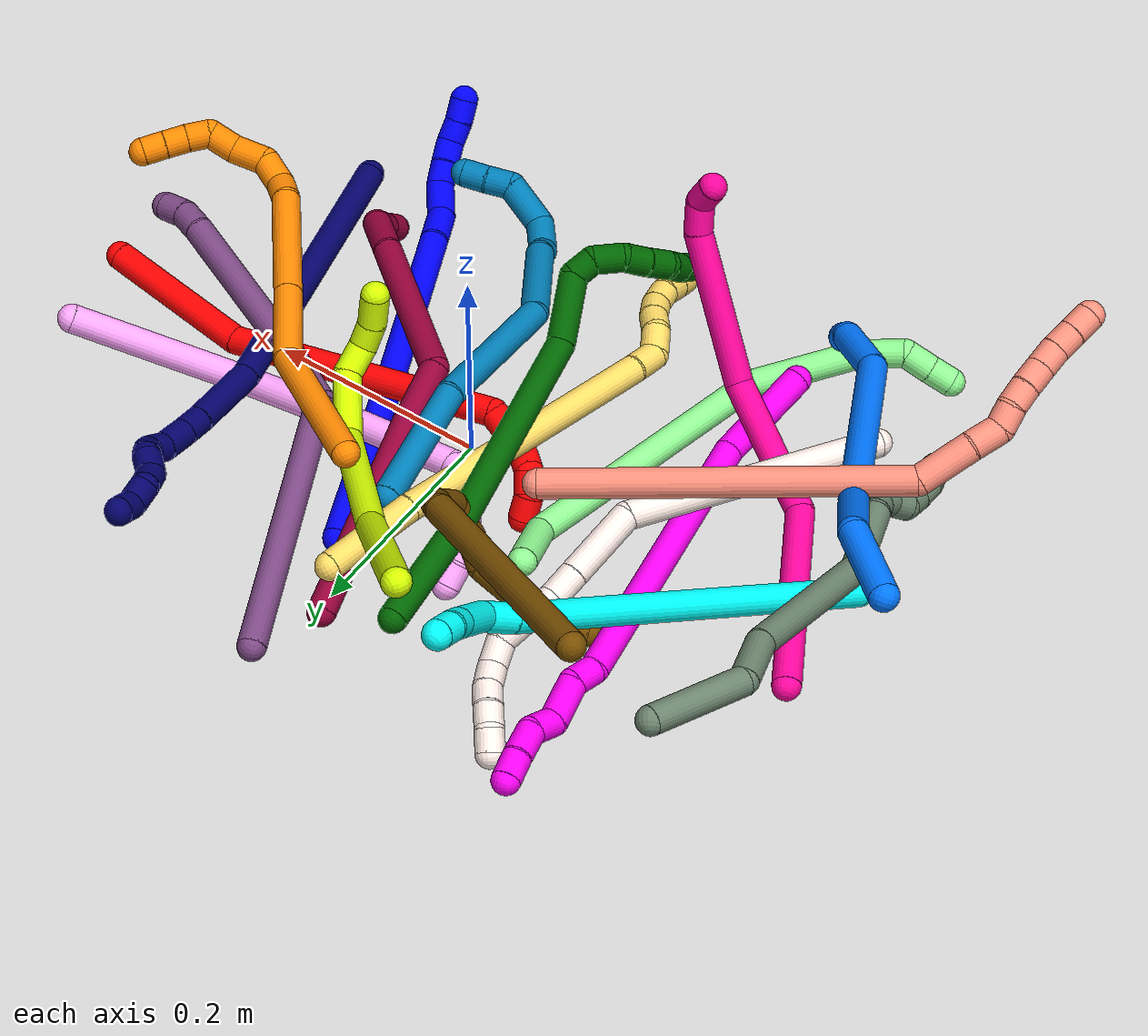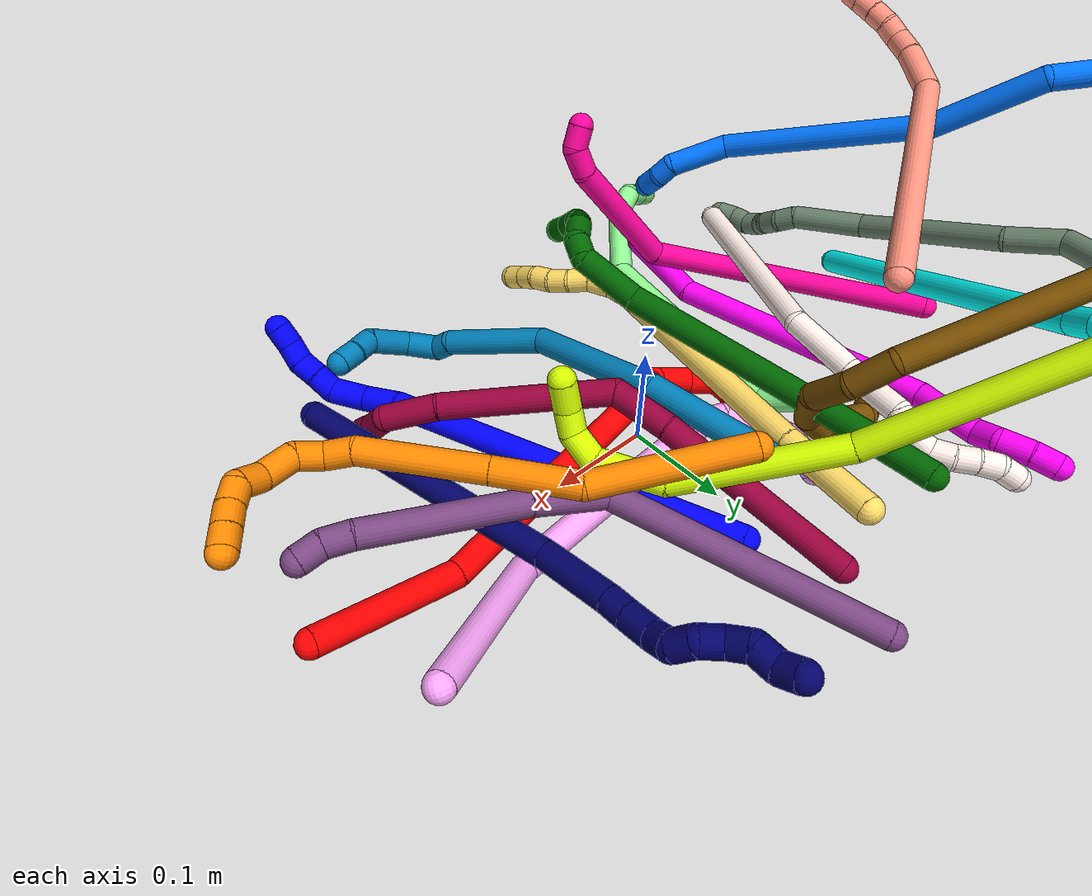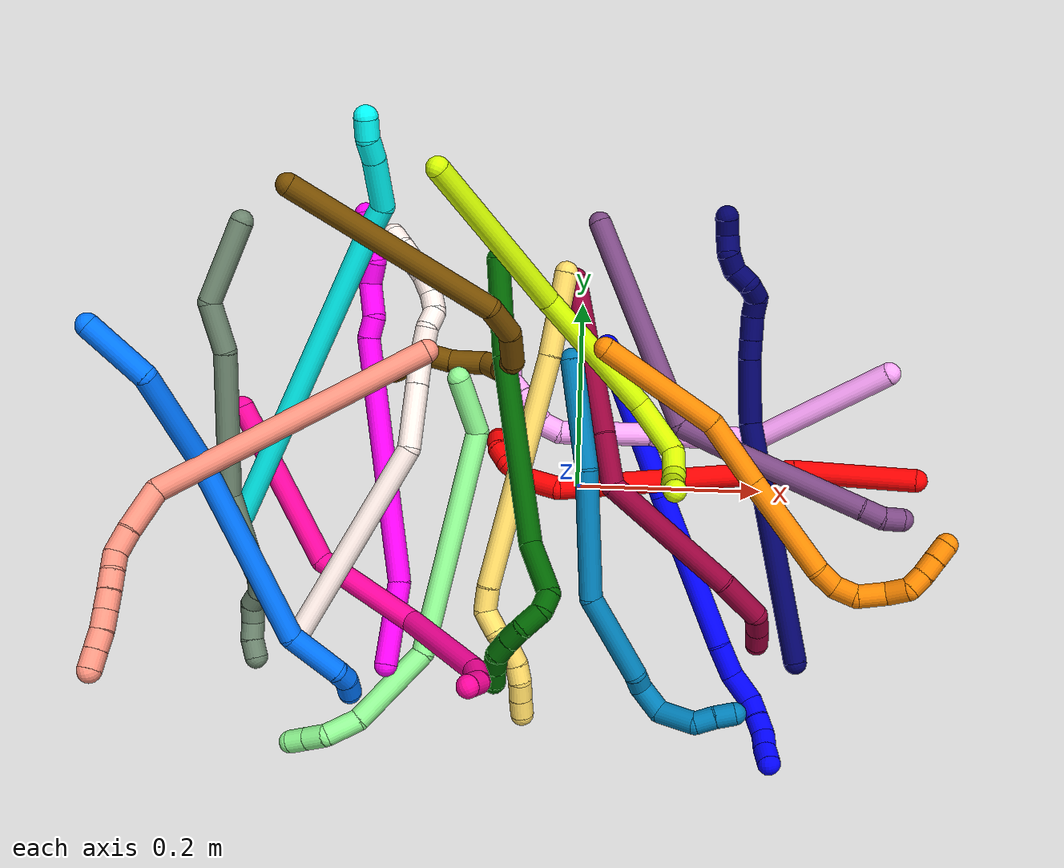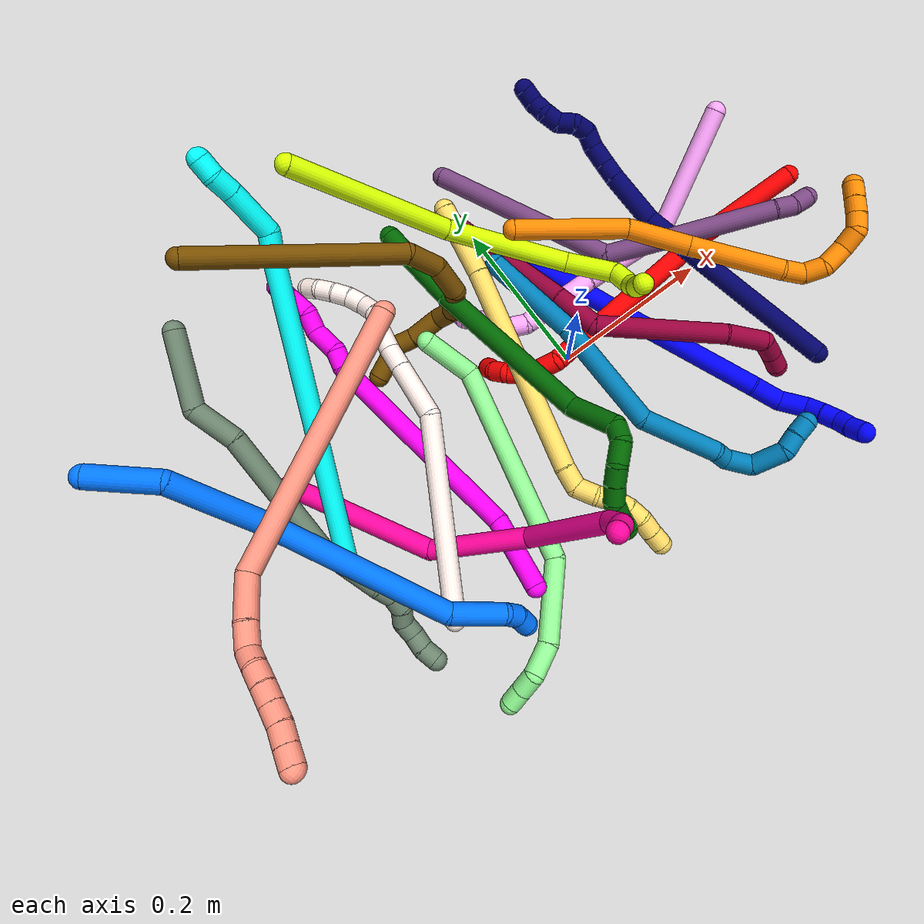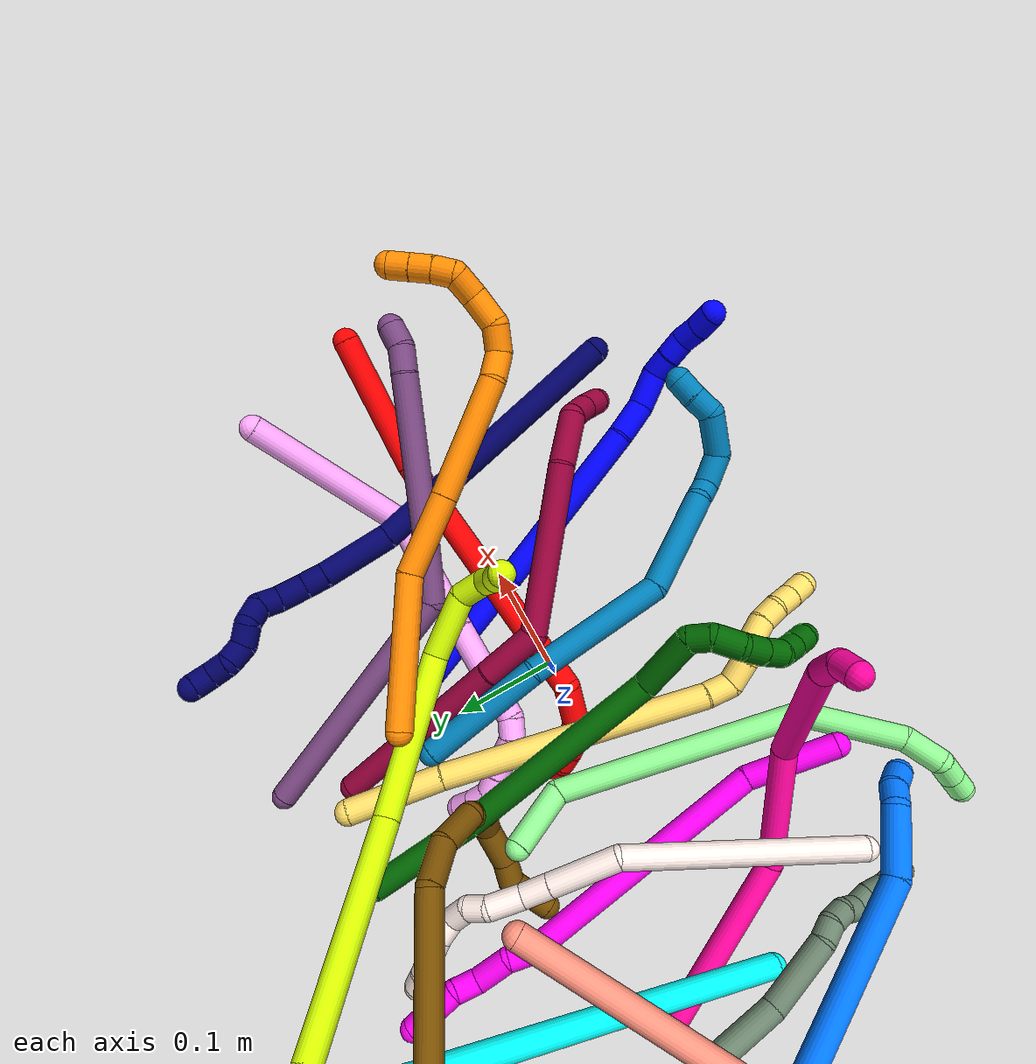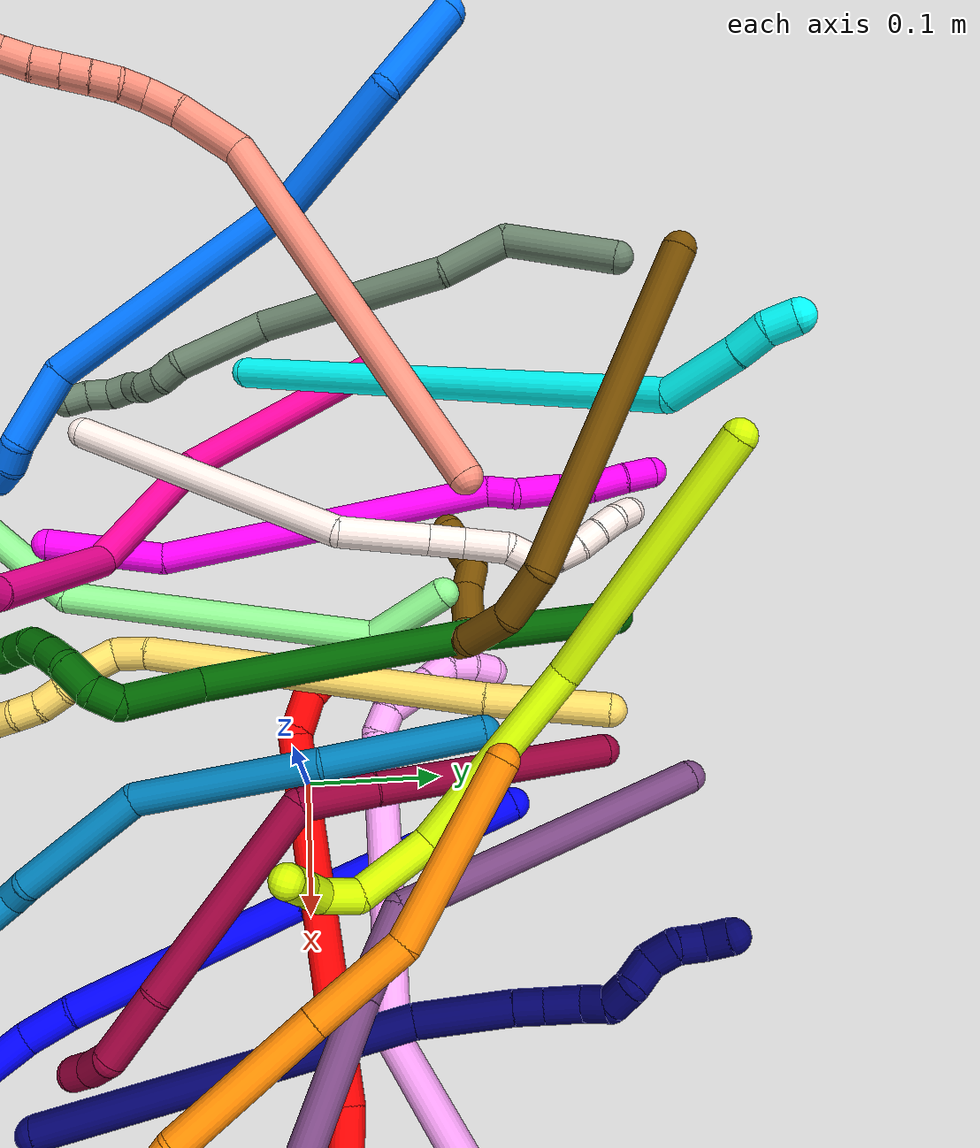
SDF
<sdf version="1.7">
 <world name="default">
  <plugin name="TubeGeneratorPlugin" filename="libtube_generator_plugin.so"/>
  <model name="photoneo_s_sensor">
   <static>1</static>
   <pose>0 0 2 1.57079 1.57079 3.14159</pose>
   <link name="link">
    <inertial><mass>0.1</mass></inertial>
    <sensor name="sensor" type="depth">
     <update_rate>30</update_rate>
     <camera>
      <horizontal_fov>1.22</horizontal_fov>
      <image><width>1920</width><height>1200</height><format>B8G8R8</format></image>
      <clip><near>0.1</near><far>4</far></clip>
      <depth_camera><output>points</output></depth_camera>
     </camera>
     <plugin name="camera_plugin" filename="libgazebo_ros_depth_camera.so">
      <baseline>0.2</baseline>
      <alwaysOn>1</alwaysOn>
      <updateRate>0.0</updateRate>
      <cameraName>camera_ir</cameraName>
      <imageTopicName>/camera/color/image_raw</imageTopicName>
      <cameraInfoTopicName>/camera/color/camera_info</cameraInfoTopicName>
      <depthImageTopicName>/camera/depth/image_raw</depthImageTopicName>
      <depthImageCameraInfoTopicName>/camera/depth/camera_info</depthImageCameraInfoTopicName>
      <pointCloudTopicName>/camera/depth/points</pointCloudTopicName>
      <frameName>fr_optical</frameName>
      <pointCloudCutoff>0.1</pointCloudCutoff>
      <pointCloudCutoffMax>2.0</pointCloudCutoffMax>
      <distortionK1>0</distortionK1>
      <distortionK2>0</distortionK2>
      <distortionK3>0</distortionK3>
      <distortionT1>0</distortionT1>
      <distortionT2>0</distortionT2>
      <CxPrime>0</CxPrime>
      <Cx>0</Cx>
      <Cy>0</Cy>
      <focalLength>0</focalLength>
      <hackBaseline>0</hackBaseline>
     </plugin>
    </sensor>
   </link>
  </model>
  <gravity>0 0 -9.8</gravity>
  <magnetic_field>6e-06 2.3e-05 -4.2e-05</magnetic_field>
  <atmosphere type="adiabatic"/>
  <physics name="default_physics" default="0" type="ode">
   <max_step_size>0.003</max_step_size>
   <real_time_factor>1</real_time_factor>
   <real_time_update_rate>1000</real_time_update_rate>
   <max_contacts>10000</max_contacts>
   <ode>
    <solver>
     <type>quick</type>
     <iters>100</iters>
     <sor>1.3</sor>
     <use_dynamic_moi_rescaling>0</use_dynamic_moi_rescaling>
    </solver>
    <constraints>
     <contact_max_correcting_vel>0</contact_max_correcting_vel>
     <contact_surface_layer>0.001</contact_surface_layer>
     <cfm>0</cfm>
     <erp>0.2</erp>
    </constraints>
   </ode>
  </physics>
  <scene><ambient>0.4 0.4 0.4 1</ambient><background>0.7 0.7 0.7 1</background><shadows>0</shadows></scene>
  <audio><device>default</device></audio>
  <spherical_coordinates>
   <surface_model>EARTH_WGS84</surface_model>
   <latitude_deg>0</latitude_deg>
   <longitude_deg>0</longitude_deg>
   <elevation>0</elevation>
   <heading_deg>0</heading_deg>
  </spherical_coordinates>
  <model name="bin">
   <static>1</static>
   <link name="bottom">
    <collision name="collision-bottom">
     <pose>0 0 -0.01 0 -0 0</pose>
     <geometry><box><size>0.8 0.6 0.02</size></box></geometry>
     <surface>
      <friction><ode><mu>100</mu><mu2>100</mu2></ode></friction>
      <contact><collide_bitmask>65535</collide_bitmask></contact>
     </surface>
    </collision>
   </link>
   <link name="west_wall">
    <collision name="collision-west_wall">
     <pose>-0.41 0 0.1 0 -0 0</pose>
     <geometry><box><size>0.02 0.6 0.2</size></box></geometry>
     <surface>
      <friction><ode><mu>100</mu><mu2>100</mu2></ode></friction>
      <contact><collide_bitmask>65535</collide_bitmask></contact>
     </surface>
    </collision>
   </link>
   <link name="east_wall">
    <collision name="collision-east_wall">
     <pose>0.41 0 0.1 0 -0 0</pose>
     <geometry><box><size>0.02 0.6 0.2</size></box></geometry>
     <surface>
      <friction><ode><mu>100</mu><mu2>100</mu2></ode></friction>
      <contact><collide_bitmask>65535</collide_bitmask></contact>
     </surface>
    </collision>
   </link>
   <link name="south_wall">
    <collision name="collision-south_wall">
     <pose>0 -0.31 0.1 0 -0 0</pose>
     <geometry><box><size>0.8 0.02 0.2</size></box></geometry>
     <surface>
      <friction><ode><mu>100</mu><mu2>100</mu2></ode></friction>
      <contact><collide_bitmask>65535</collide_bitmask></contact>
     </surface>
    </collision>
   </link>
   <link name="north_wall">
    <collision name="collision-north_wall">
     <pose>0 0.31 0.1 0 -0 0</pose>
     <geometry><box><size>0.8 0.02 0.2</size></box></geometry>
     <surface>
      <friction><ode><mu>100</mu><mu2>100</mu2></ode></friction>
      <contact><collide_bitmask>65535</collide_bitmask></contact>
     </surface>
    </collision>
   </link>
  </model>
  <model name="1">
   <static>0</static>
   <link name="1">
    <collision name="collision-cylinder-e_1_1_4">
     <pose>0.046167 -0.069559 0.026576 1.20585 0.554991 0.387284</pose>
     <geometry><cylinder><radius>0.0125</radius><length>0.175227</length></cylinder></geometry>
     <surface>
      <friction><ode><mu>1.16</mu><mu2>1.16</mu2><slip1>0</slip1><slip2>0</slip2></ode></friction>
      <contact><ode><kp>1e+06</kp><kd>1</kd><max_vel>0</max_vel><min_depth>0.001</min_depth></ode></contact>
     </surface>
    </collision>
    <visual name="visual-cylinder-e_1_1_4">
     <pose>0.046167 -0.069559 0.026576 1.20585 0.554991 0.387284</pose>
     <geometry><cylinder><radius>0.0125</radius><length>0.175227</length></cylinder></geometry>
     <material><ambient>0 0 1 1</ambient></material>
    </visual>
    <collision name="collision-cylinder-e_2_4_5">
     <pose>0.136479 -0.207616 0.081016 1.18444 0.538195 0.366912</pose>
     <geometry><cylinder><radius>0.0125</radius><length>0.172246</length></cylinder></geometry>
     <surface>
      <friction><ode><mu>1.16</mu><mu2>1.16</mu2><slip1>0</slip1><slip2>0</slip2></ode></friction>
      <contact><ode><kp>1e+06</kp><kd>1</kd><max_vel>0</max_vel><min_depth>0.001</min_depth></ode></contact>
     </surface>
    </collision>
    <visual name="visual-cylinder-e_2_4_5">
     <pose>0.136479 -0.207616 0.081016 1.18444 0.538195 0.366912</pose>
     <geometry><cylinder><radius>0.0125</radius><length>0.172246</length></cylinder></geometry>
     <material><ambient>0 0 1 1</ambient></material>
    </visual>
    <collision name="collision-cylinder-e_3_5_6">
     <pose>0.192838 -0.288464 0.114089 1.17179 0.738982 0.503129</pose>
     <geometry><cylinder><radius>0.0125</radius><length>0.036268</length></cylinder></geometry>
     <surface>
      <friction><ode><mu>1.16</mu><mu2>1.16</mu2><slip1>0</slip1><slip2>0</slip2></ode></friction>
      <contact><ode><kp>1e+06</kp><kd>1</kd><max_vel>0</max_vel><min_depth>0.001</min_depth></ode></contact>
     </surface>
    </collision>
    <visual name="visual-cylinder-e_3_5_6">
     <pose>0.192838 -0.288464 0.114089 1.17179 0.738982 0.503129</pose>
     <geometry><cylinder><radius>0.0125</radius><length>0.036268</length></cylinder></geometry>
     <material><ambient>0 0 1 1</ambient></material>
    </visual>
    <collision name="collision-cylinder-e_4_6_7">
     <pose>0.212732 -0.312734 0.129083 0.883285 0.462025 0.2215</pose>
     <geometry><cylinder><radius>0.0125</radius><length>0.034458</length></cylinder></geometry>
     <surface>
      <friction><ode><mu>1.16</mu><mu2>1.16</mu2><slip1>0</slip1><slip2>0</slip2></ode></friction>
      <contact><ode><kp>1e+06</kp><kd>1</kd><max_vel>0</max_vel><min_depth>0.001</min_depth></ode></contact>
     </surface>
    </collision>
    <visual name="visual-cylinder-e_4_6_7">
     <pose>0.212732 -0.312734 0.129083 0.883285 0.462025 0.2215</pose>
     <geometry><cylinder><radius>0.0125</radius><length>0.034458</length></cylinder></geometry>
     <material><ambient>0 0 1 1</ambient></material>
    </visual>
    <collision name="collision-cylinder-e_5_7_8">
     <pose>0.220395 -0.334263 0.143536 1.11885 -0.001604 -0.001004</pose>
     <geometry><cylinder><radius>0.0125</radius><length>0.021364</length></cylinder></geometry>
     <surface>
      <friction><ode><mu>1.16</mu><mu2>1.16</mu2><slip1>0</slip1><slip2>0</slip2></ode></friction>
      <contact><ode><kp>1e+06</kp><kd>1</kd><max_vel>0</max_vel><min_depth>0.001</min_depth></ode></contact>
     </surface>
    </collision>
    <visual name="visual-cylinder-e_5_7_8">
     <pose>0.220395 -0.334263 0.143536 1.11885 -0.001604 -0.001004</pose>
     <geometry><cylinder><radius>0.0125</radius><length>0.021364</length></cylinder></geometry>
     <material><ambient>0 0 1 1</ambient></material>
    </visual>
    <collision name="collision-cylinder-e_6_8_9">
     <pose>0.221396 -0.353124 0.152371 1.14733 0.099965 0.064624</pose>
     <geometry><cylinder><radius>0.0125</radius><length>0.020397</length></cylinder></geometry>
     <surface>
      <friction><ode><mu>1.16</mu><mu2>1.16</mu2><slip1>0</slip1><slip2>0</slip2></ode></friction>
      <contact><ode><kp>1e+06</kp><kd>1</kd><max_vel>0</max_vel><min_depth>0.001</min_depth></ode></contact>
     </surface>
    </collision>
    <visual name="visual-cylinder-e_6_8_9">
     <pose>0.221396 -0.353124 0.152371 1.14733 0.099965 0.064624</pose>
     <geometry><cylinder><radius>0.0125</radius><length>0.020397</length></cylinder></geometry>
     <material><ambient>0 0 1 1</ambient></material>
    </visual>
    <collision name="collision-cylinder-e_7_9_10">
     <pose>0.219901 -0.37169 0.159203 1.29237 -0.253772 -0.191839</pose>
     <geometry><cylinder><radius>0.0125</radius><length>0.020017</length></cylinder></geometry>
     <surface>
      <friction><ode><mu>1.16</mu><mu2>1.16</mu2><slip1>0</slip1><slip2>0</slip2></ode></friction>
      <contact><ode><kp>1e+06</kp><kd>1</kd><max_vel>0</max_vel><min_depth>0.001</min_depth></ode></contact>
     </surface>
    </collision>
    <visual name="visual-cylinder-e_7_9_10">
     <pose>0.219901 -0.37169 0.159203 1.29237 -0.253772 -0.191839</pose>
     <geometry><cylinder><radius>0.0125</radius><length>0.020017</length></cylinder></geometry>
     <material><ambient>0 0 1 1</ambient></material>
    </visual>
    <collision name="collision-cylinder-e_8_10_2">
     <pose>0.214698 -0.389813 0.165789 1.1518 -0.272066 -0.177291</pose>
     <geometry><cylinder><radius>0.0125</radius><length>0.020023</length></cylinder></geometry>
     <surface>
      <friction><ode><mu>1.16</mu><mu2>1.16</mu2><slip1>0</slip1><slip2>0</slip2></ode></friction>
      <contact><ode><kp>1e+06</kp><kd>1</kd><max_vel>0</max_vel><min_depth>0.001</min_depth></ode></contact>
     </surface>
    </collision>
    <visual name="visual-cylinder-e_8_10_2">
     <pose>0.214698 -0.389813 0.165789 1.1518 -0.272066 -0.177291</pose>
     <geometry><cylinder><radius>0.0125</radius><length>0.020023</length></cylinder></geometry>
     <material><ambient>0 0 1 1</ambient></material>
    </visual>
    <collision name="collision-sphere-2">
     <pose>0.212008 -0.398623 0.169712 0 -0 0</pose>
     <geometry><sphere><radius>0.0125</radius></sphere></geometry>
     <surface>
      <friction><ode><mu>1.16</mu><mu2>1.16</mu2><slip1>0</slip1><slip2>0</slip2></ode></friction>
      <contact><ode><kp>1e+06</kp><kd>1</kd><max_vel>0</max_vel><min_depth>0.001</min_depth></ode></contact>
     </surface>
    </collision>
    <visual name="visual-sphere-2">
     <pose>0.212008 -0.398623 0.169712 0 -0 0</pose>
     <geometry><sphere><radius>0.0125</radius></sphere></geometry>
     <material><ambient>0 0 1 1</ambient></material>
    </visual>
    <collision name="collision-sphere-10">
     <pose>0.217388 -0.381004 0.161866 0 -0 0</pose>
     <geometry><sphere><radius>0.0125</radius></sphere></geometry>
     <surface>
      <friction><ode><mu>1.16</mu><mu2>1.16</mu2><slip1>0</slip1><slip2>0</slip2></ode></friction>
      <contact><ode><kp>1e+06</kp><kd>1</kd><max_vel>0</max_vel><min_depth>0.001</min_depth></ode></contact>
     </surface>
    </collision>
    <visual name="visual-sphere-10">
     <pose>0.217388 -0.381004 0.161866 0 -0 0</pose>
     <geometry><sphere><radius>0.0125</radius></sphere></geometry>
     <material><ambient>0 0 1 1</ambient></material>
    </visual>
    <collision name="collision-sphere-9">
     <pose>0.222414 -0.362375 0.156541 0 -0 0</pose>
     <geometry><sphere><radius>0.0125</radius></sphere></geometry>
     <surface>
      <friction><ode><mu>1.16</mu><mu2>1.16</mu2><slip1>0</slip1><slip2>0</slip2></ode></friction>
      <contact><ode><kp>1e+06</kp><kd>1</kd><max_vel>0</max_vel><min_depth>0.001</min_depth></ode></contact>
     </surface>
    </collision>
    <visual name="visual-sphere-9">
     <pose>0.222414 -0.362375 0.156541 0 -0 0</pose>
     <geometry><sphere><radius>0.0125</radius></sphere></geometry>
     <material><ambient>0 0 1 1</ambient></material>
    </visual>
    <collision name="collision-sphere-4">
     <pose>0.092334 -0.139119 0.053151 0 -0 0</pose>
     <geometry><sphere><radius>0.0125</radius></sphere></geometry>
     <surface>
      <friction><ode><mu>1.16</mu><mu2>1.16</mu2><slip1>0</slip1><slip2>0</slip2></ode></friction>
      <contact><ode><kp>1e+06</kp><kd>1</kd><max_vel>0</max_vel><min_depth>0.001</min_depth></ode></contact>
     </surface>
    </collision>
    <visual name="visual-sphere-4">
     <pose>0.092334 -0.139119 0.053151 0 -0 0</pose>
     <geometry><sphere><radius>0.0125</radius></sphere></geometry>
     <material><ambient>0 0 1 1</ambient></material>
    </visual>
    <collision name="collision-sphere-1">
     <geometry><sphere><radius>0.0125</radius></sphere></geometry>
     <surface>
      <friction><ode><mu>1.16</mu><mu2>1.16</mu2><slip1>0</slip1><slip2>0</slip2></ode></friction>
      <contact><ode><kp>1e+06</kp><kd>1</kd><max_vel>0</max_vel><min_depth>0.001</min_depth></ode></contact>
     </surface>
    </collision>
    <visual name="visual-sphere-1">
     <geometry><sphere><radius>0.0125</radius></sphere></geometry>
     <material><ambient>0 0 1 1</ambient></material>
    </visual>
    <collision name="collision-sphere-8">
     <pose>0.220378 -0.343872 0.148201 0 -0 0</pose>
     <geometry><sphere><radius>0.0125</radius></sphere></geometry>
     <surface>
      <friction><ode><mu>1.16</mu><mu2>1.16</mu2><slip1>0</slip1><slip2>0</slip2></ode></friction>
      <contact><ode><kp>1e+06</kp><kd>1</kd><max_vel>0</max_vel><min_depth>0.001</min_depth></ode></contact>
     </surface>
    </collision>
    <visual name="visual-sphere-8">
     <pose>0.220378 -0.343872 0.148201 0 -0 0</pose>
     <geometry><sphere><radius>0.0125</radius></sphere></geometry>
     <material><ambient>0 0 1 1</ambient></material>
    </visual>
    <collision name="collision-sphere-5">
     <pose>0.180625 -0.276114 0.108881 0 -0 0</pose>
     <geometry><sphere><radius>0.0125</radius></sphere></geometry>
     <surface>
      <friction><ode><mu>1.16</mu><mu2>1.16</mu2><slip1>0</slip1><slip2>0</slip2></ode></friction>
      <contact><ode><kp>1e+06</kp><kd>1</kd><max_vel>0</max_vel><min_depth>0.001</min_depth></ode></contact>
     </surface>
    </collision>
    <visual name="visual-sphere-5">
     <pose>0.180625 -0.276114 0.108881 0 -0 0</pose>
     <geometry><sphere><radius>0.0125</radius></sphere></geometry>
     <material><ambient>0 0 1 1</ambient></material>
    </visual>
    <collision name="collision-sphere-6">
     <pose>0.205052 -0.300815 0.119296 0 -0 0</pose>
     <geometry><sphere><radius>0.0125</radius></sphere></geometry>
     <surface>
      <friction><ode><mu>1.16</mu><mu2>1.16</mu2><slip1>0</slip1><slip2>0</slip2></ode></friction>
      <contact><ode><kp>1e+06</kp><kd>1</kd><max_vel>0</max_vel><min_depth>0.001</min_depth></ode></contact>
     </surface>
    </collision>
    <visual name="visual-sphere-6">
     <pose>0.205052 -0.300815 0.119296 0 -0 0</pose>
     <geometry><sphere><radius>0.0125</radius></sphere></geometry>
     <material><ambient>0 0 1 1</ambient></material>
    </visual>
    <collision name="collision-sphere-7">
     <pose>0.220412 -0.324654 0.138871 0 -0 0</pose>
     <geometry><sphere><radius>0.0125</radius></sphere></geometry>
     <surface>
      <friction><ode><mu>1.16</mu><mu2>1.16</mu2><slip1>0</slip1><slip2>0</slip2></ode></friction>
      <contact><ode><kp>1e+06</kp><kd>1</kd><max_vel>0</max_vel><min_depth>0.001</min_depth></ode></contact>
     </surface>
    </collision>
    <visual name="visual-sphere-7">
     <pose>0.220412 -0.324654 0.138871 0 -0 0</pose>
     <geometry><sphere><radius>0.0125</radius></sphere></geometry>
     <material><ambient>0 0 1 1</ambient></material>
    </visual>
    <inertial>
     <pose>0.127694 -0.197554 0.079756 0 -0 0</pose>
     <mass>0.5</mass>
     <inertia>
      <ixx>0.001017</ixx>
      <ixy>0</ixy>
      <ixz>0</ixz>
      <iyy>0.000721</iyy>
      <iyz>0</iyz>
      <izz>0.000264</izz>
     </inertia>
    </inertial>
   </link>
   <pose>0.027678 0.154079 0.011464 -0.835893 0.973177 -0.877182</pose>
  </model>
  <model name="2">
   <static>0</static>
   <link name="2">
    <collision name="collision-cylinder-e_1_1_4">
     <pose>-0.062065 0.022764 0.002633 -1.45565 -1.2171 1.11118</pose>
     <geometry><cylinder><radius>0.0125</radius><length>0.132322</length></cylinder></geometry>
     <surface>
      <friction><ode><mu>1.16</mu><mu2>1.16</mu2><slip1>0</slip1><slip2>0</slip2></ode></friction>
      <contact><ode><kp>1e+06</kp><kd>1</kd><max_vel>0</max_vel><min_depth>0.001</min_depth></ode></contact>
     </surface>
    </collision>
    <visual name="visual-cylinder-e_1_1_4">
     <pose>-0.062065 0.022764 0.002633 -1.45565 -1.2171 1.11118</pose>
     <geometry><cylinder><radius>0.0125</radius><length>0.132322</length></cylinder></geometry>
     <material><ambient>1 0 0 1</ambient></material>
    </visual>
    <collision name="collision-cylinder-e_2_4_5">
     <pose>-0.234763 0.101294 -0.035635 -2.20363 -1.01212 1.6603</pose>
     <geometry><cylinder><radius>0.0125</radius><length>0.260937</length></cylinder></geometry>
     <surface>
      <friction><ode><mu>1.16</mu><mu2>1.16</mu2><slip1>0</slip1><slip2>0</slip2></ode></friction>
      <contact><ode><kp>1e+06</kp><kd>1</kd><max_vel>0</max_vel><min_depth>0.001</min_depth></ode></contact>
     </surface>
    </collision>
    <visual name="visual-cylinder-e_2_4_5">
     <pose>-0.234763 0.101294 -0.035635 -2.20363 -1.01212 1.6603</pose>
     <geometry><cylinder><radius>0.0125</radius><length>0.260937</length></cylinder></geometry>
     <material><ambient>1 0 0 1</ambient></material>
    </visual>
    <collision name="collision-cylinder-e_3_5_6">
     <pose>-0.363726 0.160421 -0.071336 -0.573985 -1.24499 0.417462</pose>
     <geometry><cylinder><radius>0.0125</radius><length>0.038699</length></cylinder></geometry>
     <surface>
      <friction><ode><mu>1.16</mu><mu2>1.16</mu2><slip1>0</slip1><slip2>0</slip2></ode></friction>
      <contact><ode><kp>1e+06</kp><kd>1</kd><max_vel>0</max_vel><min_depth>0.001</min_depth></ode></contact>
     </surface>
    </collision>
    <visual name="visual-cylinder-e_3_5_6">
     <pose>-0.363726 0.160421 -0.071336 -0.573985 -1.24499 0.417462</pose>
     <geometry><cylinder><radius>0.0125</radius><length>0.038699</length></cylinder></geometry>
     <material><ambient>1 0 0 1</ambient></material>
    </visual>
    <collision name="collision-cylinder-e_4_6_7">
     <pose>-0.395035 0.159419 -0.06669 1.69742 -1.24391 -1.36633</pose>
     <geometry><cylinder><radius>0.0125</radius><length>0.027405</length></cylinder></geometry>
     <surface>
      <friction><ode><mu>1.16</mu><mu2>1.16</mu2><slip1>0</slip1><slip2>0</slip2></ode></friction>
      <contact><ode><kp>1e+06</kp><kd>1</kd><max_vel>0</max_vel><min_depth>0.001</min_depth></ode></contact>
     </surface>
    </collision>
    <visual name="visual-cylinder-e_4_6_7">
     <pose>-0.395035 0.159419 -0.06669 1.69742 -1.24391 -1.36633</pose>
     <geometry><cylinder><radius>0.0125</radius><length>0.027405</length></cylinder></geometry>
     <material><ambient>1 0 0 1</ambient></material>
    </visual>
    <collision name="collision-cylinder-e_5_7_8">
     <pose>-0.415275 0.151611 -0.061243 0.520812 -0.80951 -0.227321</pose>
     <geometry><cylinder><radius>0.0125</radius><length>0.020065</length></cylinder></geometry>
     <surface>
      <friction><ode><mu>1.16</mu><mu2>1.16</mu2><slip1>0</slip1><slip2>0</slip2></ode></friction>
      <contact><ode><kp>1e+06</kp><kd>1</kd><max_vel>0</max_vel><min_depth>0.001</min_depth></ode></contact>
     </surface>
    </collision>
    <visual name="visual-cylinder-e_5_7_8">
     <pose>-0.415275 0.151611 -0.061243 0.520812 -0.80951 -0.227321</pose>
     <geometry><cylinder><radius>0.0125</radius><length>0.020065</length></cylinder></geometry>
     <material><ambient>1 0 0 1</ambient></material>
    </visual>
    <collision name="collision-cylinder-e_6_8_2">
     <pose>-0.426085 0.144567 -0.046281 0.38209 -0.352121 -0.068787</pose>
     <geometry><cylinder><radius>0.0125</radius><length>0.020572</length></cylinder></geometry>
     <surface>
      <friction><ode><mu>1.16</mu><mu2>1.16</mu2><slip1>0</slip1><slip2>0</slip2></ode></friction>
      <contact><ode><kp>1e+06</kp><kd>1</kd><max_vel>0</max_vel><min_depth>0.001</min_depth></ode></contact>
     </surface>
    </collision>
    <visual name="visual-cylinder-e_6_8_2">
     <pose>-0.426085 0.144567 -0.046281 0.38209 -0.352121 -0.068787</pose>
     <geometry><cylinder><radius>0.0125</radius><length>0.020572</length></cylinder></geometry>
     <material><ambient>1 0 0 1</ambient></material>
    </visual>
    <collision name="collision-sphere-2">
     <pose>-0.429633 0.140967 -0.037322 0 -0 0</pose>
     <geometry><sphere><radius>0.0125</radius></sphere></geometry>
     <surface>
      <friction><ode><mu>1.16</mu><mu2>1.16</mu2><slip1>0</slip1><slip2>0</slip2></ode></friction>
      <contact><ode><kp>1e+06</kp><kd>1</kd><max_vel>0</max_vel><min_depth>0.001</min_depth></ode></contact>
     </surface>
    </collision>
    <visual name="visual-sphere-2">
     <pose>-0.429633 0.140967 -0.037322 0 -0 0</pose>
     <geometry><sphere><radius>0.0125</radius></sphere></geometry>
     <material><ambient>1 0 0 1</ambient></material>
    </visual>
    <collision name="collision-sphere-4">
     <pose>-0.124131 0.045529 0.005266 0 -0 0</pose>
     <geometry><sphere><radius>0.0125</radius></sphere></geometry>
     <surface>
      <friction><ode><mu>1.16</mu><mu2>1.16</mu2><slip1>0</slip1><slip2>0</slip2></ode></friction>
      <contact><ode><kp>1e+06</kp><kd>1</kd><max_vel>0</max_vel><min_depth>0.001</min_depth></ode></contact>
     </surface>
    </collision>
    <visual name="visual-sphere-4">
     <pose>-0.124131 0.045529 0.005266 0 -0 0</pose>
     <geometry><sphere><radius>0.0125</radius></sphere></geometry>
     <material><ambient>1 0 0 1</ambient></material>
    </visual>
    <collision name="collision-sphere-1">
     <geometry><sphere><radius>0.0125</radius></sphere></geometry>
     <surface>
      <friction><ode><mu>1.16</mu><mu2>1.16</mu2><slip1>0</slip1><slip2>0</slip2></ode></friction>
      <contact><ode><kp>1e+06</kp><kd>1</kd><max_vel>0</max_vel><min_depth>0.001</min_depth></ode></contact>
     </surface>
    </collision>
    <visual name="visual-sphere-1">
     <geometry><sphere><radius>0.0125</radius></sphere></geometry>
     <material><ambient>1 0 0 1</ambient></material>
    </visual>
    <collision name="collision-sphere-8">
     <pose>-0.422538 0.148167 -0.055239 0 -0 0</pose>
     <geometry><sphere><radius>0.0125</radius></sphere></geometry>
     <surface>
      <friction><ode><mu>1.16</mu><mu2>1.16</mu2><slip1>0</slip1><slip2>0</slip2></ode></friction>
      <contact><ode><kp>1e+06</kp><kd>1</kd><max_vel>0</max_vel><min_depth>0.001</min_depth></ode></contact>
     </surface>
    </collision>
    <visual name="visual-sphere-8">
     <pose>-0.422538 0.148167 -0.055239 0 -0 0</pose>
     <geometry><sphere><radius>0.0125</radius></sphere></geometry>
     <material><ambient>1 0 0 1</ambient></material>
    </visual>
    <collision name="collision-sphere-5">
     <pose>-0.345394 0.157058 -0.076536 0 -0 0</pose>
     <geometry><sphere><radius>0.0125</radius></sphere></geometry>
     <surface>
      <friction><ode><mu>1.16</mu><mu2>1.16</mu2><slip1>0</slip1><slip2>0</slip2></ode></friction>
      <contact><ode><kp>1e+06</kp><kd>1</kd><max_vel>0</max_vel><min_depth>0.001</min_depth></ode></contact>
     </surface>
    </collision>
    <visual name="visual-sphere-5">
     <pose>-0.345394 0.157058 -0.076536 0 -0 0</pose>
     <geometry><sphere><radius>0.0125</radius></sphere></geometry>
     <material><ambient>1 0 0 1</ambient></material>
    </visual>
    <collision name="collision-sphere-6">
     <pose>-0.382058 0.163784 -0.066135 0 -0 0</pose>
     <geometry><sphere><radius>0.0125</radius></sphere></geometry>
     <surface>
      <friction><ode><mu>1.16</mu><mu2>1.16</mu2><slip1>0</slip1><slip2>0</slip2></ode></friction>
      <contact><ode><kp>1e+06</kp><kd>1</kd><max_vel>0</max_vel><min_depth>0.001</min_depth></ode></contact>
     </surface>
    </collision>
    <visual name="visual-sphere-6">
     <pose>-0.382058 0.163784 -0.066135 0 -0 0</pose>
     <geometry><sphere><radius>0.0125</radius></sphere></geometry>
     <material><ambient>1 0 0 1</ambient></material>
    </visual>
    <collision name="collision-sphere-7">
     <pose>-0.408012 0.155055 -0.067246 0 -0 0</pose>
     <geometry><sphere><radius>0.0125</radius></sphere></geometry>
     <surface>
      <friction><ode><mu>1.16</mu><mu2>1.16</mu2><slip1>0</slip1><slip2>0</slip2></ode></friction>
      <contact><ode><kp>1e+06</kp><kd>1</kd><max_vel>0</max_vel><min_depth>0.001</min_depth></ode></contact>
     </surface>
    </collision>
    <visual name="visual-sphere-7">
     <pose>-0.408012 0.155055 -0.067246 0 -0 0</pose>
     <geometry><sphere><radius>0.0125</radius></sphere></geometry>
     <material><ambient>1 0 0 1</ambient></material>
    </visual>
    <inertial>
     <pose>-0.222941 0.092073 -0.031439 0 -0 0</pose>
     <mass>0.5</mass>
     <inertia>
      <ixx>0.000779</ixx>
      <ixy>0</ixy>
      <ixz>0</ixz>
      <iyy>0.00214</iyy>
      <iyz>0</iyz>
      <izz>0.000753</izz>
     </inertia>
    </inertial>
   </link>
   <pose>0.364561 0.017403 0.036084 -2.98313 -0.089608 -0.393235</pose>
  </model>
  <model name="3">
   <static>0</static>
   <link name="3">
    <collision name="collision-cylinder-e_1_1_4">
     <pose>0.02684 0.108191 0.145891 -0.638098 0.146713 -0.048542</pose>
     <geometry><cylinder><radius>0.0125</radius><length>0.367204</length></cylinder></geometry>
     <surface>
      <friction><ode><mu>1.16</mu><mu2>1.16</mu2><slip1>0</slip1><slip2>0</slip2></ode></friction>
      <contact><ode><kp>1e+06</kp><kd>1</kd><max_vel>0</max_vel><min_depth>0.001</min_depth></ode></contact>
     </surface>
    </collision>
    <visual name="visual-cylinder-e_1_1_4">
     <pose>0.02684 0.108191 0.145891 -0.638098 0.146713 -0.048542</pose>
     <geometry><cylinder><radius>0.0125</radius><length>0.367204</length></cylinder></geometry>
     <material><ambient>0.003922 1 0.996078 1</ambient></material>
    </visual>
    <collision name="collision-cylinder-e_2_4_5">
     <pose>0.056899 0.22608 0.302616 -0.730053 0.217832 -0.083527</pose>
     <geometry><cylinder><radius>0.0125</radius><length>0.029787</length></cylinder></geometry>
     <surface>
      <friction><ode><mu>1.16</mu><mu2>1.16</mu2><slip1>0</slip1><slip2>0</slip2></ode></friction>
      <contact><ode><kp>1e+06</kp><kd>1</kd><max_vel>0</max_vel><min_depth>0.001</min_depth></ode></contact>
     </surface>
    </collision>
    <visual name="visual-cylinder-e_2_4_5">
     <pose>0.056899 0.22608 0.302616 -0.730053 0.217832 -0.083527</pose>
     <geometry><cylinder><radius>0.0125</radius><length>0.029787</length></cylinder></geometry>
     <material><ambient>0.003922 1 0.996078 1</ambient></material>
    </visual>
    <collision name="collision-cylinder-e_3_5_6">
     <pose>0.075059 0.24046 0.33735 -0.19348 0.550301 -0.054779</pose>
     <geometry><cylinder><radius>0.0125</radius><length>0.057141</length></cylinder></geometry>
     <surface>
      <friction><ode><mu>1.16</mu><mu2>1.16</mu2><slip1>0</slip1><slip2>0</slip2></ode></friction>
      <contact><ode><kp>1e+06</kp><kd>1</kd><max_vel>0</max_vel><min_depth>0.001</min_depth></ode></contact>
     </surface>
    </collision>
    <visual name="visual-cylinder-e_3_5_6">
     <pose>0.075059 0.24046 0.33735 -0.19348 0.550301 -0.054779</pose>
     <geometry><cylinder><radius>0.0125</radius><length>0.057141</length></cylinder></geometry>
     <material><ambient>0.003922 1 0.996078 1</ambient></material>
    </visual>
    <collision name="collision-cylinder-e_4_6_7">
     <pose>0.096971 0.246052 0.371356 -0.089711 0.601884 -0.02786</pose>
     <geometry><cylinder><radius>0.0125</radius><length>0.024625</length></cylinder></geometry>
     <surface>
      <friction><ode><mu>1.16</mu><mu2>1.16</mu2><slip1>0</slip1><slip2>0</slip2></ode></friction>
      <contact><ode><kp>1e+06</kp><kd>1</kd><max_vel>0</max_vel><min_depth>0.001</min_depth></ode></contact>
     </surface>
    </collision>
    <visual name="visual-cylinder-e_4_6_7">
     <pose>0.096971 0.246052 0.371356 -0.089711 0.601884 -0.02786</pose>
     <geometry><cylinder><radius>0.0125</radius><length>0.024625</length></cylinder></geometry>
     <material><ambient>0.003922 1 0.996078 1</ambient></material>
    </visual>
    <collision name="collision-cylinder-e_5_7_2">
     <pose>0.107027 0.248815 0.391457 -0.183431 0.294706 -0.027301</pose>
     <geometry><cylinder><radius>0.0125</radius><length>0.021243</length></cylinder></geometry>
     <surface>
      <friction><ode><mu>1.16</mu><mu2>1.16</mu2><slip1>0</slip1><slip2>0</slip2></ode></friction>
      <contact><ode><kp>1e+06</kp><kd>1</kd><max_vel>0</max_vel><min_depth>0.001</min_depth></ode></contact>
     </surface>
    </collision>
    <visual name="visual-cylinder-e_5_7_2">
     <pose>0.107027 0.248815 0.391457 -0.183431 0.294706 -0.027301</pose>
     <geometry><cylinder><radius>0.0125</radius><length>0.021243</length></cylinder></geometry>
     <material><ambient>0.003922 1 0.996078 1</ambient></material>
    </visual>
    <collision name="collision-sphere-2">
     <pose>0.110112 0.250669 0.40145 0 -0 0</pose>
     <geometry><sphere><radius>0.0125</radius></sphere></geometry>
     <surface>
      <friction><ode><mu>1.16</mu><mu2>1.16</mu2><slip1>0</slip1><slip2>0</slip2></ode></friction>
      <contact><ode><kp>1e+06</kp><kd>1</kd><max_vel>0</max_vel><min_depth>0.001</min_depth></ode></contact>
     </surface>
    </collision>
    <visual name="visual-sphere-2">
     <pose>0.110112 0.250669 0.40145 0 -0 0</pose>
     <geometry><sphere><radius>0.0125</radius></sphere></geometry>
     <material><ambient>0.003922 1 0.996078 1</ambient></material>
    </visual>
    <collision name="collision-sphere-7">
     <pose>0.103942 0.246961 0.381464 0 -0 0</pose>
     <geometry><sphere><radius>0.0125</radius></sphere></geometry>
     <surface>
      <friction><ode><mu>1.16</mu><mu2>1.16</mu2><slip1>0</slip1><slip2>0</slip2></ode></friction>
      <contact><ode><kp>1e+06</kp><kd>1</kd><max_vel>0</max_vel><min_depth>0.001</min_depth></ode></contact>
     </surface>
    </collision>
    <visual name="visual-sphere-7">
     <pose>0.103942 0.246961 0.381464 0 -0 0</pose>
     <geometry><sphere><radius>0.0125</radius></sphere></geometry>
     <material><ambient>0.003922 1 0.996078 1</ambient></material>
    </visual>
    <collision name="collision-sphere-6">
     <pose>0.089999 0.245143 0.361248 0 -0 0</pose>
     <geometry><sphere><radius>0.0125</radius></sphere></geometry>
     <surface>
      <friction><ode><mu>1.16</mu><mu2>1.16</mu2><slip1>0</slip1><slip2>0</slip2></ode></friction>
      <contact><ode><kp>1e+06</kp><kd>1</kd><max_vel>0</max_vel><min_depth>0.001</min_depth></ode></contact>
     </surface>
    </collision>
    <visual name="visual-sphere-6">
     <pose>0.089999 0.245143 0.361248 0 -0 0</pose>
     <geometry><sphere><radius>0.0125</radius></sphere></geometry>
     <material><ambient>0.003922 1 0.996078 1</ambient></material>
    </visual>
    <collision name="collision-sphere-5">
     <pose>0.060118 0.235778 0.313452 0 -0 0</pose>
     <geometry><sphere><radius>0.0125</radius></sphere></geometry>
     <surface>
      <friction><ode><mu>1.16</mu><mu2>1.16</mu2><slip1>0</slip1><slip2>0</slip2></ode></friction>
      <contact><ode><kp>1e+06</kp><kd>1</kd><max_vel>0</max_vel><min_depth>0.001</min_depth></ode></contact>
     </surface>
    </collision>
    <visual name="visual-sphere-5">
     <pose>0.060118 0.235778 0.313452 0 -0 0</pose>
     <geometry><sphere><radius>0.0125</radius></sphere></geometry>
     <material><ambient>0.003922 1 0.996078 1</ambient></material>
    </visual>
    <collision name="collision-sphere-1">
     <geometry><sphere><radius>0.0125</radius></sphere></geometry>
     <surface>
      <friction><ode><mu>1.16</mu><mu2>1.16</mu2><slip1>0</slip1><slip2>0</slip2></ode></friction>
      <contact><ode><kp>1e+06</kp><kd>1</kd><max_vel>0</max_vel><min_depth>0.001</min_depth></ode></contact>
     </surface>
    </collision>
    <visual name="visual-sphere-1">
     <geometry><sphere><radius>0.0125</radius></sphere></geometry>
     <material><ambient>0.003922 1 0.996078 1</ambient></material>
    </visual>
    <collision name="collision-sphere-4">
     <pose>0.053681 0.216382 0.291781 0 -0 0</pose>
     <geometry><sphere><radius>0.0125</radius></sphere></geometry>
     <surface>
      <friction><ode><mu>1.16</mu><mu2>1.16</mu2><slip1>0</slip1><slip2>0</slip2></ode></friction>
      <contact><ode><kp>1e+06</kp><kd>1</kd><max_vel>0</max_vel><min_depth>0.001</min_depth></ode></contact>
     </surface>
    </collision>
    <visual name="visual-sphere-4">
     <pose>0.053681 0.216382 0.291781 0 -0 0</pose>
     <geometry><sphere><radius>0.0125</radius></sphere></geometry>
     <material><ambient>0.003922 1 0.996078 1</ambient></material>
    </visual>
    <inertial>
     <pose>0.041002 0.143094 0.198645 0 -0 0</pose>
     <mass>0.5</mass>
     <inertia>
      <ixx>0.003922</ixx>
      <ixy>0</ixy>
      <ixz>0</ixz>
      <iyy>0.003183</iyy>
      <iyz>0</iyz>
      <izz>-0.003031</izz>
     </inertia>
    </inertial>
   </link>
   <pose>-0.363133 -0.044152 0.012192 1.09544 -1.21172 -2.5264</pose>
  </model>
  <model name="4">
   <static>0</static>
   <link name="4">
    <collision name="collision-cylinder-e_1_1_4">
     <pose>0.003471 0.081088 -0.011722 -1.71436 0.042338 -0.048895</pose>
     <geometry><cylinder><radius>0.0125</radius><length>0.164009</length></cylinder></geometry>
     <surface>
      <friction><ode><mu>1.16</mu><mu2>1.16</mu2><slip1>0</slip1><slip2>0</slip2></ode></friction>
      <contact><ode><kp>1e+06</kp><kd>1</kd><max_vel>0</max_vel><min_depth>0.001</min_depth></ode></contact>
     </surface>
    </collision>
    <visual name="visual-cylinder-e_1_1_4">
     <pose>0.003471 0.081088 -0.011722 -1.71436 0.042338 -0.048895</pose>
     <geometry><cylinder><radius>0.0125</radius><length>0.164009</length></cylinder></geometry>
     <material><ambient>1 0.65098 0.996078 1</ambient></material>
    </visual>
    <collision name="collision-cylinder-e_2_4_5">
     <pose>-0.030051 0.205682 -0.040093 -1.93631 -0.671147 0.938318</pose>
     <geometry><cylinder><radius>0.0125</radius><length>0.118969</length></cylinder></geometry>
     <surface>
      <friction><ode><mu>1.16</mu><mu2>1.16</mu2><slip1>0</slip1><slip2>0</slip2></ode></friction>
      <contact><ode><kp>1e+06</kp><kd>1</kd><max_vel>0</max_vel><min_depth>0.001</min_depth></ode></contact>
     </surface>
    </collision>
    <visual name="visual-cylinder-e_2_4_5">
     <pose>-0.030051 0.205682 -0.040093 -1.93631 -0.671147 0.938318</pose>
     <geometry><cylinder><radius>0.0125</radius><length>0.118969</length></cylinder></geometry>
     <material><ambient>1 0.65098 0.996078 1</ambient></material>
    </visual>
    <collision name="collision-cylinder-e_3_5_6">
     <pose>-0.095379 0.286688 -0.068367 -1.87138 -0.625174 0.826551</pose>
     <geometry><cylinder><radius>0.0125</radius><length>0.096835</length></cylinder></geometry>
     <surface>
      <friction><ode><mu>1.16</mu><mu2>1.16</mu2><slip1>0</slip1><slip2>0</slip2></ode></friction>
      <contact><ode><kp>1e+06</kp><kd>1</kd><max_vel>0</max_vel><min_depth>0.001</min_depth></ode></contact>
     </surface>
    </collision>
    <visual name="visual-cylinder-e_3_5_6">
     <pose>-0.095379 0.286688 -0.068367 -1.87138 -0.625174 0.826551</pose>
     <geometry><cylinder><radius>0.0125</radius><length>0.096835</length></cylinder></geometry>
     <material><ambient>1 0.65098 0.996078 1</ambient></material>
    </visual>
    <collision name="collision-cylinder-e_4_6_7">
     <pose>-0.13172 0.33013 -0.07903 -1.41043 -0.926036 0.803662</pose>
     <geometry><cylinder><radius>0.0125</radius><length>0.020032</length></cylinder></geometry>
     <surface>
      <friction><ode><mu>1.16</mu><mu2>1.16</mu2><slip1>0</slip1><slip2>0</slip2></ode></friction>
      <contact><ode><kp>1e+06</kp><kd>1</kd><max_vel>0</max_vel><min_depth>0.001</min_depth></ode></contact>
     </surface>
    </collision>
    <visual name="visual-cylinder-e_4_6_7">
     <pose>-0.13172 0.33013 -0.07903 -1.41043 -0.926036 0.803662</pose>
     <geometry><cylinder><radius>0.0125</radius><length>0.020032</length></cylinder></geometry>
     <material><ambient>1 0.65098 0.996078 1</ambient></material>
    </visual>
    <collision name="collision-cylinder-e_5_7_8">
     <pose>-0.146834 0.339707 -0.07204 -0.542504 -0.79025 0.230941</pose>
     <geometry><cylinder><radius>0.0125</radius><length>0.020009</length></cylinder></geometry>
     <surface>
      <friction><ode><mu>1.16</mu><mu2>1.16</mu2><slip1>0</slip1><slip2>0</slip2></ode></friction>
      <contact><ode><kp>1e+06</kp><kd>1</kd><max_vel>0</max_vel><min_depth>0.001</min_depth></ode></contact>
     </surface>
    </collision>
    <visual name="visual-cylinder-e_5_7_8">
     <pose>-0.146834 0.339707 -0.07204 -0.542504 -0.79025 0.230941</pose>
     <geometry><cylinder><radius>0.0125</radius><length>0.020009</length></cylinder></geometry>
     <material><ambient>1 0.65098 0.996078 1</ambient></material>
    </visual>
    <collision name="collision-cylinder-e_6_8_9">
     <pose>-0.16154 0.346652 -0.060375 -0.531091 -0.860341 0.24829</pose>
     <geometry><cylinder><radius>0.0125</radius><length>0.020045</length></cylinder></geometry>
     <surface>
      <friction><ode><mu>1.16</mu><mu2>1.16</mu2><slip1>0</slip1><slip2>0</slip2></ode></friction>
      <contact><ode><kp>1e+06</kp><kd>1</kd><max_vel>0</max_vel><min_depth>0.001</min_depth></ode></contact>
     </surface>
    </collision>
    <visual name="visual-cylinder-e_6_8_9">
     <pose>-0.16154 0.346652 -0.060375 -0.531091 -0.860341 0.24829</pose>
     <geometry><cylinder><radius>0.0125</radius><length>0.020045</length></cylinder></geometry>
     <material><ambient>1 0.65098 0.996078 1</ambient></material>
    </visual>
    <collision name="collision-cylinder-e_7_9_10">
     <pose>-0.176445 0.353918 -0.04909 -0.61076 -0.814364 0.27026</pose>
     <geometry><cylinder><radius>0.0125</radius><length>0.020095</length></cylinder></geometry>
     <surface>
      <friction><ode><mu>1.16</mu><mu2>1.16</mu2><slip1>0</slip1><slip2>0</slip2></ode></friction>
      <contact><ode><kp>1e+06</kp><kd>1</kd><max_vel>0</max_vel><min_depth>0.001</min_depth></ode></contact>
     </surface>
    </collision>
    <visual name="visual-cylinder-e_7_9_10">
     <pose>-0.176445 0.353918 -0.04909 -0.61076 -0.814364 0.27026</pose>
     <geometry><cylinder><radius>0.0125</radius><length>0.020095</length></cylinder></geometry>
     <material><ambient>1 0.65098 0.996078 1</ambient></material>
    </visual>
    <collision name="collision-cylinder-e_8_10_11">
     <pose>-0.188052 0.357802 -0.034411 0.007837 -0.44434 -0.00177</pose>
     <geometry><cylinder><radius>0.0125</radius><length>0.020002</length></cylinder></geometry>
     <surface>
      <friction><ode><mu>1.16</mu><mu2>1.16</mu2><slip1>0</slip1><slip2>0</slip2></ode></friction>
      <contact><ode><kp>1e+06</kp><kd>1</kd><max_vel>0</max_vel><min_depth>0.001</min_depth></ode></contact>
     </surface>
    </collision>
    <visual name="visual-cylinder-e_8_10_11">
     <pose>-0.188052 0.357802 -0.034411 0.007837 -0.44434 -0.00177</pose>
     <geometry><cylinder><radius>0.0125</radius><length>0.020002</length></cylinder></geometry>
     <material><ambient>1 0.65098 0.996078 1</ambient></material>
    </visual>
    <collision name="collision-cylinder-e_9_11_2">
     <pose>-0.194703 0.357914 -0.015662 -0.018808 -0.237395 0.002243</pose>
     <geometry><cylinder><radius>0.0125</radius><length>0.020003</length></cylinder></geometry>
     <surface>
      <friction><ode><mu>1.16</mu><mu2>1.16</mu2><slip1>0</slip1><slip2>0</slip2></ode></friction>
      <contact><ode><kp>1e+06</kp><kd>1</kd><max_vel>0</max_vel><min_depth>0.001</min_depth></ode></contact>
     </surface>
    </collision>
    <visual name="visual-cylinder-e_9_11_2">
     <pose>-0.194703 0.357914 -0.015662 -0.018808 -0.237395 0.002243</pose>
     <geometry><cylinder><radius>0.0125</radius><length>0.020003</length></cylinder></geometry>
     <material><ambient>1 0.65098 0.996078 1</ambient></material>
    </visual>
    <collision name="collision-sphere-2">
     <pose>-0.197055 0.358096 -0.005943 0 -0 0</pose>
     <geometry><sphere><radius>0.0125</radius></sphere></geometry>
     <surface>
      <friction><ode><mu>1.16</mu><mu2>1.16</mu2><slip1>0</slip1><slip2>0</slip2></ode></friction>
      <contact><ode><kp>1e+06</kp><kd>1</kd><max_vel>0</max_vel><min_depth>0.001</min_depth></ode></contact>
     </surface>
    </collision>
    <visual name="visual-sphere-2">
     <pose>-0.197055 0.358096 -0.005943 0 -0 0</pose>
     <geometry><sphere><radius>0.0125</radius></sphere></geometry>
     <material><ambient>1 0.65098 0.996078 1</ambient></material>
    </visual>
    <collision name="collision-sphere-11">
     <pose>-0.192351 0.357731 -0.025381 0 -0 0</pose>
     <geometry><sphere><radius>0.0125</radius></sphere></geometry>
     <surface>
      <friction><ode><mu>1.16</mu><mu2>1.16</mu2><slip1>0</slip1><slip2>0</slip2></ode></friction>
      <contact><ode><kp>1e+06</kp><kd>1</kd><max_vel>0</max_vel><min_depth>0.001</min_depth></ode></contact>
     </surface>
    </collision>
    <visual name="visual-sphere-11">
     <pose>-0.192351 0.357731 -0.025381 0 -0 0</pose>
     <geometry><sphere><radius>0.0125</radius></sphere></geometry>
     <material><ambient>1 0.65098 0.996078 1</ambient></material>
    </visual>
    <collision name="collision-sphere-10">
     <pose>-0.183753 0.357872 -0.04344 0 -0 0</pose>
     <geometry><sphere><radius>0.0125</radius></sphere></geometry>
     <surface>
      <friction><ode><mu>1.16</mu><mu2>1.16</mu2><slip1>0</slip1><slip2>0</slip2></ode></friction>
      <contact><ode><kp>1e+06</kp><kd>1</kd><max_vel>0</max_vel><min_depth>0.001</min_depth></ode></contact>
     </surface>
    </collision>
    <visual name="visual-sphere-10">
     <pose>-0.183753 0.357872 -0.04344 0 -0 0</pose>
     <geometry><sphere><radius>0.0125</radius></sphere></geometry>
     <material><ambient>1 0.65098 0.996078 1</ambient></material>
    </visual>
    <collision name="collision-sphere-9">
     <pose>-0.169138 0.349963 -0.054739 0 -0 0</pose>
     <geometry><sphere><radius>0.0125</radius></sphere></geometry>
     <surface>
      <friction><ode><mu>1.16</mu><mu2>1.16</mu2><slip1>0</slip1><slip2>0</slip2></ode></friction>
      <contact><ode><kp>1e+06</kp><kd>1</kd><max_vel>0</max_vel><min_depth>0.001</min_depth></ode></contact>
     </surface>
    </collision>
    <visual name="visual-sphere-9">
     <pose>-0.169138 0.349963 -0.054739 0 -0 0</pose>
     <geometry><sphere><radius>0.0125</radius></sphere></geometry>
     <material><ambient>1 0.65098 0.996078 1</ambient></material>
    </visual>
    <collision name="collision-sphere-4">
     <pose>0.006942 0.162177 -0.023443 0 -0 0</pose>
     <geometry><sphere><radius>0.0125</radius></sphere></geometry>
     <surface>
      <friction><ode><mu>1.16</mu><mu2>1.16</mu2><slip1>0</slip1><slip2>0</slip2></ode></friction>
      <contact><ode><kp>1e+06</kp><kd>1</kd><max_vel>0</max_vel><min_depth>0.001</min_depth></ode></contact>
     </surface>
    </collision>
    <visual name="visual-sphere-4">
     <pose>0.006942 0.162177 -0.023443 0 -0 0</pose>
     <geometry><sphere><radius>0.0125</radius></sphere></geometry>
     <material><ambient>1 0.65098 0.996078 1</ambient></material>
    </visual>
    <collision name="collision-sphere-1">
     <geometry><sphere><radius>0.0125</radius></sphere></geometry>
     <surface>
      <friction><ode><mu>1.16</mu><mu2>1.16</mu2><slip1>0</slip1><slip2>0</slip2></ode></friction>
      <contact><ode><kp>1e+06</kp><kd>1</kd><max_vel>0</max_vel><min_depth>0.001</min_depth></ode></contact>
     </surface>
    </collision>
    <visual name="visual-sphere-1">
     <geometry><sphere><radius>0.0125</radius></sphere></geometry>
     <material><ambient>1 0.65098 0.996078 1</ambient></material>
    </visual>
    <collision name="collision-sphere-8">
     <pose>-0.153943 0.343342 -0.066011 0 -0 0</pose>
     <geometry><sphere><radius>0.0125</radius></sphere></geometry>
     <surface>
      <friction><ode><mu>1.16</mu><mu2>1.16</mu2><slip1>0</slip1><slip2>0</slip2></ode></friction>
      <contact><ode><kp>1e+06</kp><kd>1</kd><max_vel>0</max_vel><min_depth>0.001</min_depth></ode></contact>
     </surface>
    </collision>
    <visual name="visual-sphere-8">
     <pose>-0.153943 0.343342 -0.066011 0 -0 0</pose>
     <geometry><sphere><radius>0.0125</radius></sphere></geometry>
     <material><ambient>1 0.65098 0.996078 1</ambient></material>
    </visual>
    <collision name="collision-sphere-5">
     <pose>-0.067043 0.249188 -0.056744 0 -0 0</pose>
     <geometry><sphere><radius>0.0125</radius></sphere></geometry>
     <surface>
      <friction><ode><mu>1.16</mu><mu2>1.16</mu2><slip1>0</slip1><slip2>0</slip2></ode></friction>
      <contact><ode><kp>1e+06</kp><kd>1</kd><max_vel>0</max_vel><min_depth>0.001</min_depth></ode></contact>
     </surface>
    </collision>
    <visual name="visual-sphere-5">
     <pose>-0.067043 0.249188 -0.056744 0 -0 0</pose>
     <geometry><sphere><radius>0.0125</radius></sphere></geometry>
     <material><ambient>1 0.65098 0.996078 1</ambient></material>
    </visual>
    <collision name="collision-sphere-6">
     <pose>-0.123715 0.324188 -0.079991 0 -0 0</pose>
     <geometry><sphere><radius>0.0125</radius></sphere></geometry>
     <surface>
      <friction><ode><mu>1.16</mu><mu2>1.16</mu2><slip1>0</slip1><slip2>0</slip2></ode></friction>
      <contact><ode><kp>1e+06</kp><kd>1</kd><max_vel>0</max_vel><min_depth>0.001</min_depth></ode></contact>
     </surface>
    </collision>
    <visual name="visual-sphere-6">
     <pose>-0.123715 0.324188 -0.079991 0 -0 0</pose>
     <geometry><sphere><radius>0.0125</radius></sphere></geometry>
     <material><ambient>1 0.65098 0.996078 1</ambient></material>
    </visual>
    <collision name="collision-sphere-7">
     <pose>-0.139726 0.336073 -0.078069 0 -0 0</pose>
     <geometry><sphere><radius>0.0125</radius></sphere></geometry>
     <surface>
      <friction><ode><mu>1.16</mu><mu2>1.16</mu2><slip1>0</slip1><slip2>0</slip2></ode></friction>
      <contact><ode><kp>1e+06</kp><kd>1</kd><max_vel>0</max_vel><min_depth>0.001</min_depth></ode></contact>
     </surface>
    </collision>
    <visual name="visual-sphere-7">
     <pose>-0.139726 0.336073 -0.078069 0 -0 0</pose>
     <geometry><sphere><radius>0.0125</radius></sphere></geometry>
     <material><ambient>1 0.65098 0.996078 1</ambient></material>
    </visual>
    <inertial>
     <pose>-0.064517 0.214635 -0.039071 0 -0 0</pose>
     <mass>0.5</mass>
     <inertia>
      <ixx>0.000597</ixx>
      <ixy>0</ixy>
      <ixz>0</ixz>
      <iyy>0.000159</iyy>
      <iyz>0</iyz>
      <izz>-0.000414</izz>
     </inertia>
    </inertial>
   </link>
   <pose>0.325366 0.129037 0.077388 -2.57503 0.522352 -0.897103</pose>
  </model>
  <model name="5">
   <static>0</static>
   <link name="5">
    <collision name="collision-cylinder-e_1_1_4">
     <pose>-0.018767 -0.039751 0.010308 1.31706 -0.428666 -0.333725</pose>
     <geometry><cylinder><radius>0.0125</radius><length>0.090302</length></cylinder></geometry>
     <surface>
      <friction><ode><mu>1.16</mu><mu2>1.16</mu2><slip1>0</slip1><slip2>0</slip2></ode></friction>
      <contact><ode><kp>1e+06</kp><kd>1</kd><max_vel>0</max_vel><min_depth>0.001</min_depth></ode></contact>
     </surface>
    </collision>
    <visual name="visual-cylinder-e_1_1_4">
     <pose>-0.018767 -0.039751 0.010308 1.31706 -0.428666 -0.333725</pose>
     <geometry><cylinder><radius>0.0125</radius><length>0.090302</length></cylinder></geometry>
     <material><ambient>1 0.858824 0.4 1</ambient></material>
    </visual>
    <collision name="collision-cylinder-e_2_4_5">
     <pose>-0.084832 -0.191981 0.056956 1.25831 -0.380624 -0.278603</pose>
     <geometry><cylinder><radius>0.0125</radius><length>0.25463</length></cylinder></geometry>
     <surface>
      <friction><ode><mu>1.16</mu><mu2>1.16</mu2><slip1>0</slip1><slip2>0</slip2></ode></friction>
      <contact><ode><kp>1e+06</kp><kd>1</kd><max_vel>0</max_vel><min_depth>0.001</min_depth></ode></contact>
     </surface>
    </collision>
    <visual name="visual-cylinder-e_2_4_5">
     <pose>-0.084832 -0.191981 0.056956 1.25831 -0.380624 -0.278603</pose>
     <geometry><cylinder><radius>0.0125</radius><length>0.25463</length></cylinder></geometry>
     <material><ambient>1 0.858824 0.4 1</ambient></material>
    </visual>
    <collision name="collision-cylinder-e_3_5_6">
     <pose>-0.138821 -0.315056 0.097425 1.19908 -0.531822 -0.368085</pose>
     <geometry><cylinder><radius>0.0125</radius><length>0.02639</length></cylinder></geometry>
     <surface>
      <friction><ode><mu>1.16</mu><mu2>1.16</mu2><slip1>0</slip1><slip2>0</slip2></ode></friction>
      <contact><ode><kp>1e+06</kp><kd>1</kd><max_vel>0</max_vel><min_depth>0.001</min_depth></ode></contact>
     </surface>
    </collision>
    <visual name="visual-cylinder-e_3_5_6">
     <pose>-0.138821 -0.315056 0.097425 1.19908 -0.531822 -0.368085</pose>
     <geometry><cylinder><radius>0.0125</radius><length>0.02639</length></cylinder></geometry>
     <material><ambient>1 0.858824 0.4 1</ambient></material>
    </visual>
    <collision name="collision-cylinder-e_4_6_7">
     <pose>-0.155671 -0.33287 0.098403 1.98261 -0.91123 -1.28538</pose>
     <geometry><cylinder><radius>0.0125</radius><length>0.025709</length></cylinder></geometry>
     <surface>
      <friction><ode><mu>1.16</mu><mu2>1.16</mu2><slip1>0</slip1><slip2>0</slip2></ode></friction>
      <contact><ode><kp>1e+06</kp><kd>1</kd><max_vel>0</max_vel><min_depth>0.001</min_depth></ode></contact>
     </surface>
    </collision>
    <visual name="visual-cylinder-e_4_6_7">
     <pose>-0.155671 -0.33287 0.098403 1.98261 -0.91123 -1.28538</pose>
     <geometry><cylinder><radius>0.0125</radius><length>0.025709</length></cylinder></geometry>
     <material><ambient>1 0.858824 0.4 1</ambient></material>
    </visual>
    <collision name="collision-cylinder-e_5_7_8">
     <pose>-0.176044 -0.343331 0.094551 1.78307 -1.25685 -1.46564</pose>
     <geometry><cylinder><radius>0.0125</radius><length>0.021481</length></cylinder></geometry>
     <surface>
      <friction><ode><mu>1.16</mu><mu2>1.16</mu2><slip1>0</slip1><slip2>0</slip2></ode></friction>
      <contact><ode><kp>1e+06</kp><kd>1</kd><max_vel>0</max_vel><min_depth>0.001</min_depth></ode></contact>
     </surface>
    </collision>
    <visual name="visual-cylinder-e_5_7_8">
     <pose>-0.176044 -0.343331 0.094551 1.78307 -1.25685 -1.46564</pose>
     <geometry><cylinder><radius>0.0125</radius><length>0.021481</length></cylinder></geometry>
     <material><ambient>1 0.858824 0.4 1</ambient></material>
    </visual>
    <collision name="collision-cylinder-e_6_8_9">
     <pose>-0.195462 -0.351118 0.094733 1.37947 -1.10466 -0.940682</pose>
     <geometry><cylinder><radius>0.0125</radius><length>0.020602</length></cylinder></geometry>
     <surface>
      <friction><ode><mu>1.16</mu><mu2>1.16</mu2><slip1>0</slip1><slip2>0</slip2></ode></friction>
      <contact><ode><kp>1e+06</kp><kd>1</kd><max_vel>0</max_vel><min_depth>0.001</min_depth></ode></contact>
     </surface>
    </collision>
    <visual name="visual-cylinder-e_6_8_9">
     <pose>-0.195462 -0.351118 0.094733 1.37947 -1.10466 -0.940682</pose>
     <geometry><cylinder><radius>0.0125</radius><length>0.020602</length></cylinder></geometry>
     <material><ambient>1 0.858824 0.4 1</ambient></material>
    </visual>
    <collision name="collision-cylinder-e_7_9_10">
     <pose>-0.21222 -0.36212 0.097298 1.31562 -0.847409 -0.670608</pose>
     <geometry><cylinder><radius>0.0125</radius><length>0.020162</length></cylinder></geometry>
     <surface>
      <friction><ode><mu>1.16</mu><mu2>1.16</mu2><slip1>0</slip1><slip2>0</slip2></ode></friction>
      <contact><ode><kp>1e+06</kp><kd>1</kd><max_vel>0</max_vel><min_depth>0.001</min_depth></ode></contact>
     </surface>
    </collision>
    <visual name="visual-cylinder-e_7_9_10">
     <pose>-0.21222 -0.36212 0.097298 1.31562 -0.847409 -0.670608</pose>
     <geometry><cylinder><radius>0.0125</radius><length>0.020162</length></cylinder></geometry>
     <material><ambient>1 0.858824 0.4 1</ambient></material>
    </visual>
    <collision name="collision-cylinder-e_8_10_11">
     <pose>-0.226746 -0.37436 0.103525 0.904944 -0.758513 -0.382736</pose>
     <geometry><cylinder><radius>0.0125</radius><length>0.020263</length></cylinder></geometry>
     <surface>
      <friction><ode><mu>1.16</mu><mu2>1.16</mu2><slip1>0</slip1><slip2>0</slip2></ode></friction>
      <contact><ode><kp>1e+06</kp><kd>1</kd><max_vel>0</max_vel><min_depth>0.001</min_depth></ode></contact>
     </surface>
    </collision>
    <visual name="visual-cylinder-e_8_10_11">
     <pose>-0.226746 -0.37436 0.103525 0.904944 -0.758513 -0.382736</pose>
     <geometry><cylinder><radius>0.0125</radius><length>0.020263</length></cylinder></geometry>
     <material><ambient>1 0.858824 0.4 1</ambient></material>
    </visual>
    <collision name="collision-cylinder-e_9_11_2">
     <pose>-0.241132 -0.385746 0.112341 0.919193 -0.811073 -0.418766</pose>
     <geometry><cylinder><radius>0.0125</radius><length>0.020461</length></cylinder></geometry>
     <surface>
      <friction><ode><mu>1.16</mu><mu2>1.16</mu2><slip1>0</slip1><slip2>0</slip2></ode></friction>
      <contact><ode><kp>1e+06</kp><kd>1</kd><max_vel>0</max_vel><min_depth>0.001</min_depth></ode></contact>
     </surface>
    </collision>
    <visual name="visual-cylinder-e_9_11_2">
     <pose>-0.241132 -0.385746 0.112341 0.919193 -0.811073 -0.418766</pose>
     <geometry><cylinder><radius>0.0125</radius><length>0.020461</length></cylinder></geometry>
     <material><ambient>1 0.858824 0.4 1</ambient></material>
    </visual>
    <collision name="collision-sphere-2">
     <pose>-0.248549 -0.391348 0.116614 0 -0 0</pose>
     <geometry><sphere><radius>0.0125</radius></sphere></geometry>
     <surface>
      <friction><ode><mu>1.16</mu><mu2>1.16</mu2><slip1>0</slip1><slip2>0</slip2></ode></friction>
      <contact><ode><kp>1e+06</kp><kd>1</kd><max_vel>0</max_vel><min_depth>0.001</min_depth></ode></contact>
     </surface>
    </collision>
    <visual name="visual-sphere-2">
     <pose>-0.248549 -0.391348 0.116614 0 -0 0</pose>
     <geometry><sphere><radius>0.0125</radius></sphere></geometry>
     <material><ambient>1 0.858824 0.4 1</ambient></material>
    </visual>
    <collision name="collision-sphere-11">
     <pose>-0.233715 -0.380144 0.108068 0 -0 0</pose>
     <geometry><sphere><radius>0.0125</radius></sphere></geometry>
     <surface>
      <friction><ode><mu>1.16</mu><mu2>1.16</mu2><slip1>0</slip1><slip2>0</slip2></ode></friction>
      <contact><ode><kp>1e+06</kp><kd>1</kd><max_vel>0</max_vel><min_depth>0.001</min_depth></ode></contact>
     </surface>
    </collision>
    <visual name="visual-sphere-11">
     <pose>-0.233715 -0.380144 0.108068 0 -0 0</pose>
     <geometry><sphere><radius>0.0125</radius></sphere></geometry>
     <material><ambient>1 0.858824 0.4 1</ambient></material>
    </visual>
    <collision name="collision-sphere-10">
     <pose>-0.219777 -0.368577 0.098982 0 -0 0</pose>
     <geometry><sphere><radius>0.0125</radius></sphere></geometry>
     <surface>
      <friction><ode><mu>1.16</mu><mu2>1.16</mu2><slip1>0</slip1><slip2>0</slip2></ode></friction>
      <contact><ode><kp>1e+06</kp><kd>1</kd><max_vel>0</max_vel><min_depth>0.001</min_depth></ode></contact>
     </surface>
    </collision>
    <visual name="visual-sphere-10">
     <pose>-0.219777 -0.368577 0.098982 0 -0 0</pose>
     <geometry><sphere><radius>0.0125</radius></sphere></geometry>
     <material><ambient>1 0.858824 0.4 1</ambient></material>
    </visual>
    <collision name="collision-sphere-9">
     <pose>-0.204664 -0.355664 0.095613 0 -0 0</pose>
     <geometry><sphere><radius>0.0125</radius></sphere></geometry>
     <surface>
      <friction><ode><mu>1.16</mu><mu2>1.16</mu2><slip1>0</slip1><slip2>0</slip2></ode></friction>
      <contact><ode><kp>1e+06</kp><kd>1</kd><max_vel>0</max_vel><min_depth>0.001</min_depth></ode></contact>
     </surface>
    </collision>
    <visual name="visual-sphere-9">
     <pose>-0.204664 -0.355664 0.095613 0 -0 0</pose>
     <geometry><sphere><radius>0.0125</radius></sphere></geometry>
     <material><ambient>1 0.858824 0.4 1</ambient></material>
    </visual>
    <collision name="collision-sphere-4">
     <pose>-0.037535 -0.079502 0.020616 0 -0 0</pose>
     <geometry><sphere><radius>0.0125</radius></sphere></geometry>
     <surface>
      <friction><ode><mu>1.16</mu><mu2>1.16</mu2><slip1>0</slip1><slip2>0</slip2></ode></friction>
      <contact><ode><kp>1e+06</kp><kd>1</kd><max_vel>0</max_vel><min_depth>0.001</min_depth></ode></contact>
     </surface>
    </collision>
    <visual name="visual-sphere-4">
     <pose>-0.037535 -0.079502 0.020616 0 -0 0</pose>
     <geometry><sphere><radius>0.0125</radius></sphere></geometry>
     <material><ambient>1 0.858824 0.4 1</ambient></material>
    </visual>
    <collision name="collision-sphere-1">
     <geometry><sphere><radius>0.0125</radius></sphere></geometry>
     <surface>
      <friction><ode><mu>1.16</mu><mu2>1.16</mu2><slip1>0</slip1><slip2>0</slip2></ode></friction>
      <contact><ode><kp>1e+06</kp><kd>1</kd><max_vel>0</max_vel><min_depth>0.001</min_depth></ode></contact>
     </surface>
    </collision>
    <visual name="visual-sphere-1">
     <geometry><sphere><radius>0.0125</radius></sphere></geometry>
     <material><ambient>1 0.858824 0.4 1</ambient></material>
    </visual>
    <collision name="collision-sphere-8">
     <pose>-0.18626 -0.346573 0.093853 0 -0 0</pose>
     <geometry><sphere><radius>0.0125</radius></sphere></geometry>
     <surface>
      <friction><ode><mu>1.16</mu><mu2>1.16</mu2><slip1>0</slip1><slip2>0</slip2></ode></friction>
      <contact><ode><kp>1e+06</kp><kd>1</kd><max_vel>0</max_vel><min_depth>0.001</min_depth></ode></contact>
     </surface>
    </collision>
    <visual name="visual-sphere-8">
     <pose>-0.18626 -0.346573 0.093853 0 -0 0</pose>
     <geometry><sphere><radius>0.0125</radius></sphere></geometry>
     <material><ambient>1 0.858824 0.4 1</ambient></material>
    </visual>
    <collision name="collision-sphere-5">
     <pose>-0.13213 -0.30446 0.093295 0 -0 0</pose>
     <geometry><sphere><radius>0.0125</radius></sphere></geometry>
     <surface>
      <friction><ode><mu>1.16</mu><mu2>1.16</mu2><slip1>0</slip1><slip2>0</slip2></ode></friction>
      <contact><ode><kp>1e+06</kp><kd>1</kd><max_vel>0</max_vel><min_depth>0.001</min_depth></ode></contact>
     </surface>
    </collision>
    <visual name="visual-sphere-5">
     <pose>-0.13213 -0.30446 0.093295 0 -0 0</pose>
     <geometry><sphere><radius>0.0125</radius></sphere></geometry>
     <material><ambient>1 0.858824 0.4 1</ambient></material>
    </visual>
    <collision name="collision-sphere-6">
     <pose>-0.145513 -0.325652 0.101556 0 -0 0</pose>
     <geometry><sphere><radius>0.0125</radius></sphere></geometry>
     <surface>
      <friction><ode><mu>1.16</mu><mu2>1.16</mu2><slip1>0</slip1><slip2>0</slip2></ode></friction>
      <contact><ode><kp>1e+06</kp><kd>1</kd><max_vel>0</max_vel><min_depth>0.001</min_depth></ode></contact>
     </surface>
    </collision>
    <visual name="visual-sphere-6">
     <pose>-0.145513 -0.325652 0.101556 0 -0 0</pose>
     <geometry><sphere><radius>0.0125</radius></sphere></geometry>
     <material><ambient>1 0.858824 0.4 1</ambient></material>
    </visual>
    <collision name="collision-sphere-7">
     <pose>-0.165829 -0.340089 0.09525 0 -0 0</pose>
     <geometry><sphere><radius>0.0125</radius></sphere></geometry>
     <surface>
      <friction><ode><mu>1.16</mu><mu2>1.16</mu2><slip1>0</slip1><slip2>0</slip2></ode></friction>
      <contact><ode><kp>1e+06</kp><kd>1</kd><max_vel>0</max_vel><min_depth>0.001</min_depth></ode></contact>
     </surface>
    </collision>
    <visual name="visual-sphere-7">
     <pose>-0.165829 -0.340089 0.09525 0 -0 0</pose>
     <geometry><sphere><radius>0.0125</radius></sphere></geometry>
     <material><ambient>1 0.858824 0.4 1</ambient></material>
    </visual>
    <inertial>
     <pose>-0.105154 -0.213468 0.06175 0 -0 0</pose>
     <mass>0.5</mass>
     <inertia>
      <ixx>0.000901</ixx>
      <ixy>0</ixy>
      <ixz>0</ixz>
      <iyy>0.000169</iyy>
      <iyz>0</iyz>
      <izz>0.001849</izz>
     </inertia>
    </inertial>
   </link>
   <pose>-0.020472 0.22538 0.077438 -2.73564 -0.3995 2.52712</pose>
  </model>
  <model name="6">
   <static>0</static>
   <link name="6">
    <collision name="collision-cylinder-e_1_1_4">
     <pose>0.012757 -0.003194 0.050807 0.062777 0.245536 0.007748</pose>
     <geometry><cylinder><radius>0.0125</radius><length>0.104963</length></cylinder></geometry>
     <surface>
      <friction><ode><mu>1.16</mu><mu2>1.16</mu2><slip1>0</slip1><slip2>0</slip2></ode></friction>
      <contact><ode><kp>1e+06</kp><kd>1</kd><max_vel>0</max_vel><min_depth>0.001</min_depth></ode></contact>
     </surface>
    </collision>
    <visual name="visual-cylinder-e_1_1_4">
     <pose>0.012757 -0.003194 0.050807 0.062777 0.245536 0.007748</pose>
     <geometry><cylinder><radius>0.0125</radius><length>0.104963</length></cylinder></geometry>
     <material><ambient>0 0.392157 0.003922 1</ambient></material>
    </visual>
    <collision name="collision-cylinder-e_2_4_5">
     <pose>0.044854 -0.004717 0.200811 -0.016834 0.192524 -0.001626</pose>
     <geometry><cylinder><radius>0.0125</radius><length>0.202157</length></cylinder></geometry>
     <surface>
      <friction><ode><mu>1.16</mu><mu2>1.16</mu2><slip1>0</slip1><slip2>0</slip2></ode></friction>
      <contact><ode><kp>1e+06</kp><kd>1</kd><max_vel>0</max_vel><min_depth>0.001</min_depth></ode></contact>
     </surface>
    </collision>
    <visual name="visual-cylinder-e_2_4_5">
     <pose>0.044854 -0.004717 0.200811 -0.016834 0.192524 -0.001626</pose>
     <geometry><cylinder><radius>0.0125</radius><length>0.202157</length></cylinder></geometry>
     <material><ambient>0 0.392157 0.003922 1</ambient></material>
    </visual>
    <collision name="collision-cylinder-e_3_5_6">
     <pose>0.057712 0.002513 0.329209 -0.188154 -0.214719 0.020337</pose>
     <geometry><cylinder><radius>0.0125</radius><length>0.060848</length></cylinder></geometry>
     <surface>
      <friction><ode><mu>1.16</mu><mu2>1.16</mu2><slip1>0</slip1><slip2>0</slip2></ode></friction>
      <contact><ode><kp>1e+06</kp><kd>1</kd><max_vel>0</max_vel><min_depth>0.001</min_depth></ode></contact>
     </surface>
    </collision>
    <visual name="visual-cylinder-e_3_5_6">
     <pose>0.057712 0.002513 0.329209 -0.188154 -0.214719 0.020337</pose>
     <geometry><cylinder><radius>0.0125</radius><length>0.060848</length></cylinder></geometry>
     <material><ambient>0 0.392157 0.003922 1</ambient></material>
    </visual>
    <collision name="collision-cylinder-e_4_6_7">
     <pose>0.050324 0.002866 0.367304 0.529611 -0.087571 -0.023761</pose>
     <geometry><cylinder><radius>0.0125</radius><length>0.020692</length></cylinder></geometry>
     <surface>
      <friction><ode><mu>1.16</mu><mu2>1.16</mu2><slip1>0</slip1><slip2>0</slip2></ode></friction>
      <contact><ode><kp>1e+06</kp><kd>1</kd><max_vel>0</max_vel><min_depth>0.001</min_depth></ode></contact>
     </surface>
    </collision>
    <visual name="visual-cylinder-e_4_6_7">
     <pose>0.050324 0.002866 0.367304 0.529611 -0.087571 -0.023761</pose>
     <geometry><cylinder><radius>0.0125</radius><length>0.020692</length></cylinder></geometry>
     <material><ambient>0 0.392157 0.003922 1</ambient></material>
    </visual>
    <collision name="collision-cylinder-e_5_7_8">
     <pose>0.052536 -0.013262 0.382983 1.01489 0.237796 0.132648</pose>
     <geometry><cylinder><radius>0.0125</radius><length>0.026459</length></cylinder></geometry>
     <surface>
      <friction><ode><mu>1.16</mu><mu2>1.16</mu2><slip1>0</slip1><slip2>0</slip2></ode></friction>
      <contact><ode><kp>1e+06</kp><kd>1</kd><max_vel>0</max_vel><min_depth>0.001</min_depth></ode></contact>
     </surface>
    </collision>
    <visual name="visual-cylinder-e_5_7_8">
     <pose>0.052536 -0.013262 0.382983 1.01489 0.237796 0.132648</pose>
     <geometry><cylinder><radius>0.0125</radius><length>0.026459</length></cylinder></geometry>
     <material><ambient>0 0.392157 0.003922 1</ambient></material>
    </visual>
    <collision name="collision-cylinder-e_6_8_9">
     <pose>0.06286 -0.031729 0.393962 1.06349 0.69564 0.420263</pose>
     <geometry><cylinder><radius>0.0125</radius><length>0.022493</length></cylinder></geometry>
     <surface>
      <friction><ode><mu>1.16</mu><mu2>1.16</mu2><slip1>0</slip1><slip2>0</slip2></ode></friction>
      <contact><ode><kp>1e+06</kp><kd>1</kd><max_vel>0</max_vel><min_depth>0.001</min_depth></ode></contact>
     </surface>
    </collision>
    <visual name="visual-cylinder-e_6_8_9">
     <pose>0.06286 -0.031729 0.393962 1.06349 0.69564 0.420263</pose>
     <geometry><cylinder><radius>0.0125</radius><length>0.022493</length></cylinder></geometry>
     <material><ambient>0 0.392157 0.003922 1</ambient></material>
    </visual>
    <collision name="collision-cylinder-e_7_9_10">
     <pose>0.077275 -0.045759 0.40299 0.930195 0.727931 0.377761</pose>
     <geometry><cylinder><radius>0.0125</radius><length>0.021664</length></cylinder></geometry>
     <surface>
      <friction><ode><mu>1.16</mu><mu2>1.16</mu2><slip1>0</slip1><slip2>0</slip2></ode></friction>
      <contact><ode><kp>1e+06</kp><kd>1</kd><max_vel>0</max_vel><min_depth>0.001</min_depth></ode></contact>
     </surface>
    </collision>
    <visual name="visual-cylinder-e_7_9_10">
     <pose>0.077275 -0.045759 0.40299 0.930195 0.727931 0.377761</pose>
     <geometry><cylinder><radius>0.0125</radius><length>0.021664</length></cylinder></geometry>
     <material><ambient>0 0.392157 0.003922 1</ambient></material>
    </visual>
    <collision name="collision-cylinder-e_8_10_11">
     <pose>0.093395 -0.053844 0.41225 0.347111 1.08493 0.210579</pose>
     <geometry><cylinder><radius>0.0125</radius><length>0.020161</length></cylinder></geometry>
     <surface>
      <friction><ode><mu>1.16</mu><mu2>1.16</mu2><slip1>0</slip1><slip2>0</slip2></ode></friction>
      <contact><ode><kp>1e+06</kp><kd>1</kd><max_vel>0</max_vel><min_depth>0.001</min_depth></ode></contact>
     </surface>
    </collision>
    <visual name="visual-cylinder-e_8_10_11">
     <pose>0.093395 -0.053844 0.41225 0.347111 1.08493 0.210579</pose>
     <geometry><cylinder><radius>0.0125</radius><length>0.020161</length></cylinder></geometry>
     <material><ambient>0 0.392157 0.003922 1</ambient></material>
    </visual>
    <collision name="collision-cylinder-e_9_11_2">
     <pose>0.110931 -0.056439 0.422188 0.178345 0.994701 0.096999</pose>
     <geometry><cylinder><radius>0.0125</radius><length>0.020563</length></cylinder></geometry>
     <surface>
      <friction><ode><mu>1.16</mu><mu2>1.16</mu2><slip1>0</slip1><slip2>0</slip2></ode></friction>
      <contact><ode><kp>1e+06</kp><kd>1</kd><max_vel>0</max_vel><min_depth>0.001</min_depth></ode></contact>
     </surface>
    </collision>
    <visual name="visual-cylinder-e_9_11_2">
     <pose>0.110931 -0.056439 0.422188 0.178345 0.994701 0.096999</pose>
     <geometry><cylinder><radius>0.0125</radius><length>0.020563</length></cylinder></geometry>
     <material><ambient>0 0.392157 0.003922 1</ambient></material>
    </visual>
    <collision name="collision-sphere-2">
     <pose>0.119553 -0.057432 0.4277 0 -0 0</pose>
     <geometry><sphere><radius>0.0125</radius></sphere></geometry>
     <surface>
      <friction><ode><mu>1.16</mu><mu2>1.16</mu2><slip1>0</slip1><slip2>0</slip2></ode></friction>
      <contact><ode><kp>1e+06</kp><kd>1</kd><max_vel>0</max_vel><min_depth>0.001</min_depth></ode></contact>
     </surface>
    </collision>
    <visual name="visual-sphere-2">
     <pose>0.119553 -0.057432 0.4277 0 -0 0</pose>
     <geometry><sphere><radius>0.0125</radius></sphere></geometry>
     <material><ambient>0 0.392157 0.003922 1</ambient></material>
    </visual>
    <collision name="collision-sphere-11">
     <pose>0.102309 -0.055445 0.416676 0 -0 0</pose>
     <geometry><sphere><radius>0.0125</radius></sphere></geometry>
     <surface>
      <friction><ode><mu>1.16</mu><mu2>1.16</mu2><slip1>0</slip1><slip2>0</slip2></ode></friction>
      <contact><ode><kp>1e+06</kp><kd>1</kd><max_vel>0</max_vel><min_depth>0.001</min_depth></ode></contact>
     </surface>
    </collision>
    <visual name="visual-sphere-11">
     <pose>0.102309 -0.055445 0.416676 0 -0 0</pose>
     <geometry><sphere><radius>0.0125</radius></sphere></geometry>
     <material><ambient>0 0.392157 0.003922 1</ambient></material>
    </visual>
    <collision name="collision-sphere-10">
     <pose>0.084481 -0.052242 0.407823 0 -0 0</pose>
     <geometry><sphere><radius>0.0125</radius></sphere></geometry>
     <surface>
      <friction><ode><mu>1.16</mu><mu2>1.16</mu2><slip1>0</slip1><slip2>0</slip2></ode></friction>
      <contact><ode><kp>1e+06</kp><kd>1</kd><max_vel>0</max_vel><min_depth>0.001</min_depth></ode></contact>
     </surface>
    </collision>
    <visual name="visual-sphere-10">
     <pose>0.084481 -0.052242 0.407823 0 -0 0</pose>
     <geometry><sphere><radius>0.0125</radius></sphere></geometry>
     <material><ambient>0 0.392157 0.003922 1</ambient></material>
    </visual>
    <collision name="collision-sphere-9">
     <pose>0.070068 -0.039275 0.398157 0 -0 0</pose>
     <geometry><sphere><radius>0.0125</radius></sphere></geometry>
     <surface>
      <friction><ode><mu>1.16</mu><mu2>1.16</mu2><slip1>0</slip1><slip2>0</slip2></ode></friction>
      <contact><ode><kp>1e+06</kp><kd>1</kd><max_vel>0</max_vel><min_depth>0.001</min_depth></ode></contact>
     </surface>
    </collision>
    <visual name="visual-sphere-9">
     <pose>0.070068 -0.039275 0.398157 0 -0 0</pose>
     <geometry><sphere><radius>0.0125</radius></sphere></geometry>
     <material><ambient>0 0.392157 0.003922 1</ambient></material>
    </visual>
    <collision name="collision-sphere-4">
     <pose>0.025514 -0.006387 0.101615 0 -0 0</pose>
     <geometry><sphere><radius>0.0125</radius></sphere></geometry>
     <surface>
      <friction><ode><mu>1.16</mu><mu2>1.16</mu2><slip1>0</slip1><slip2>0</slip2></ode></friction>
      <contact><ode><kp>1e+06</kp><kd>1</kd><max_vel>0</max_vel><min_depth>0.001</min_depth></ode></contact>
     </surface>
    </collision>
    <visual name="visual-sphere-4">
     <pose>0.025514 -0.006387 0.101615 0 -0 0</pose>
     <geometry><sphere><radius>0.0125</radius></sphere></geometry>
     <material><ambient>0 0.392157 0.003922 1</ambient></material>
    </visual>
    <collision name="collision-sphere-1">
     <geometry><sphere><radius>0.0125</radius></sphere></geometry>
     <surface>
      <friction><ode><mu>1.16</mu><mu2>1.16</mu2><slip1>0</slip1><slip2>0</slip2></ode></friction>
      <contact><ode><kp>1e+06</kp><kd>1</kd><max_vel>0</max_vel><min_depth>0.001</min_depth></ode></contact>
     </surface>
    </collision>
    <visual name="visual-sphere-1">
     <geometry><sphere><radius>0.0125</radius></sphere></geometry>
     <material><ambient>0 0.392157 0.003922 1</ambient></material>
    </visual>
    <collision name="collision-sphere-8">
     <pose>0.055652 -0.024183 0.389768 0 -0 0</pose>
     <geometry><sphere><radius>0.0125</radius></sphere></geometry>
     <surface>
      <friction><ode><mu>1.16</mu><mu2>1.16</mu2><slip1>0</slip1><slip2>0</slip2></ode></friction>
      <contact><ode><kp>1e+06</kp><kd>1</kd><max_vel>0</max_vel><min_depth>0.001</min_depth></ode></contact>
     </surface>
    </collision>
    <visual name="visual-sphere-8">
     <pose>0.055652 -0.024183 0.389768 0 -0 0</pose>
     <geometry><sphere><radius>0.0125</radius></sphere></geometry>
     <material><ambient>0 0.392157 0.003922 1</ambient></material>
    </visual>
    <collision name="collision-sphere-5">
     <pose>0.064194 -0.003047 0.300008 0 -0 0</pose>
     <geometry><sphere><radius>0.0125</radius></sphere></geometry>
     <surface>
      <friction><ode><mu>1.16</mu><mu2>1.16</mu2><slip1>0</slip1><slip2>0</slip2></ode></friction>
      <contact><ode><kp>1e+06</kp><kd>1</kd><max_vel>0</max_vel><min_depth>0.001</min_depth></ode></contact>
     </surface>
    </collision>
    <visual name="visual-sphere-5">
     <pose>0.064194 -0.003047 0.300008 0 -0 0</pose>
     <geometry><sphere><radius>0.0125</radius></sphere></geometry>
     <material><ambient>0 0.392157 0.003922 1</ambient></material>
    </visual>
    <collision name="collision-sphere-6">
     <pose>0.051229 0.008073 0.358409 0 -0 0</pose>
     <geometry><sphere><radius>0.0125</radius></sphere></geometry>
     <surface>
      <friction><ode><mu>1.16</mu><mu2>1.16</mu2><slip1>0</slip1><slip2>0</slip2></ode></friction>
      <contact><ode><kp>1e+06</kp><kd>1</kd><max_vel>0</max_vel><min_depth>0.001</min_depth></ode></contact>
     </surface>
    </collision>
    <visual name="visual-sphere-6">
     <pose>0.051229 0.008073 0.358409 0 -0 0</pose>
     <geometry><sphere><radius>0.0125</radius></sphere></geometry>
     <material><ambient>0 0.392157 0.003922 1</ambient></material>
    </visual>
    <collision name="collision-sphere-7">
     <pose>0.04942 -0.002341 0.376198 0 -0 0</pose>
     <geometry><sphere><radius>0.0125</radius></sphere></geometry>
     <surface>
      <friction><ode><mu>1.16</mu><mu2>1.16</mu2><slip1>0</slip1><slip2>0</slip2></ode></friction>
      <contact><ode><kp>1e+06</kp><kd>1</kd><max_vel>0</max_vel><min_depth>0.001</min_depth></ode></contact>
     </surface>
    </collision>
    <visual name="visual-sphere-7">
     <pose>0.04942 -0.002341 0.376198 0 -0 0</pose>
     <geometry><sphere><radius>0.0125</radius></sphere></geometry>
     <material><ambient>0 0.392157 0.003922 1</ambient></material>
    </visual>
    <inertial>
     <pose>0.047203 -0.010757 0.236556 0 -0 0</pose>
     <mass>0.5</mass>
     <inertia>
      <ixx>0.000821</ixx>
      <ixy>0</ixy>
      <ixz>0</ixz>
      <iyy>0.000823</iyy>
      <iyz>0</iyz>
      <izz>-0.000129</izz>
     </inertia>
    </inertial>
   </link>
   <pose>-0.093292 0.23797 0.073629 -0.220079 1.25723 -1.63068</pose>
  </model>
  <model name="7">
   <static>0</static>
   <link name="7">
    <collision name="collision-cylinder-e_1_1_4">
     <pose>-0.002925 0.021666 -0.129054 -2.97526 -0.02235 0.266544</pose>
     <geometry><cylinder><radius>0.0125</radius><length>0.261786</length></cylinder></geometry>
     <surface>
      <friction><ode><mu>1.16</mu><mu2>1.16</mu2><slip1>0</slip1><slip2>0</slip2></ode></friction>
      <contact><ode><kp>1e+06</kp><kd>1</kd><max_vel>0</max_vel><min_depth>0.001</min_depth></ode></contact>
     </surface>
    </collision>
    <visual name="visual-cylinder-e_1_1_4">
     <pose>-0.002925 0.021666 -0.129054 -2.97526 -0.02235 0.266544</pose>
     <geometry><cylinder><radius>0.0125</radius><length>0.261786</length></cylinder></geometry>
     <material><ambient>0.003922 0 0.403922 1</ambient></material>
    </visual>
    <collision name="collision-cylinder-e_2_4_5">
     <pose>-0.011802 0.0538 -0.290298 -2.82718 -0.174046 1.00626</pose>
     <geometry><cylinder><radius>0.0125</radius><length>0.068738</length></cylinder></geometry>
     <surface>
      <friction><ode><mu>1.16</mu><mu2>1.16</mu2><slip1>0</slip1><slip2>0</slip2></ode></friction>
      <contact><ode><kp>1e+06</kp><kd>1</kd><max_vel>0</max_vel><min_depth>0.001</min_depth></ode></contact>
     </surface>
    </collision>
    <visual name="visual-cylinder-e_2_4_5">
     <pose>-0.011802 0.0538 -0.290298 -2.82718 -0.174046 1.00626</pose>
     <geometry><cylinder><radius>0.0125</radius><length>0.068738</length></cylinder></geometry>
     <material><ambient>0.003922 0 0.403922 1</ambient></material>
    </visual>
    <collision name="collision-cylinder-e_3_5_6">
     <pose>-0.019554 0.068221 -0.331988 -2.74723 -0.173204 0.819923</pose>
     <geometry><cylinder><radius>0.0125</radius><length>0.020891</length></cylinder></geometry>
     <surface>
      <friction><ode><mu>1.16</mu><mu2>1.16</mu2><slip1>0</slip1><slip2>0</slip2></ode></friction>
      <contact><ode><kp>1e+06</kp><kd>1</kd><max_vel>0</max_vel><min_depth>0.001</min_depth></ode></contact>
     </surface>
    </collision>
    <visual name="visual-cylinder-e_3_5_6">
     <pose>-0.019554 0.068221 -0.331988 -2.74723 -0.173204 0.819923</pose>
     <geometry><cylinder><radius>0.0125</radius><length>0.020891</length></cylinder></geometry>
     <material><ambient>0.003922 0 0.403922 1</ambient></material>
    </visual>
    <collision name="collision-cylinder-e_4_6_7">
     <pose>-0.024348 0.077114 -0.353578 -2.7538 -0.225377 1.04564</pose>
     <geometry><cylinder><radius>0.0125</radius><length>0.0268</length></cylinder></geometry>
     <surface>
      <friction><ode><mu>1.16</mu><mu2>1.16</mu2><slip1>0</slip1><slip2>0</slip2></ode></friction>
      <contact><ode><kp>1e+06</kp><kd>1</kd><max_vel>0</max_vel><min_depth>0.001</min_depth></ode></contact>
     </surface>
    </collision>
    <visual name="visual-cylinder-e_4_6_7">
     <pose>-0.024348 0.077114 -0.353578 -2.7538 -0.225377 1.04564</pose>
     <geometry><cylinder><radius>0.0125</radius><length>0.0268</length></cylinder></geometry>
     <material><ambient>0.003922 0 0.403922 1</ambient></material>
    </visual>
    <collision name="collision-cylinder-e_5_7_8">
     <pose>-0.032782 0.08603 -0.373133 -2.65198 -0.57146 1.73216</pose>
     <geometry><cylinder><radius>0.0125</radius><length>0.020111</length></cylinder></geometry>
     <surface>
      <friction><ode><mu>1.16</mu><mu2>1.16</mu2><slip1>0</slip1><slip2>0</slip2></ode></friction>
      <contact><ode><kp>1e+06</kp><kd>1</kd><max_vel>0</max_vel><min_depth>0.001</min_depth></ode></contact>
     </surface>
    </collision>
    <visual name="visual-cylinder-e_5_7_8">
     <pose>-0.032782 0.08603 -0.373133 -2.65198 -0.57146 1.73216</pose>
     <geometry><cylinder><radius>0.0125</radius><length>0.020111</length></cylinder></geometry>
     <material><ambient>0.003922 0 0.403922 1</ambient></material>
    </visual>
    <collision name="collision-cylinder-e_6_8_9">
     <pose>-0.044056 0.087332 -0.388388 2.81078 -0.61635 -2.1756</pose>
     <geometry><cylinder><radius>0.0125</radius><length>0.02019</length></cylinder></geometry>
     <surface>
      <friction><ode><mu>1.16</mu><mu2>1.16</mu2><slip1>0</slip1><slip2>0</slip2></ode></friction>
      <contact><ode><kp>1e+06</kp><kd>1</kd><max_vel>0</max_vel><min_depth>0.001</min_depth></ode></contact>
     </surface>
    </collision>
    <visual name="visual-cylinder-e_6_8_9">
     <pose>-0.044056 0.087332 -0.388388 2.81078 -0.61635 -2.1756</pose>
     <geometry><cylinder><radius>0.0125</radius><length>0.02019</length></cylinder></geometry>
     <material><ambient>0.003922 0 0.403922 1</ambient></material>
    </visual>
    <collision name="collision-cylinder-e_7_9_10">
     <pose>-0.049138 0.080117 -0.405469 2.68712 0.072696 0.311973</pose>
     <geometry><cylinder><radius>0.0125</radius><length>0.020735</length></cylinder></geometry>
     <surface>
      <friction><ode><mu>1.16</mu><mu2>1.16</mu2><slip1>0</slip1><slip2>0</slip2></ode></friction>
      <contact><ode><kp>1e+06</kp><kd>1</kd><max_vel>0</max_vel><min_depth>0.001</min_depth></ode></contact>
     </surface>
    </collision>
    <visual name="visual-cylinder-e_7_9_10">
     <pose>-0.049138 0.080117 -0.405469 2.68712 0.072696 0.311973</pose>
     <geometry><cylinder><radius>0.0125</radius><length>0.020735</length></cylinder></geometry>
     <material><ambient>0.003922 0 0.403922 1</ambient></material>
    </visual>
    <collision name="collision-cylinder-e_8_10_11">
     <pose>-0.052178 0.074922 -0.424089 3.07135 -0.385342 -2.78524</pose>
     <geometry><cylinder><radius>0.0125</radius><length>0.020183</length></cylinder></geometry>
     <surface>
      <friction><ode><mu>1.16</mu><mu2>1.16</mu2><slip1>0</slip1><slip2>0</slip2></ode></friction>
      <contact><ode><kp>1e+06</kp><kd>1</kd><max_vel>0</max_vel><min_depth>0.001</min_depth></ode></contact>
     </surface>
    </collision>
    <visual name="visual-cylinder-e_8_10_11">
     <pose>-0.052178 0.074922 -0.424089 3.07135 -0.385342 -2.78524</pose>
     <geometry><cylinder><radius>0.0125</radius><length>0.020183</length></cylinder></geometry>
     <material><ambient>0.003922 0 0.403922 1</ambient></material>
    </visual>
    <collision name="collision-cylinder-e_9_11_12">
     <pose>-0.054694 0.077374 -0.443054 -2.82957 0.125508 -0.760151</pose>
     <geometry><cylinder><radius>0.0125</radius><length>0.020413</length></cylinder></geometry>
     <surface>
      <friction><ode><mu>1.16</mu><mu2>1.16</mu2><slip1>0</slip1><slip2>0</slip2></ode></friction>
      <contact><ode><kp>1e+06</kp><kd>1</kd><max_vel>0</max_vel><min_depth>0.001</min_depth></ode></contact>
     </surface>
    </collision>
    <visual name="visual-cylinder-e_9_11_12">
     <pose>-0.054694 0.077374 -0.443054 -2.82957 0.125508 -0.760151</pose>
     <geometry><cylinder><radius>0.0125</radius><length>0.020413</length></cylinder></geometry>
     <material><ambient>0.003922 0 0.403922 1</ambient></material>
    </visual>
    <collision name="collision-cylinder-e_10_12_2">
     <pose>-0.058387 0.082537 -0.461213 -2.90505 -0.515873 2.2952</pose>
     <geometry><cylinder><radius>0.0125</radius><length>0.020155</length></cylinder></geometry>
     <surface>
      <friction><ode><mu>1.16</mu><mu2>1.16</mu2><slip1>0</slip1><slip2>0</slip2></ode></friction>
      <contact><ode><kp>1e+06</kp><kd>1</kd><max_vel>0</max_vel><min_depth>0.001</min_depth></ode></contact>
     </surface>
    </collision>
    <visual name="visual-cylinder-e_10_12_2">
     <pose>-0.058387 0.082537 -0.461213 -2.90505 -0.515873 2.2952</pose>
     <geometry><cylinder><radius>0.0125</radius><length>0.020155</length></cylinder></geometry>
     <material><ambient>0.003922 0 0.403922 1</ambient></material>
    </visual>
    <collision name="collision-sphere-2">
     <pose>-0.063359 0.084591 -0.469735 0 -0 0</pose>
     <geometry><sphere><radius>0.0125</radius></sphere></geometry>
     <surface>
      <friction><ode><mu>1.16</mu><mu2>1.16</mu2><slip1>0</slip1><slip2>0</slip2></ode></friction>
      <contact><ode><kp>1e+06</kp><kd>1</kd><max_vel>0</max_vel><min_depth>0.001</min_depth></ode></contact>
     </surface>
    </collision>
    <visual name="visual-sphere-2">
     <pose>-0.063359 0.084591 -0.469735 0 -0 0</pose>
     <geometry><sphere><radius>0.0125</radius></sphere></geometry>
     <material><ambient>0.003922 0 0.403922 1</ambient></material>
    </visual>
    <collision name="collision-sphere-12">
     <pose>-0.053416 0.080483 -0.452691 0 -0 0</pose>
     <geometry><sphere><radius>0.0125</radius></sphere></geometry>
     <surface>
      <friction><ode><mu>1.16</mu><mu2>1.16</mu2><slip1>0</slip1><slip2>0</slip2></ode></friction>
      <contact><ode><kp>1e+06</kp><kd>1</kd><max_vel>0</max_vel><min_depth>0.001</min_depth></ode></contact>
     </surface>
    </collision>
    <visual name="visual-sphere-12">
     <pose>-0.053416 0.080483 -0.452691 0 -0 0</pose>
     <geometry><sphere><radius>0.0125</radius></sphere></geometry>
     <material><ambient>0.003922 0 0.403922 1</ambient></material>
    </visual>
    <collision name="collision-sphere-11">
     <pose>-0.055972 0.074266 -0.433417 0 -0 0</pose>
     <geometry><sphere><radius>0.0125</radius></sphere></geometry>
     <surface>
      <friction><ode><mu>1.16</mu><mu2>1.16</mu2><slip1>0</slip1><slip2>0</slip2></ode></friction>
      <contact><ode><kp>1e+06</kp><kd>1</kd><max_vel>0</max_vel><min_depth>0.001</min_depth></ode></contact>
     </surface>
    </collision>
    <visual name="visual-sphere-11">
     <pose>-0.055972 0.074266 -0.433417 0 -0 0</pose>
     <geometry><sphere><radius>0.0125</radius></sphere></geometry>
     <material><ambient>0.003922 0 0.403922 1</ambient></material>
    </visual>
    <collision name="collision-sphere-10">
     <pose>-0.048385 0.075578 -0.41476 0 -0 0</pose>
     <geometry><sphere><radius>0.0125</radius></sphere></geometry>
     <surface>
      <friction><ode><mu>1.16</mu><mu2>1.16</mu2><slip1>0</slip1><slip2>0</slip2></ode></friction>
      <contact><ode><kp>1e+06</kp><kd>1</kd><max_vel>0</max_vel><min_depth>0.001</min_depth></ode></contact>
     </surface>
    </collision>
    <visual name="visual-sphere-10">
     <pose>-0.048385 0.075578 -0.41476 0 -0 0</pose>
     <geometry><sphere><radius>0.0125</radius></sphere></geometry>
     <material><ambient>0.003922 0 0.403922 1</ambient></material>
    </visual>
    <collision name="collision-sphere-9">
     <pose>-0.049891 0.084657 -0.396179 0 -0 0</pose>
     <geometry><sphere><radius>0.0125</radius></sphere></geometry>
     <surface>
      <friction><ode><mu>1.16</mu><mu2>1.16</mu2><slip1>0</slip1><slip2>0</slip2></ode></friction>
      <contact><ode><kp>1e+06</kp><kd>1</kd><max_vel>0</max_vel><min_depth>0.001</min_depth></ode></contact>
     </surface>
    </collision>
    <visual name="visual-sphere-9">
     <pose>-0.049891 0.084657 -0.396179 0 -0 0</pose>
     <geometry><sphere><radius>0.0125</radius></sphere></geometry>
     <material><ambient>0.003922 0 0.403922 1</ambient></material>
    </visual>
    <collision name="collision-sphere-4">
     <pose>-0.00585 0.043332 -0.258108 0 -0 0</pose>
     <geometry><sphere><radius>0.0125</radius></sphere></geometry>
     <surface>
      <friction><ode><mu>1.16</mu><mu2>1.16</mu2><slip1>0</slip1><slip2>0</slip2></ode></friction>
      <contact><ode><kp>1e+06</kp><kd>1</kd><max_vel>0</max_vel><min_depth>0.001</min_depth></ode></contact>
     </surface>
    </collision>
    <visual name="visual-sphere-4">
     <pose>-0.00585 0.043332 -0.258108 0 -0 0</pose>
     <geometry><sphere><radius>0.0125</radius></sphere></geometry>
     <material><ambient>0.003922 0 0.403922 1</ambient></material>
    </visual>
    <collision name="collision-sphere-1">
     <geometry><sphere><radius>0.0125</radius></sphere></geometry>
     <surface>
      <friction><ode><mu>1.16</mu><mu2>1.16</mu2><slip1>0</slip1><slip2>0</slip2></ode></friction>
      <contact><ode><kp>1e+06</kp><kd>1</kd><max_vel>0</max_vel><min_depth>0.001</min_depth></ode></contact>
     </surface>
    </collision>
    <visual name="visual-sphere-1">
     <geometry><sphere><radius>0.0125</radius></sphere></geometry>
     <material><ambient>0.003922 0 0.403922 1</ambient></material>
    </visual>
    <collision name="collision-sphere-8">
     <pose>-0.03822 0.090008 -0.380598 0 -0 0</pose>
     <geometry><sphere><radius>0.0125</radius></sphere></geometry>
     <surface>
      <friction><ode><mu>1.16</mu><mu2>1.16</mu2><slip1>0</slip1><slip2>0</slip2></ode></friction>
      <contact><ode><kp>1e+06</kp><kd>1</kd><max_vel>0</max_vel><min_depth>0.001</min_depth></ode></contact>
     </surface>
    </collision>
    <visual name="visual-sphere-8">
     <pose>-0.03822 0.090008 -0.380598 0 -0 0</pose>
     <geometry><sphere><radius>0.0125</radius></sphere></geometry>
     <material><ambient>0.003922 0 0.403922 1</ambient></material>
    </visual>
    <collision name="collision-sphere-5">
     <pose>-0.017754 0.064268 -0.322488 0 -0 0</pose>
     <geometry><sphere><radius>0.0125</radius></sphere></geometry>
     <surface>
      <friction><ode><mu>1.16</mu><mu2>1.16</mu2><slip1>0</slip1><slip2>0</slip2></ode></friction>
      <contact><ode><kp>1e+06</kp><kd>1</kd><max_vel>0</max_vel><min_depth>0.001</min_depth></ode></contact>
     </surface>
    </collision>
    <visual name="visual-sphere-5">
     <pose>-0.017754 0.064268 -0.322488 0 -0 0</pose>
     <geometry><sphere><radius>0.0125</radius></sphere></geometry>
     <material><ambient>0.003922 0 0.403922 1</ambient></material>
    </visual>
    <collision name="collision-sphere-6">
     <pose>-0.021354 0.072175 -0.341487 0 -0 0</pose>
     <geometry><sphere><radius>0.0125</radius></sphere></geometry>
     <surface>
      <friction><ode><mu>1.16</mu><mu2>1.16</mu2><slip1>0</slip1><slip2>0</slip2></ode></friction>
      <contact><ode><kp>1e+06</kp><kd>1</kd><max_vel>0</max_vel><min_depth>0.001</min_depth></ode></contact>
     </surface>
    </collision>
    <visual name="visual-sphere-6">
     <pose>-0.021354 0.072175 -0.341487 0 -0 0</pose>
     <geometry><sphere><radius>0.0125</radius></sphere></geometry>
     <material><ambient>0.003922 0 0.403922 1</ambient></material>
    </visual>
    <collision name="collision-sphere-7">
     <pose>-0.027343 0.082053 -0.365669 0 -0 0</pose>
     <geometry><sphere><radius>0.0125</radius></sphere></geometry>
     <surface>
      <friction><ode><mu>1.16</mu><mu2>1.16</mu2><slip1>0</slip1><slip2>0</slip2></ode></friction>
      <contact><ode><kp>1e+06</kp><kd>1</kd><max_vel>0</max_vel><min_depth>0.001</min_depth></ode></contact>
     </surface>
    </collision>
    <visual name="visual-sphere-7">
     <pose>-0.027343 0.082053 -0.365669 0 -0 0</pose>
     <geometry><sphere><radius>0.0125</radius></sphere></geometry>
     <material><ambient>0.003922 0 0.403922 1</ambient></material>
    </visual>
    <inertial>
     <pose>-0.017104 0.045543 -0.241604 0 -0 0</pose>
     <mass>0.5</mass>
     <inertia>
      <ixx>0.001889</ixx>
      <ixy>0</ixy>
      <ixz>0</ixz>
      <iyy>-0.001013</iyy>
      <iyz>0</iyz>
      <izz>-0.000254</izz>
     </inertia>
    </inertial>
   </link>
   <pose>0.239098 -0.182177 0.044074 -1.4658 1.47899 -2.65383</pose>
  </model>
  <model name="8">
   <static>0</static>
   <link name="8">
    <collision name="collision-cylinder-e_1_1_4">
     <pose>0.044665 -0.073542 -0.032472 1.98659 0.50712 0.757034</pose>
     <geometry><cylinder><radius>0.0125</radius><length>0.183933</length></cylinder></geometry>
     <surface>
      <friction><ode><mu>1.16</mu><mu2>1.16</mu2><slip1>0</slip1><slip2>0</slip2></ode></friction>
      <contact><ode><kp>1e+06</kp><kd>1</kd><max_vel>0</max_vel><min_depth>0.001</min_depth></ode></contact>
     </surface>
    </collision>
    <visual name="visual-cylinder-e_1_1_4">
     <pose>0.044665 -0.073542 -0.032472 1.98659 0.50712 0.757034</pose>
     <geometry><cylinder><radius>0.0125</radius><length>0.183933</length></cylinder></geometry>
     <material><ambient>0.584314 0 0.227451 1</ambient></material>
    </visual>
    <collision name="collision-cylinder-e_2_4_5">
     <pose>0.106014 -0.167622 -0.074491 2.00596 0.63495 0.951338</pose>
     <geometry><cylinder><radius>0.0125</radius><length>0.056261</length></cylinder></geometry>
     <surface>
      <friction><ode><mu>1.16</mu><mu2>1.16</mu2><slip1>0</slip1><slip2>0</slip2></ode></friction>
      <contact><ode><kp>1e+06</kp><kd>1</kd><max_vel>0</max_vel><min_depth>0.001</min_depth></ode></contact>
     </surface>
    </collision>
    <visual name="visual-cylinder-e_2_4_5">
     <pose>0.106014 -0.167622 -0.074491 2.00596 0.63495 0.951338</pose>
     <geometry><cylinder><radius>0.0125</radius><length>0.056261</length></cylinder></geometry>
     <material><ambient>0.584314 0 0.227451 1</ambient></material>
    </visual>
    <collision name="collision-cylinder-e_3_5_6">
     <pose>0.17516 -0.239551 -0.054064 1.04278 0.722649 0.427523</pose>
     <geometry><cylinder><radius>0.0125</radius><length>0.158642</length></cylinder></geometry>
     <surface>
      <friction><ode><mu>1.16</mu><mu2>1.16</mu2><slip1>0</slip1><slip2>0</slip2></ode></friction>
      <contact><ode><kp>1e+06</kp><kd>1</kd><max_vel>0</max_vel><min_depth>0.001</min_depth></ode></contact>
     </surface>
    </collision>
    <visual name="visual-cylinder-e_3_5_6">
     <pose>0.17516 -0.239551 -0.054064 1.04278 0.722649 0.427523</pose>
     <geometry><cylinder><radius>0.0125</radius><length>0.158642</length></cylinder></geometry>
     <material><ambient>0.584314 0 0.227451 1</ambient></material>
    </visual>
    <collision name="collision-cylinder-e_4_6_7">
     <pose>0.248468 -0.303165 -0.014624 0.911806 0.932756 0.484031</pose>
     <geometry><cylinder><radius>0.0125</radius><length>0.051905</length></cylinder></geometry>
     <surface>
      <friction><ode><mu>1.16</mu><mu2>1.16</mu2><slip1>0</slip1><slip2>0</slip2></ode></friction>
      <contact><ode><kp>1e+06</kp><kd>1</kd><max_vel>0</max_vel><min_depth>0.001</min_depth></ode></contact>
     </surface>
    </collision>
    <visual name="visual-cylinder-e_4_6_7">
     <pose>0.248468 -0.303165 -0.014624 0.911806 0.932756 0.484031</pose>
     <geometry><cylinder><radius>0.0125</radius><length>0.051905</length></cylinder></geometry>
     <material><ambient>0.584314 0 0.227451 1</ambient></material>
    </visual>
    <collision name="collision-cylinder-e_5_7_8">
     <pose>0.282415 -0.31356 -0.004885 -1.4221 1.43077 -1.28503</pose>
     <geometry><cylinder><radius>0.0125</radius><length>0.026459</length></cylinder></geometry>
     <surface>
      <friction><ode><mu>1.16</mu><mu2>1.16</mu2><slip1>0</slip1><slip2>0</slip2></ode></friction>
      <contact><ode><kp>1e+06</kp><kd>1</kd><max_vel>0</max_vel><min_depth>0.001</min_depth></ode></contact>
     </surface>
    </collision>
    <visual name="visual-cylinder-e_5_7_8">
     <pose>0.282415 -0.31356 -0.004885 -1.4221 1.43077 -1.28503</pose>
     <geometry><cylinder><radius>0.0125</radius><length>0.026459</length></cylinder></geometry>
     <material><ambient>0.584314 0 0.227451 1</ambient></material>
    </visual>
    <collision name="collision-cylinder-e_6_8_2">
     <pose>0.306789 -0.310939 -0.006098 -2.6505 1.42239 -2.5755</pose>
     <geometry><cylinder><radius>0.0125</radius><length>0.0228</length></cylinder></geometry>
     <surface>
      <friction><ode><mu>1.16</mu><mu2>1.16</mu2><slip1>0</slip1><slip2>0</slip2></ode></friction>
      <contact><ode><kp>1e+06</kp><kd>1</kd><max_vel>0</max_vel><min_depth>0.001</min_depth></ode></contact>
     </surface>
    </collision>
    <visual name="visual-cylinder-e_6_8_2">
     <pose>0.306789 -0.310939 -0.006098 -2.6505 1.42239 -2.5755</pose>
     <geometry><cylinder><radius>0.0125</radius><length>0.0228</length></cylinder></geometry>
     <material><ambient>0.584314 0 0.227451 1</ambient></material>
    </visual>
    <collision name="collision-sphere-2">
     <pose>0.318064 -0.310144 -0.007584 0 -0 0</pose>
     <geometry><sphere><radius>0.0125</radius></sphere></geometry>
     <surface>
      <friction><ode><mu>1.16</mu><mu2>1.16</mu2><slip1>0</slip1><slip2>0</slip2></ode></friction>
      <contact><ode><kp>1e+06</kp><kd>1</kd><max_vel>0</max_vel><min_depth>0.001</min_depth></ode></contact>
     </surface>
    </collision>
    <visual name="visual-sphere-2">
     <pose>0.318064 -0.310144 -0.007584 0 -0 0</pose>
     <geometry><sphere><radius>0.0125</radius></sphere></geometry>
     <material><ambient>0.584314 0 0.227451 1</ambient></material>
    </visual>
    <collision name="collision-sphere-4">
     <pose>0.089329 -0.147085 -0.064944 0 -0 0</pose>
     <geometry><sphere><radius>0.0125</radius></sphere></geometry>
     <surface>
      <friction><ode><mu>1.16</mu><mu2>1.16</mu2><slip1>0</slip1><slip2>0</slip2></ode></friction>
      <contact><ode><kp>1e+06</kp><kd>1</kd><max_vel>0</max_vel><min_depth>0.001</min_depth></ode></contact>
     </surface>
    </collision>
    <visual name="visual-sphere-4">
     <pose>0.089329 -0.147085 -0.064944 0 -0 0</pose>
     <geometry><sphere><radius>0.0125</radius></sphere></geometry>
     <material><ambient>0.584314 0 0.227451 1</ambient></material>
    </visual>
    <collision name="collision-sphere-1">
     <geometry><sphere><radius>0.0125</radius></sphere></geometry>
     <surface>
      <friction><ode><mu>1.16</mu><mu2>1.16</mu2><slip1>0</slip1><slip2>0</slip2></ode></friction>
      <contact><ode><kp>1e+06</kp><kd>1</kd><max_vel>0</max_vel><min_depth>0.001</min_depth></ode></contact>
     </surface>
    </collision>
    <visual name="visual-sphere-1">
     <geometry><sphere><radius>0.0125</radius></sphere></geometry>
     <material><ambient>0.584314 0 0.227451 1</ambient></material>
    </visual>
    <collision name="collision-sphere-8">
     <pose>0.295515 -0.311734 -0.004611 0 -0 0</pose>
     <geometry><sphere><radius>0.0125</radius></sphere></geometry>
     <surface>
      <friction><ode><mu>1.16</mu><mu2>1.16</mu2><slip1>0</slip1><slip2>0</slip2></ode></friction>
      <contact><ode><kp>1e+06</kp><kd>1</kd><max_vel>0</max_vel><min_depth>0.001</min_depth></ode></contact>
     </surface>
    </collision>
    <visual name="visual-sphere-8">
     <pose>0.295515 -0.311734 -0.004611 0 -0 0</pose>
     <geometry><sphere><radius>0.0125</radius></sphere></geometry>
     <material><ambient>0.584314 0 0.227451 1</ambient></material>
    </visual>
    <collision name="collision-sphere-5">
     <pose>0.1227 -0.188159 -0.084039 0 -0 0</pose>
     <geometry><sphere><radius>0.0125</radius></sphere></geometry>
     <surface>
      <friction><ode><mu>1.16</mu><mu2>1.16</mu2><slip1>0</slip1><slip2>0</slip2></ode></friction>
      <contact><ode><kp>1e+06</kp><kd>1</kd><max_vel>0</max_vel><min_depth>0.001</min_depth></ode></contact>
     </surface>
    </collision>
    <visual name="visual-sphere-5">
     <pose>0.1227 -0.188159 -0.084039 0 -0 0</pose>
     <geometry><sphere><radius>0.0125</radius></sphere></geometry>
     <material><ambient>0.584314 0 0.227451 1</ambient></material>
    </visual>
    <collision name="collision-sphere-6">
     <pose>0.227621 -0.290944 -0.024089 0 -0 0</pose>
     <geometry><sphere><radius>0.0125</radius></sphere></geometry>
     <surface>
      <friction><ode><mu>1.16</mu><mu2>1.16</mu2><slip1>0</slip1><slip2>0</slip2></ode></friction>
      <contact><ode><kp>1e+06</kp><kd>1</kd><max_vel>0</max_vel><min_depth>0.001</min_depth></ode></contact>
     </surface>
    </collision>
    <visual name="visual-sphere-6">
     <pose>0.227621 -0.290944 -0.024089 0 -0 0</pose>
     <geometry><sphere><radius>0.0125</radius></sphere></geometry>
     <material><ambient>0.584314 0 0.227451 1</ambient></material>
    </visual>
    <collision name="collision-sphere-7">
     <pose>0.269315 -0.315386 -0.005158 0 -0 0</pose>
     <geometry><sphere><radius>0.0125</radius></sphere></geometry>
     <surface>
      <friction><ode><mu>1.16</mu><mu2>1.16</mu2><slip1>0</slip1><slip2>0</slip2></ode></friction>
      <contact><ode><kp>1e+06</kp><kd>1</kd><max_vel>0</max_vel><min_depth>0.001</min_depth></ode></contact>
     </surface>
    </collision>
    <visual name="visual-sphere-7">
     <pose>0.269315 -0.315386 -0.005158 0 -0 0</pose>
     <geometry><sphere><radius>0.0125</radius></sphere></geometry>
     <material><ambient>0.584314 0 0.227451 1</ambient></material>
    </visual>
    <inertial>
     <pose>0.138663 -0.184164 -0.039536 0 -0 0</pose>
     <mass>0.5</mass>
     <inertia>
      <ixx>0.001041</ixx>
      <ixy>0</ixy>
      <ixz>0</ixz>
      <iyy>0.000672</iyy>
      <iyz>0</iyz>
      <izz>0.000153</izz>
     </inertia>
    </inertial>
   </link>
   <pose>-0.009592 0.226153 0.011874 -1.89711 0.748783 -1.28743</pose>
  </model>
  <model name="9">
   <static>0</static>
   <link name="9">
    <collision name="collision-cylinder-e_1_1_4">
     <pose>0.01767 -0.016816 0.053925 0.302287 0.303181 0.046525</pose>
     <geometry><cylinder><radius>0.0125</radius><length>0.118371</length></cylinder></geometry>
     <surface>
      <friction><ode><mu>1.16</mu><mu2>1.16</mu2><slip1>0</slip1><slip2>0</slip2></ode></friction>
      <contact><ode><kp>1e+06</kp><kd>1</kd><max_vel>0</max_vel><min_depth>0.001</min_depth></ode></contact>
     </surface>
    </collision>
    <visual name="visual-cylinder-e_1_1_4">
     <pose>0.01767 -0.016816 0.053925 0.302287 0.303181 0.046525</pose>
     <geometry><cylinder><radius>0.0125</radius><length>0.118371</length></cylinder></geometry>
     <material><ambient>0 0.490196 0.709804 1</ambient></material>
    </visual>
    <collision name="collision-cylinder-e_2_4_5">
     <pose>0.049017 -0.036258 0.176553 0.0382 0.196356 0.003763</pose>
     <geometry><cylinder><radius>0.0125</radius><length>0.1402</length></cylinder></geometry>
     <surface>
      <friction><ode><mu>1.16</mu><mu2>1.16</mu2><slip1>0</slip1><slip2>0</slip2></ode></friction>
      <contact><ode><kp>1e+06</kp><kd>1</kd><max_vel>0</max_vel><min_depth>0.001</min_depth></ode></contact>
     </surface>
    </collision>
    <visual name="visual-cylinder-e_2_4_5">
     <pose>0.049017 -0.036258 0.176553 0.0382 0.196356 0.003763</pose>
     <geometry><cylinder><radius>0.0125</radius><length>0.1402</length></cylinder></geometry>
     <material><ambient>0 0.490196 0.709804 1</ambient></material>
    </visual>
    <collision name="collision-cylinder-e_3_5_6">
     <pose>0.052209 -0.053452 0.292263 0.300527 -0.209894 -0.031893</pose>
     <geometry><cylinder><radius>0.0125</radius><length>0.100635</length></cylinder></geometry>
     <surface>
      <friction><ode><mu>1.16</mu><mu2>1.16</mu2><slip1>0</slip1><slip2>0</slip2></ode></friction>
      <contact><ode><kp>1e+06</kp><kd>1</kd><max_vel>0</max_vel><min_depth>0.001</min_depth></ode></contact>
     </surface>
    </collision>
    <visual name="visual-cylinder-e_3_5_6">
     <pose>0.052209 -0.053452 0.292263 0.300527 -0.209894 -0.031893</pose>
     <geometry><cylinder><radius>0.0125</radius><length>0.100635</length></cylinder></geometry>
     <material><ambient>0 0.490196 0.709804 1</ambient></material>
    </visual>
    <collision name="collision-cylinder-e_4_6_7">
     <pose>0.038082 -0.066991 0.348642 -0.109457 -0.368767 0.020434</pose>
     <geometry><cylinder><radius>0.0125</radius><length>0.020213</length></cylinder></geometry>
     <surface>
      <friction><ode><mu>1.16</mu><mu2>1.16</mu2><slip1>0</slip1><slip2>0</slip2></ode></friction>
      <contact><ode><kp>1e+06</kp><kd>1</kd><max_vel>0</max_vel><min_depth>0.001</min_depth></ode></contact>
     </surface>
    </collision>
    <visual name="visual-cylinder-e_4_6_7">
     <pose>0.038082 -0.066991 0.348642 -0.109457 -0.368767 0.020434</pose>
     <geometry><cylinder><radius>0.0125</radius><length>0.020213</length></cylinder></geometry>
     <material><ambient>0 0.490196 0.709804 1</ambient></material>
    </visual>
    <collision name="collision-cylinder-e_5_7_8">
     <pose>0.032471 -0.075458 0.371467 0.614649 -0.118938 -0.037789</pose>
     <geometry><cylinder><radius>0.0125</radius><length>0.033173</length></cylinder></geometry>
     <surface>
      <friction><ode><mu>1.16</mu><mu2>1.16</mu2><slip1>0</slip1><slip2>0</slip2></ode></friction>
      <contact><ode><kp>1e+06</kp><kd>1</kd><max_vel>0</max_vel><min_depth>0.001</min_depth></ode></contact>
     </surface>
    </collision>
    <visual name="visual-cylinder-e_5_7_8">
     <pose>0.032471 -0.075458 0.371467 0.614649 -0.118938 -0.037789</pose>
     <geometry><cylinder><radius>0.0125</radius><length>0.033173</length></cylinder></geometry>
     <material><ambient>0 0.490196 0.709804 1</ambient></material>
    </visual>
    <collision name="collision-cylinder-e_6_8_9">
     <pose>0.025514 -0.10538 0.389404 1.35481 -0.234206 -0.188694</pose>
     <geometry><cylinder><radius>0.0125</radius><length>0.042994</length></cylinder></geometry>
     <surface>
      <friction><ode><mu>1.16</mu><mu2>1.16</mu2><slip1>0</slip1><slip2>0</slip2></ode></friction>
      <contact><ode><kp>1e+06</kp><kd>1</kd><max_vel>0</max_vel><min_depth>0.001</min_depth></ode></contact>
     </surface>
    </collision>
    <visual name="visual-cylinder-e_6_8_9">
     <pose>0.025514 -0.10538 0.389404 1.35481 -0.234206 -0.188694</pose>
     <geometry><cylinder><radius>0.0125</radius><length>0.042994</length></cylinder></geometry>
     <material><ambient>0 0.490196 0.709804 1</ambient></material>
    </visual>
    <collision name="collision-cylinder-e_7_9_10">
     <pose>0.012538 -0.133463 0.392224 1.78432 -0.7949 -0.959938</pose>
     <geometry><cylinder><radius>0.0125</radius><length>0.02238</length></cylinder></geometry>
     <surface>
      <friction><ode><mu>1.16</mu><mu2>1.16</mu2><slip1>0</slip1><slip2>0</slip2></ode></friction>
      <contact><ode><kp>1e+06</kp><kd>1</kd><max_vel>0</max_vel><min_depth>0.001</min_depth></ode></contact>
     </surface>
    </collision>
    <visual name="visual-cylinder-e_7_9_10">
     <pose>0.012538 -0.133463 0.392224 1.78432 -0.7949 -0.959938</pose>
     <geometry><cylinder><radius>0.0125</radius><length>0.02238</length></cylinder></geometry>
     <material><ambient>0 0.490196 0.709804 1</ambient></material>
    </visual>
    <collision name="collision-cylinder-e_8_10_2">
     <pose>-0.003493 -0.148644 0.390269 1.60991 -0.818521 -0.847471</pose>
     <geometry><cylinder><radius>0.0125</radius><length>0.022034</length></cylinder></geometry>
     <surface>
      <friction><ode><mu>1.16</mu><mu2>1.16</mu2><slip1>0</slip1><slip2>0</slip2></ode></friction>
      <contact><ode><kp>1e+06</kp><kd>1</kd><max_vel>0</max_vel><min_depth>0.001</min_depth></ode></contact>
     </surface>
    </collision>
    <visual name="visual-cylinder-e_8_10_2">
     <pose>-0.003493 -0.148644 0.390269 1.60991 -0.818521 -0.847471</pose>
     <geometry><cylinder><radius>0.0125</radius><length>0.022034</length></cylinder></geometry>
     <material><ambient>0 0.490196 0.709804 1</ambient></material>
    </visual>
    <collision name="collision-sphere-2">
     <pose>-0.011537 -0.156166 0.389975 0 -0 0</pose>
     <geometry><sphere><radius>0.0125</radius></sphere></geometry>
     <surface>
      <friction><ode><mu>1.16</mu><mu2>1.16</mu2><slip1>0</slip1><slip2>0</slip2></ode></friction>
      <contact><ode><kp>1e+06</kp><kd>1</kd><max_vel>0</max_vel><min_depth>0.001</min_depth></ode></contact>
     </surface>
    </collision>
    <visual name="visual-sphere-2">
     <pose>-0.011537 -0.156166 0.389975 0 -0 0</pose>
     <geometry><sphere><radius>0.0125</radius></sphere></geometry>
     <material><ambient>0 0.490196 0.709804 1</ambient></material>
    </visual>
    <collision name="collision-sphere-10">
     <pose>0.004551 -0.141122 0.390563 0 -0 0</pose>
     <geometry><sphere><radius>0.0125</radius></sphere></geometry>
     <surface>
      <friction><ode><mu>1.16</mu><mu2>1.16</mu2><slip1>0</slip1><slip2>0</slip2></ode></friction>
      <contact><ode><kp>1e+06</kp><kd>1</kd><max_vel>0</max_vel><min_depth>0.001</min_depth></ode></contact>
     </surface>
    </collision>
    <visual name="visual-sphere-10">
     <pose>0.004551 -0.141122 0.390563 0 -0 0</pose>
     <geometry><sphere><radius>0.0125</radius></sphere></geometry>
     <material><ambient>0 0.490196 0.709804 1</ambient></material>
    </visual>
    <collision name="collision-sphere-9">
     <pose>0.020525 -0.125804 0.393885 0 -0 0</pose>
     <geometry><sphere><radius>0.0125</radius></sphere></geometry>
     <surface>
      <friction><ode><mu>1.16</mu><mu2>1.16</mu2><slip1>0</slip1><slip2>0</slip2></ode></friction>
      <contact><ode><kp>1e+06</kp><kd>1</kd><max_vel>0</max_vel><min_depth>0.001</min_depth></ode></contact>
     </surface>
    </collision>
    <visual name="visual-sphere-9">
     <pose>0.020525 -0.125804 0.393885 0 -0 0</pose>
     <geometry><sphere><radius>0.0125</radius></sphere></geometry>
     <material><ambient>0 0.490196 0.709804 1</ambient></material>
    </visual>
    <collision name="collision-sphere-4">
     <pose>0.035341 -0.033632 0.10785 0 -0 0</pose>
     <geometry><sphere><radius>0.0125</radius></sphere></geometry>
     <surface>
      <friction><ode><mu>1.16</mu><mu2>1.16</mu2><slip1>0</slip1><slip2>0</slip2></ode></friction>
      <contact><ode><kp>1e+06</kp><kd>1</kd><max_vel>0</max_vel><min_depth>0.001</min_depth></ode></contact>
     </surface>
    </collision>
    <visual name="visual-sphere-4">
     <pose>0.035341 -0.033632 0.10785 0 -0 0</pose>
     <geometry><sphere><radius>0.0125</radius></sphere></geometry>
     <material><ambient>0 0.490196 0.709804 1</ambient></material>
    </visual>
    <collision name="collision-sphere-1">
     <geometry><sphere><radius>0.0125</radius></sphere></geometry>
     <surface>
      <friction><ode><mu>1.16</mu><mu2>1.16</mu2><slip1>0</slip1><slip2>0</slip2></ode></friction>
      <contact><ode><kp>1e+06</kp><kd>1</kd><max_vel>0</max_vel><min_depth>0.001</min_depth></ode></contact>
     </surface>
    </collision>
    <visual name="visual-sphere-1">
     <geometry><sphere><radius>0.0125</radius></sphere></geometry>
     <material><ambient>0 0.490196 0.709804 1</ambient></material>
    </visual>
    <collision name="collision-sphere-8">
     <pose>0.030503 -0.084956 0.384922 0 -0 0</pose>
     <geometry><sphere><radius>0.0125</radius></sphere></geometry>
     <surface>
      <friction><ode><mu>1.16</mu><mu2>1.16</mu2><slip1>0</slip1><slip2>0</slip2></ode></friction>
      <contact><ode><kp>1e+06</kp><kd>1</kd><max_vel>0</max_vel><min_depth>0.001</min_depth></ode></contact>
     </surface>
    </collision>
    <visual name="visual-sphere-8">
     <pose>0.030503 -0.084956 0.384922 0 -0 0</pose>
     <geometry><sphere><radius>0.0125</radius></sphere></geometry>
     <material><ambient>0 0.490196 0.709804 1</ambient></material>
    </visual>
    <collision name="collision-sphere-5">
     <pose>0.062693 -0.038884 0.245256 0 -0 0</pose>
     <geometry><sphere><radius>0.0125</radius></sphere></geometry>
     <surface>
      <friction><ode><mu>1.16</mu><mu2>1.16</mu2><slip1>0</slip1><slip2>0</slip2></ode></friction>
      <contact><ode><kp>1e+06</kp><kd>1</kd><max_vel>0</max_vel><min_depth>0.001</min_depth></ode></contact>
     </surface>
    </collision>
    <visual name="visual-sphere-5">
     <pose>0.062693 -0.038884 0.245256 0 -0 0</pose>
     <geometry><sphere><radius>0.0125</radius></sphere></geometry>
     <material><ambient>0 0.490196 0.709804 1</ambient></material>
    </visual>
    <collision name="collision-sphere-6">
     <pose>0.041725 -0.06802 0.339271 0 -0 0</pose>
     <geometry><sphere><radius>0.0125</radius></sphere></geometry>
     <surface>
      <friction><ode><mu>1.16</mu><mu2>1.16</mu2><slip1>0</slip1><slip2>0</slip2></ode></friction>
      <contact><ode><kp>1e+06</kp><kd>1</kd><max_vel>0</max_vel><min_depth>0.001</min_depth></ode></contact>
     </surface>
    </collision>
    <visual name="visual-sphere-6">
     <pose>0.041725 -0.06802 0.339271 0 -0 0</pose>
     <geometry><sphere><radius>0.0125</radius></sphere></geometry>
     <material><ambient>0 0.490196 0.709804 1</ambient></material>
    </visual>
    <collision name="collision-sphere-7">
     <pose>0.034439 -0.065961 0.358012 0 -0 0</pose>
     <geometry><sphere><radius>0.0125</radius></sphere></geometry>
     <surface>
      <friction><ode><mu>1.16</mu><mu2>1.16</mu2><slip1>0</slip1><slip2>0</slip2></ode></friction>
      <contact><ode><kp>1e+06</kp><kd>1</kd><max_vel>0</max_vel><min_depth>0.001</min_depth></ode></contact>
     </surface>
    </collision>
    <visual name="visual-sphere-7">
     <pose>0.034439 -0.065961 0.358012 0 -0 0</pose>
     <geometry><sphere><radius>0.0125</radius></sphere></geometry>
     <material><ambient>0 0.490196 0.709804 1</ambient></material>
    </visual>
    <inertial>
     <pose>0.034731 -0.054206 0.228073 0 -0 0</pose>
     <mass>0.5</mass>
     <inertia>
      <ixx>0.000469</ixx>
      <ixy>0</ixy>
      <ixz>0</ixz>
      <iyy>0.000454</iyy>
      <iyz>0</iyz>
      <izz>5.4e-05</izz>
     </inertia>
    </inertial>
   </link>
   <pose>-0.011568 0.133524 0.071824 -2.04768 -0.691728 -2.63346</pose>
  </model>
  <model name="10">
   <static>0</static>
   <link name="10">
    <collision name="collision-cylinder-e_1_1_4">
     <pose>0.007856 0.044188 0.008393 -1.38309 0.172914 -0.143274</pose>
     <geometry><cylinder><radius>0.0125</radius><length>0.091318</length></cylinder></geometry>
     <surface>
      <friction><ode><mu>1.16</mu><mu2>1.16</mu2><slip1>0</slip1><slip2>0</slip2></ode></friction>
      <contact><ode><kp>1e+06</kp><kd>1</kd><max_vel>0</max_vel><min_depth>0.001</min_depth></ode></contact>
     </surface>
    </collision>
    <visual name="visual-cylinder-e_1_1_4">
     <pose>0.007856 0.044188 0.008393 -1.38309 0.172914 -0.143274</pose>
     <geometry><cylinder><radius>0.0125</radius><length>0.091318</length></cylinder></geometry>
     <material><ambient>1 0 0.964706 1</ambient></material>
    </visual>
    <collision name="collision-cylinder-e_2_4_5">
     <pose>0.019157 0.221204 0.001041 -1.68878 0.025754 -0.028987</pose>
     <geometry><cylinder><radius>0.0125</radius><length>0.267605</length></cylinder></geometry>
     <surface>
      <friction><ode><mu>1.16</mu><mu2>1.16</mu2><slip1>0</slip1><slip2>0</slip2></ode></friction>
      <contact><ode><kp>1e+06</kp><kd>1</kd><max_vel>0</max_vel><min_depth>0.001</min_depth></ode></contact>
     </surface>
    </collision>
    <visual name="visual-cylinder-e_2_4_5">
     <pose>0.019157 0.221204 0.001041 -1.68878 0.025754 -0.028987</pose>
     <geometry><cylinder><radius>0.0125</radius><length>0.267605</length></cylinder></geometry>
     <material><ambient>1 0 0.964706 1</ambient></material>
    </visual>
    <collision name="collision-cylinder-e_3_5_6">
     <pose>0.021186 0.365257 -0.011833 -1.32039 -0.121671 0.094514</pose>
     <geometry><cylinder><radius>0.0125</radius><length>0.023345</length></cylinder></geometry>
     <surface>
      <friction><ode><mu>1.16</mu><mu2>1.16</mu2><slip1>0</slip1><slip2>0</slip2></ode></friction>
      <contact><ode><kp>1e+06</kp><kd>1</kd><max_vel>0</max_vel><min_depth>0.001</min_depth></ode></contact>
     </surface>
    </collision>
    <visual name="visual-cylinder-e_3_5_6">
     <pose>0.021186 0.365257 -0.011833 -1.32039 -0.121671 0.094514</pose>
     <geometry><cylinder><radius>0.0125</radius><length>0.023345</length></cylinder></geometry>
     <material><ambient>1 0 0.964706 1</ambient></material>
    </visual>
    <collision name="collision-cylinder-e_4_6_7">
     <pose>0.024595 0.395117 -0.010568 -1.65678 0.252516 -0.274944</pose>
     <geometry><cylinder><radius>0.0125</radius><length>0.038632</length></cylinder></geometry>
     <surface>
      <friction><ode><mu>1.16</mu><mu2>1.16</mu2><slip1>0</slip1><slip2>0</slip2></ode></friction>
      <contact><ode><kp>1e+06</kp><kd>1</kd><max_vel>0</max_vel><min_depth>0.001</min_depth></ode></contact>
     </surface>
    </collision>
    <visual name="visual-cylinder-e_4_6_7">
     <pose>0.024595 0.395117 -0.010568 -1.65678 0.252516 -0.274944</pose>
     <geometry><cylinder><radius>0.0125</radius><length>0.038632</length></cylinder></geometry>
     <material><ambient>1 0 0.964706 1</ambient></material>
    </visual>
    <collision name="collision-cylinder-e_5_7_8">
     <pose>0.024644 0.425584 -0.009956 -1.38551 -0.377726 0.314664</pose>
     <geometry><cylinder><radius>0.0125</radius><length>0.025904</length></cylinder></geometry>
     <surface>
      <friction><ode><mu>1.16</mu><mu2>1.16</mu2><slip1>0</slip1><slip2>0</slip2></ode></friction>
      <contact><ode><kp>1e+06</kp><kd>1</kd><max_vel>0</max_vel><min_depth>0.001</min_depth></ode></contact>
     </surface>
    </collision>
    <visual name="visual-cylinder-e_5_7_8">
     <pose>0.024644 0.425584 -0.009956 -1.38551 -0.377726 0.314664</pose>
     <geometry><cylinder><radius>0.0125</radius><length>0.025904</length></cylinder></geometry>
     <material><ambient>1 0 0.964706 1</ambient></material>
    </visual>
    <collision name="collision-cylinder-e_6_8_9">
     <pose>0.019999 0.451882 -0.010352 -1.74951 0.008924 -0.010681</pose>
     <geometry><cylinder><radius>0.0125</radius><length>0.0294</length></cylinder></geometry>
     <surface>
      <friction><ode><mu>1.16</mu><mu2>1.16</mu2><slip1>0</slip1><slip2>0</slip2></ode></friction>
      <contact><ode><kp>1e+06</kp><kd>1</kd><max_vel>0</max_vel><min_depth>0.001</min_depth></ode></contact>
     </surface>
    </collision>
    <visual name="visual-cylinder-e_6_8_9">
     <pose>0.019999 0.451882 -0.010352 -1.74951 0.008924 -0.010681</pose>
     <geometry><cylinder><radius>0.0125</radius><length>0.0294</length></cylinder></geometry>
     <material><ambient>1 0 0.964706 1</ambient></material>
    </visual>
    <collision name="collision-cylinder-e_7_9_2">
     <pose>0.021956 0.477938 -0.014933 -1.73905 0.154076 -0.182309</pose>
     <geometry><cylinder><radius>0.0125</radius><length>0.023796</length></cylinder></geometry>
     <surface>
      <friction><ode><mu>1.16</mu><mu2>1.16</mu2><slip1>0</slip1><slip2>0</slip2></ode></friction>
      <contact><ode><kp>1e+06</kp><kd>1</kd><max_vel>0</max_vel><min_depth>0.001</min_depth></ode></contact>
     </surface>
    </collision>
    <visual name="visual-cylinder-e_7_9_2">
     <pose>0.021956 0.477938 -0.014933 -1.73905 0.154076 -0.182309</pose>
     <geometry><cylinder><radius>0.0125</radius><length>0.023796</length></cylinder></geometry>
     <material><ambient>1 0 0.964706 1</ambient></material>
    </visual>
    <collision name="collision-sphere-2">
     <pose>0.023782 0.489529 -0.016902 0 -0 0</pose>
     <geometry><sphere><radius>0.0125</radius></sphere></geometry>
     <surface>
      <friction><ode><mu>1.16</mu><mu2>1.16</mu2><slip1>0</slip1><slip2>0</slip2></ode></friction>
      <contact><ode><kp>1e+06</kp><kd>1</kd><max_vel>0</max_vel><min_depth>0.001</min_depth></ode></contact>
     </surface>
    </collision>
    <visual name="visual-sphere-2">
     <pose>0.023782 0.489529 -0.016902 0 -0 0</pose>
     <geometry><sphere><radius>0.0125</radius></sphere></geometry>
     <material><ambient>1 0 0.964706 1</ambient></material>
    </visual>
    <collision name="collision-sphere-9">
     <pose>0.02013 0.466347 -0.012965 0 -0 0</pose>
     <geometry><sphere><radius>0.0125</radius></sphere></geometry>
     <surface>
      <friction><ode><mu>1.16</mu><mu2>1.16</mu2><slip1>0</slip1><slip2>0</slip2></ode></friction>
      <contact><ode><kp>1e+06</kp><kd>1</kd><max_vel>0</max_vel><min_depth>0.001</min_depth></ode></contact>
     </surface>
    </collision>
    <visual name="visual-sphere-9">
     <pose>0.02013 0.466347 -0.012965 0 -0 0</pose>
     <geometry><sphere><radius>0.0125</radius></sphere></geometry>
     <material><ambient>1 0 0.964706 1</ambient></material>
    </visual>
    <collision name="collision-sphere-4">
     <pose>0.015712 0.088376 0.016786 0 -0 0</pose>
     <geometry><sphere><radius>0.0125</radius></sphere></geometry>
     <surface>
      <friction><ode><mu>1.16</mu><mu2>1.16</mu2><slip1>0</slip1><slip2>0</slip2></ode></friction>
      <contact><ode><kp>1e+06</kp><kd>1</kd><max_vel>0</max_vel><min_depth>0.001</min_depth></ode></contact>
     </surface>
    </collision>
    <visual name="visual-sphere-4">
     <pose>0.015712 0.088376 0.016786 0 -0 0</pose>
     <geometry><sphere><radius>0.0125</radius></sphere></geometry>
     <material><ambient>1 0 0.964706 1</ambient></material>
    </visual>
    <collision name="collision-sphere-1">
     <geometry><sphere><radius>0.0125</radius></sphere></geometry>
     <surface>
      <friction><ode><mu>1.16</mu><mu2>1.16</mu2><slip1>0</slip1><slip2>0</slip2></ode></friction>
      <contact><ode><kp>1e+06</kp><kd>1</kd><max_vel>0</max_vel><min_depth>0.001</min_depth></ode></contact>
     </surface>
    </collision>
    <visual name="visual-sphere-1">
     <geometry><sphere><radius>0.0125</radius></sphere></geometry>
     <material><ambient>1 0 0.964706 1</ambient></material>
    </visual>
    <collision name="collision-sphere-8">
     <pose>0.019867 0.437417 -0.007738 0 -0 0</pose>
     <geometry><sphere><radius>0.0125</radius></sphere></geometry>
     <surface>
      <friction><ode><mu>1.16</mu><mu2>1.16</mu2><slip1>0</slip1><slip2>0</slip2></ode></friction>
      <contact><ode><kp>1e+06</kp><kd>1</kd><max_vel>0</max_vel><min_depth>0.001</min_depth></ode></contact>
     </surface>
    </collision>
    <visual name="visual-sphere-8">
     <pose>0.019867 0.437417 -0.007738 0 -0 0</pose>
     <geometry><sphere><radius>0.0125</radius></sphere></geometry>
     <material><ambient>1 0 0.964706 1</ambient></material>
    </visual>
    <collision name="collision-sphere-5">
     <pose>0.022603 0.354032 -0.014704 0 -0 0</pose>
     <geometry><sphere><radius>0.0125</radius></sphere></geometry>
     <surface>
      <friction><ode><mu>1.16</mu><mu2>1.16</mu2><slip1>0</slip1><slip2>0</slip2></ode></friction>
      <contact><ode><kp>1e+06</kp><kd>1</kd><max_vel>0</max_vel><min_depth>0.001</min_depth></ode></contact>
     </surface>
    </collision>
    <visual name="visual-sphere-5">
     <pose>0.022603 0.354032 -0.014704 0 -0 0</pose>
     <geometry><sphere><radius>0.0125</radius></sphere></geometry>
     <material><ambient>1 0 0.964706 1</ambient></material>
    </visual>
    <collision name="collision-sphere-6">
     <pose>0.019769 0.376482 -0.008962 0 -0 0</pose>
     <geometry><sphere><radius>0.0125</radius></sphere></geometry>
     <surface>
      <friction><ode><mu>1.16</mu><mu2>1.16</mu2><slip1>0</slip1><slip2>0</slip2></ode></friction>
      <contact><ode><kp>1e+06</kp><kd>1</kd><max_vel>0</max_vel><min_depth>0.001</min_depth></ode></contact>
     </surface>
    </collision>
    <visual name="visual-sphere-6">
     <pose>0.019769 0.376482 -0.008962 0 -0 0</pose>
     <geometry><sphere><radius>0.0125</radius></sphere></geometry>
     <material><ambient>1 0 0.964706 1</ambient></material>
    </visual>
    <collision name="collision-sphere-7">
     <pose>0.029421 0.413751 -0.012174 0 -0 0</pose>
     <geometry><sphere><radius>0.0125</radius></sphere></geometry>
     <surface>
      <friction><ode><mu>1.16</mu><mu2>1.16</mu2><slip1>0</slip1><slip2>0</slip2></ode></friction>
      <contact><ode><kp>1e+06</kp><kd>1</kd><max_vel>0</max_vel><min_depth>0.001</min_depth></ode></contact>
     </surface>
    </collision>
    <visual name="visual-sphere-7">
     <pose>0.029421 0.413751 -0.012174 0 -0 0</pose>
     <geometry><sphere><radius>0.0125</radius></sphere></geometry>
     <material><ambient>1 0 0.964706 1</ambient></material>
    </visual>
    <inertial>
     <pose>0.018075 0.245409 -0.001114 0 -0 0</pose>
     <mass>0.5</mass>
     <inertia>
      <ixx>0.001632</ixx>
      <ixy>0</ixy>
      <ixz>0</ixz>
      <iyy>-0.000193</iyy>
      <iyz>0</iyz>
      <izz>-0.001731</izz>
     </inertia>
    </inertial>
   </link>
   <pose>-0.200956 -0.200424 0.030774 2.97909 1.41079 3.01901</pose>
  </model>
  <model name="11">
   <static>0</static>
   <link name="11">
    <collision name="collision-cylinder-e_1_1_4">
     <pose>0.002439 -0.011845 0.11907 0.099151 0.020376 0.001011</pose>
     <geometry><cylinder><radius>0.0125</radius><length>0.239366</length></cylinder></geometry>
     <surface>
      <friction><ode><mu>1.16</mu><mu2>1.16</mu2><slip1>0</slip1><slip2>0</slip2></ode></friction>
      <contact><ode><kp>1e+06</kp><kd>1</kd><max_vel>0</max_vel><min_depth>0.001</min_depth></ode></contact>
     </surface>
    </collision>
    <visual name="visual-cylinder-e_1_1_4">
     <pose>0.002439 -0.011845 0.11907 0.099151 0.020376 0.001011</pose>
     <geometry><cylinder><radius>0.0125</radius><length>0.239366</length></cylinder></geometry>
     <material><ambient>1 0.933333 0.909804 1</ambient></material>
    </visual>
    <collision name="collision-cylinder-e_2_4_5">
     <pose>0.021619 -0.020882 0.268833 -0.091212 0.497605 -0.023189</pose>
     <geometry><cylinder><radius>0.0125</radius><length>0.070148</length></cylinder></geometry>
     <surface>
      <friction><ode><mu>1.16</mu><mu2>1.16</mu2><slip1>0</slip1><slip2>0</slip2></ode></friction>
      <contact><ode><kp>1e+06</kp><kd>1</kd><max_vel>0</max_vel><min_depth>0.001</min_depth></ode></contact>
     </surface>
    </collision>
    <visual name="visual-cylinder-e_2_4_5">
     <pose>0.021619 -0.020882 0.268833 -0.091212 0.497605 -0.023189</pose>
     <geometry><cylinder><radius>0.0125</radius><length>0.070148</length></cylinder></geometry>
     <material><ambient>1 0.933333 0.909804 1</ambient></material>
    </visual>
    <collision name="collision-cylinder-e_3_5_6">
     <pose>0.045338 -0.017083 0.312053 -0.078993 0.50684 -0.020468</pose>
     <geometry><cylinder><radius>0.0125</radius><length>0.028748</length></cylinder></geometry>
     <surface>
      <friction><ode><mu>1.16</mu><mu2>1.16</mu2><slip1>0</slip1><slip2>0</slip2></ode></friction>
      <contact><ode><kp>1e+06</kp><kd>1</kd><max_vel>0</max_vel><min_depth>0.001</min_depth></ode></contact>
     </surface>
    </collision>
    <visual name="visual-cylinder-e_3_5_6">
     <pose>0.045338 -0.017083 0.312053 -0.078993 0.50684 -0.020468</pose>
     <geometry><cylinder><radius>0.0125</radius><length>0.028748</length></cylinder></geometry>
     <material><ambient>1 0.933333 0.909804 1</ambient></material>
    </visual>
    <collision name="collision-cylinder-e_4_6_7">
     <pose>0.057706 -0.014404 0.341095 -0.101822 0.314025 -0.016134</pose>
     <geometry><cylinder><radius>0.0125</radius><length>0.034907</length></cylinder></geometry>
     <surface>
      <friction><ode><mu>1.16</mu><mu2>1.16</mu2><slip1>0</slip1><slip2>0</slip2></ode></friction>
      <contact><ode><kp>1e+06</kp><kd>1</kd><max_vel>0</max_vel><min_depth>0.001</min_depth></ode></contact>
     </surface>
    </collision>
    <visual name="visual-cylinder-e_4_6_7">
     <pose>0.057706 -0.014404 0.341095 -0.101822 0.314025 -0.016134</pose>
     <geometry><cylinder><radius>0.0125</radius><length>0.034907</length></cylinder></geometry>
     <material><ambient>1 0.933333 0.909804 1</ambient></material>
    </visual>
    <collision name="collision-cylinder-e_5_7_8">
     <pose>0.068373 -0.015749 0.366218 0.338627 0.524109 0.091641</pose>
     <geometry><cylinder><radius>0.0125</radius><length>0.021085</length></cylinder></geometry>
     <surface>
      <friction><ode><mu>1.16</mu><mu2>1.16</mu2><slip1>0</slip1><slip2>0</slip2></ode></friction>
      <contact><ode><kp>1e+06</kp><kd>1</kd><max_vel>0</max_vel><min_depth>0.001</min_depth></ode></contact>
     </surface>
    </collision>
    <visual name="visual-cylinder-e_5_7_8">
     <pose>0.068373 -0.015749 0.366218 0.338627 0.524109 0.091641</pose>
     <geometry><cylinder><radius>0.0125</radius><length>0.021085</length></cylinder></geometry>
     <material><ambient>1 0.933333 0.909804 1</ambient></material>
    </visual>
    <collision name="collision-cylinder-e_6_8_9">
     <pose>0.083167 -0.017672 0.381686 -0.160284 0.940204 -0.081569</pose>
     <geometry><cylinder><radius>0.0125</radius><length>0.023568</length></cylinder></geometry>
     <surface>
      <friction><ode><mu>1.16</mu><mu2>1.16</mu2><slip1>0</slip1><slip2>0</slip2></ode></friction>
      <contact><ode><kp>1e+06</kp><kd>1</kd><max_vel>0</max_vel><min_depth>0.001</min_depth></ode></contact>
     </surface>
    </collision>
    <visual name="visual-cylinder-e_6_8_9">
     <pose>0.083167 -0.017672 0.381686 -0.160284 0.940204 -0.081569</pose>
     <geometry><cylinder><radius>0.0125</radius><length>0.023568</length></cylinder></geometry>
     <material><ambient>1 0.933333 0.909804 1</ambient></material>
    </visual>
    <collision name="collision-cylinder-e_7_9_10">
     <pose>0.098648 -0.010615 0.395449 -0.711155 0.579467 -0.220525</pose>
     <geometry><cylinder><radius>0.0125</radius><length>0.02178</length></cylinder></geometry>
     <surface>
      <friction><ode><mu>1.16</mu><mu2>1.16</mu2><slip1>0</slip1><slip2>0</slip2></ode></friction>
      <contact><ode><kp>1e+06</kp><kd>1</kd><max_vel>0</max_vel><min_depth>0.001</min_depth></ode></contact>
     </surface>
    </collision>
    <visual name="visual-cylinder-e_7_9_10">
     <pose>0.098648 -0.010615 0.395449 -0.711155 0.579467 -0.220525</pose>
     <geometry><cylinder><radius>0.0125</radius><length>0.02178</length></cylinder></geometry>
     <material><ambient>1 0.933333 0.909804 1</ambient></material>
    </visual>
    <collision name="collision-cylinder-e_8_10_11">
     <pose>0.11064 0.001846 0.406969 -0.954196 0.646813 -0.343116</pose>
     <geometry><cylinder><radius>0.0125</radius><length>0.020008</length></cylinder></geometry>
     <surface>
      <friction><ode><mu>1.16</mu><mu2>1.16</mu2><slip1>0</slip1><slip2>0</slip2></ode></friction>
      <contact><ode><kp>1e+06</kp><kd>1</kd><max_vel>0</max_vel><min_depth>0.001</min_depth></ode></contact>
     </surface>
    </collision>
    <visual name="visual-cylinder-e_8_10_11">
     <pose>0.11064 0.001846 0.406969 -0.954196 0.646813 -0.343116</pose>
     <geometry><cylinder><radius>0.0125</radius><length>0.020008</length></cylinder></geometry>
     <material><ambient>1 0.933333 0.909804 1</ambient></material>
    </visual>
    <collision name="collision-cylinder-e_9_11_12">
     <pose>0.123994 0.014039 0.415645 -0.950316 0.809429 -0.433826</pose>
     <geometry><cylinder><radius>0.0125</radius><length>0.020237</length></cylinder></geometry>
     <surface>
      <friction><ode><mu>1.16</mu><mu2>1.16</mu2><slip1>0</slip1><slip2>0</slip2></ode></friction>
      <contact><ode><kp>1e+06</kp><kd>1</kd><max_vel>0</max_vel><min_depth>0.001</min_depth></ode></contact>
     </surface>
    </collision>
    <visual name="visual-cylinder-e_9_11_12">
     <pose>0.123994 0.014039 0.415645 -0.950316 0.809429 -0.433826</pose>
     <geometry><cylinder><radius>0.0125</radius><length>0.020237</length></cylinder></geometry>
     <material><ambient>1 0.933333 0.909804 1</ambient></material>
    </visual>
    <collision name="collision-cylinder-e_10_12_2">
     <pose>0.140588 0.022365 0.422634 -0.734601 1.16806 -0.498053</pose>
     <geometry><cylinder><radius>0.0125</radius><length>0.020152</length></cylinder></geometry>
     <surface>
      <friction><ode><mu>1.16</mu><mu2>1.16</mu2><slip1>0</slip1><slip2>0</slip2></ode></friction>
      <contact><ode><kp>1e+06</kp><kd>1</kd><max_vel>0</max_vel><min_depth>0.001</min_depth></ode></contact>
     </surface>
    </collision>
    <visual name="visual-cylinder-e_10_12_2">
     <pose>0.140588 0.022365 0.422634 -0.734601 1.16806 -0.498053</pose>
     <geometry><cylinder><radius>0.0125</radius><length>0.020152</length></cylinder></geometry>
     <material><ambient>1 0.933333 0.909804 1</ambient></material>
    </visual>
    <collision name="collision-sphere-2">
     <pose>0.149859 0.025012 0.425565 0 -0 0</pose>
     <geometry><sphere><radius>0.0125</radius></sphere></geometry>
     <surface>
      <friction><ode><mu>1.16</mu><mu2>1.16</mu2><slip1>0</slip1><slip2>0</slip2></ode></friction>
      <contact><ode><kp>1e+06</kp><kd>1</kd><max_vel>0</max_vel><min_depth>0.001</min_depth></ode></contact>
     </surface>
    </collision>
    <visual name="visual-sphere-2">
     <pose>0.149859 0.025012 0.425565 0 -0 0</pose>
     <geometry><sphere><radius>0.0125</radius></sphere></geometry>
     <material><ambient>1 0.933333 0.909804 1</ambient></material>
    </visual>
    <collision name="collision-sphere-12">
     <pose>0.131318 0.019718 0.419703 0 -0 0</pose>
     <geometry><sphere><radius>0.0125</radius></sphere></geometry>
     <surface>
      <friction><ode><mu>1.16</mu><mu2>1.16</mu2><slip1>0</slip1><slip2>0</slip2></ode></friction>
      <contact><ode><kp>1e+06</kp><kd>1</kd><max_vel>0</max_vel><min_depth>0.001</min_depth></ode></contact>
     </surface>
    </collision>
    <visual name="visual-sphere-12">
     <pose>0.131318 0.019718 0.419703 0 -0 0</pose>
     <geometry><sphere><radius>0.0125</radius></sphere></geometry>
     <material><ambient>1 0.933333 0.909804 1</ambient></material>
    </visual>
    <collision name="collision-sphere-11">
     <pose>0.116669 0.008359 0.411586 0 -0 0</pose>
     <geometry><sphere><radius>0.0125</radius></sphere></geometry>
     <surface>
      <friction><ode><mu>1.16</mu><mu2>1.16</mu2><slip1>0</slip1><slip2>0</slip2></ode></friction>
      <contact><ode><kp>1e+06</kp><kd>1</kd><max_vel>0</max_vel><min_depth>0.001</min_depth></ode></contact>
     </surface>
    </collision>
    <visual name="visual-sphere-11">
     <pose>0.116669 0.008359 0.411586 0 -0 0</pose>
     <geometry><sphere><radius>0.0125</radius></sphere></geometry>
     <material><ambient>1 0.933333 0.909804 1</ambient></material>
    </visual>
    <collision name="collision-sphere-10">
     <pose>0.104611 -0.004667 0.402353 0 -0 0</pose>
     <geometry><sphere><radius>0.0125</radius></sphere></geometry>
     <surface>
      <friction><ode><mu>1.16</mu><mu2>1.16</mu2><slip1>0</slip1><slip2>0</slip2></ode></friction>
      <contact><ode><kp>1e+06</kp><kd>1</kd><max_vel>0</max_vel><min_depth>0.001</min_depth></ode></contact>
     </surface>
    </collision>
    <visual name="visual-sphere-10">
     <pose>0.104611 -0.004667 0.402353 0 -0 0</pose>
     <geometry><sphere><radius>0.0125</radius></sphere></geometry>
     <material><ambient>1 0.933333 0.909804 1</ambient></material>
    </visual>
    <collision name="collision-sphere-9">
     <pose>0.092685 -0.016563 0.388545 0 -0 0</pose>
     <geometry><sphere><radius>0.0125</radius></sphere></geometry>
     <surface>
      <friction><ode><mu>1.16</mu><mu2>1.16</mu2><slip1>0</slip1><slip2>0</slip2></ode></friction>
      <contact><ode><kp>1e+06</kp><kd>1</kd><max_vel>0</max_vel><min_depth>0.001</min_depth></ode></contact>
     </surface>
    </collision>
    <visual name="visual-sphere-9">
     <pose>0.092685 -0.016563 0.388545 0 -0 0</pose>
     <geometry><sphere><radius>0.0125</radius></sphere></geometry>
     <material><ambient>1 0.933333 0.909804 1</ambient></material>
    </visual>
    <collision name="collision-sphere-4">
     <pose>0.004877 -0.02369 0.238141 0 -0 0</pose>
     <geometry><sphere><radius>0.0125</radius></sphere></geometry>
     <surface>
      <friction><ode><mu>1.16</mu><mu2>1.16</mu2><slip1>0</slip1><slip2>0</slip2></ode></friction>
      <contact><ode><kp>1e+06</kp><kd>1</kd><max_vel>0</max_vel><min_depth>0.001</min_depth></ode></contact>
     </surface>
    </collision>
    <visual name="visual-sphere-4">
     <pose>0.004877 -0.02369 0.238141 0 -0 0</pose>
     <geometry><sphere><radius>0.0125</radius></sphere></geometry>
     <material><ambient>1 0.933333 0.909804 1</ambient></material>
    </visual>
    <collision name="collision-sphere-1">
     <geometry><sphere><radius>0.0125</radius></sphere></geometry>
     <surface>
      <friction><ode><mu>1.16</mu><mu2>1.16</mu2><slip1>0</slip1><slip2>0</slip2></ode></friction>
      <contact><ode><kp>1e+06</kp><kd>1</kd><max_vel>0</max_vel><min_depth>0.001</min_depth></ode></contact>
     </surface>
    </collision>
    <visual name="visual-sphere-1">
     <geometry><sphere><radius>0.0125</radius></sphere></geometry>
     <material><ambient>1 0.933333 0.909804 1</ambient></material>
    </visual>
    <collision name="collision-sphere-8">
     <pose>0.073649 -0.018781 0.374827 0 -0 0</pose>
     <geometry><sphere><radius>0.0125</radius></sphere></geometry>
     <surface>
      <friction><ode><mu>1.16</mu><mu2>1.16</mu2><slip1>0</slip1><slip2>0</slip2></ode></friction>
      <contact><ode><kp>1e+06</kp><kd>1</kd><max_vel>0</max_vel><min_depth>0.001</min_depth></ode></contact>
     </surface>
    </collision>
    <visual name="visual-sphere-8">
     <pose>0.073649 -0.018781 0.374827 0 -0 0</pose>
     <geometry><sphere><radius>0.0125</radius></sphere></geometry>
     <material><ambient>1 0.933333 0.909804 1</ambient></material>
    </visual>
    <collision name="collision-sphere-5">
     <pose>0.03836 -0.018075 0.299526 0 -0 0</pose>
     <geometry><sphere><radius>0.0125</radius></sphere></geometry>
     <surface>
      <friction><ode><mu>1.16</mu><mu2>1.16</mu2><slip1>0</slip1><slip2>0</slip2></ode></friction>
      <contact><ode><kp>1e+06</kp><kd>1</kd><max_vel>0</max_vel><min_depth>0.001</min_depth></ode></contact>
     </surface>
    </collision>
    <visual name="visual-sphere-5">
     <pose>0.03836 -0.018075 0.299526 0 -0 0</pose>
     <geometry><sphere><radius>0.0125</radius></sphere></geometry>
     <material><ambient>1 0.933333 0.909804 1</ambient></material>
    </visual>
    <collision name="collision-sphere-6">
     <pose>0.052315 -0.016092 0.324581 0 -0 0</pose>
     <geometry><sphere><radius>0.0125</radius></sphere></geometry>
     <surface>
      <friction><ode><mu>1.16</mu><mu2>1.16</mu2><slip1>0</slip1><slip2>0</slip2></ode></friction>
      <contact><ode><kp>1e+06</kp><kd>1</kd><max_vel>0</max_vel><min_depth>0.001</min_depth></ode></contact>
     </surface>
    </collision>
    <visual name="visual-sphere-6">
     <pose>0.052315 -0.016092 0.324581 0 -0 0</pose>
     <geometry><sphere><radius>0.0125</radius></sphere></geometry>
     <material><ambient>1 0.933333 0.909804 1</ambient></material>
    </visual>
    <collision name="collision-sphere-7">
     <pose>0.063098 -0.012717 0.357609 0 -0 0</pose>
     <geometry><sphere><radius>0.0125</radius></sphere></geometry>
     <surface>
      <friction><ode><mu>1.16</mu><mu2>1.16</mu2><slip1>0</slip1><slip2>0</slip2></ode></friction>
      <contact><ode><kp>1e+06</kp><kd>1</kd><max_vel>0</max_vel><min_depth>0.001</min_depth></ode></contact>
     </surface>
    </collision>
    <visual name="visual-sphere-7">
     <pose>0.063098 -0.012717 0.357609 0 -0 0</pose>
     <geometry><sphere><radius>0.0125</radius></sphere></geometry>
     <material><ambient>1 0.933333 0.909804 1</ambient></material>
    </visual>
    <inertial>
     <pose>0.037049 -0.011004 0.237277 0 -0 0</pose>
     <mass>0.5</mass>
     <inertia>
      <ixx>0.001204</ixx>
      <ixy>0</ixy>
      <ixz>0</ixz>
      <iyy>0.001195</iyy>
      <iyz>0</iyz>
      <izz>9.3e-05</izz>
     </inertia>
    </inertial>
   </link>
   <pose>-0.298287 -0.1747 0.035711 1.25795 0.909207 2.44907</pose>
  </model>
  <model name="12">
   <static>0</static>
   <link name="12">
    <collision name="collision-cylinder-e_1_1_4">
     <pose>0.015257 0.040248 -0.11369 -2.80135 0.12584 -0.703056</pose>
     <geometry><cylinder><radius>0.0125</radius><length>0.24313</length></cylinder></geometry>
     <surface>
      <friction><ode><mu>1.16</mu><mu2>1.16</mu2><slip1>0</slip1><slip2>0</slip2></ode></friction>
      <contact><ode><kp>1e+06</kp><kd>1</kd><max_vel>0</max_vel><min_depth>0.001</min_depth></ode></contact>
     </surface>
    </collision>
    <visual name="visual-cylinder-e_1_1_4">
     <pose>0.015257 0.040248 -0.11369 -2.80135 0.12584 -0.703056</pose>
     <geometry><cylinder><radius>0.0125</radius><length>0.24313</length></cylinder></geometry>
     <material><ambient>0.466667 0.301961 0 1</ambient></material>
    </visual>
    <collision name="collision-cylinder-e_2_4_5">
     <pose>0.026197 0.079547 -0.247616 3.0948 -0.210003 -2.70463</pose>
     <geometry><cylinder><radius>0.0125</radius><length>0.041426</length></cylinder></geometry>
     <surface>
      <friction><ode><mu>1.16</mu><mu2>1.16</mu2><slip1>0</slip1><slip2>0</slip2></ode></friction>
      <contact><ode><kp>1e+06</kp><kd>1</kd><max_vel>0</max_vel><min_depth>0.001</min_depth></ode></contact>
     </surface>
    </collision>
    <visual name="visual-cylinder-e_2_4_5">
     <pose>0.026197 0.079547 -0.247616 3.0948 -0.210003 -2.70463</pose>
     <geometry><cylinder><radius>0.0125</radius><length>0.041426</length></cylinder></geometry>
     <material><ambient>0.466667 0.301961 0 1</ambient></material>
    </visual>
    <collision name="collision-cylinder-e_3_5_6">
     <pose>0.016014 0.069507 -0.285265 2.66038 -0.290145 -1.07413</pose>
     <geometry><cylinder><radius>0.0125</radius><length>0.041003</length></cylinder></geometry>
     <surface>
      <friction><ode><mu>1.16</mu><mu2>1.16</mu2><slip1>0</slip1><slip2>0</slip2></ode></friction>
      <contact><ode><kp>1e+06</kp><kd>1</kd><max_vel>0</max_vel><min_depth>0.001</min_depth></ode></contact>
     </surface>
    </collision>
    <visual name="visual-cylinder-e_3_5_6">
     <pose>0.016014 0.069507 -0.285265 2.66038 -0.290145 -1.07413</pose>
     <geometry><cylinder><radius>0.0125</radius><length>0.041003</length></cylinder></geometry>
     <material><ambient>0.466667 0.301961 0 1</ambient></material>
    </visual>
    <collision name="collision-cylinder-e_4_6_7">
     <pose>-0.006012 0.050536 -0.31076 2.25641 -0.902325 -1.59279</pose>
     <geometry><cylinder><radius>0.0125</radius><length>0.041185</length></cylinder></geometry>
     <surface>
      <friction><ode><mu>1.16</mu><mu2>1.16</mu2><slip1>0</slip1><slip2>0</slip2></ode></friction>
      <contact><ode><kp>1e+06</kp><kd>1</kd><max_vel>0</max_vel><min_depth>0.001</min_depth></ode></contact>
     </surface>
    </collision>
    <visual name="visual-cylinder-e_4_6_7">
     <pose>-0.006012 0.050536 -0.31076 2.25641 -0.902325 -1.59279</pose>
     <geometry><cylinder><radius>0.0125</radius><length>0.041185</length></cylinder></geometry>
     <material><ambient>0.466667 0.301961 0 1</ambient></material>
    </visual>
    <collision name="collision-cylinder-e_5_7_8">
     <pose>-0.033732 0.035492 -0.316284 1.11107 -1.10825 -0.733481</pose>
     <geometry><cylinder><radius>0.0125</radius><length>0.025833</length></cylinder></geometry>
     <surface>
      <friction><ode><mu>1.16</mu><mu2>1.16</mu2><slip1>0</slip1><slip2>0</slip2></ode></friction>
      <contact><ode><kp>1e+06</kp><kd>1</kd><max_vel>0</max_vel><min_depth>0.001</min_depth></ode></contact>
     </surface>
    </collision>
    <visual name="visual-cylinder-e_5_7_8">
     <pose>-0.033732 0.035492 -0.316284 1.11107 -1.10825 -0.733481</pose>
     <geometry><cylinder><radius>0.0125</radius><length>0.025833</length></cylinder></geometry>
     <material><ambient>0.466667 0.301961 0 1</ambient></material>
    </visual>
    <collision name="collision-cylinder-e_6_8_9">
     <pose>-0.054807 0.015076 -0.305028 1.05248 -0.4967 -0.2925</pose>
     <geometry><cylinder><radius>0.0125</radius><length>0.03994</length></cylinder></geometry>
     <surface>
      <friction><ode><mu>1.16</mu><mu2>1.16</mu2><slip1>0</slip1><slip2>0</slip2></ode></friction>
      <contact><ode><kp>1e+06</kp><kd>1</kd><max_vel>0</max_vel><min_depth>0.001</min_depth></ode></contact>
     </surface>
    </collision>
    <visual name="visual-cylinder-e_6_8_9">
     <pose>-0.054807 0.015076 -0.305028 1.05248 -0.4967 -0.2925</pose>
     <geometry><cylinder><radius>0.0125</radius><length>0.03994</length></cylinder></geometry>
     <material><ambient>0.466667 0.301961 0 1</ambient></material>
    </visual>
    <collision name="collision-cylinder-e_7_9_10">
     <pose>-0.069938 -0.007407 -0.28919 0.791811 -0.504718 -0.214726</pose>
     <geometry><cylinder><radius>0.0125</radius><length>0.023221</length></cylinder></geometry>
     <surface>
      <friction><ode><mu>1.16</mu><mu2>1.16</mu2><slip1>0</slip1><slip2>0</slip2></ode></friction>
      <contact><ode><kp>1e+06</kp><kd>1</kd><max_vel>0</max_vel><min_depth>0.001</min_depth></ode></contact>
     </surface>
    </collision>
    <visual name="visual-cylinder-e_7_9_10">
     <pose>-0.069938 -0.007407 -0.28919 0.791811 -0.504718 -0.214726</pose>
     <geometry><cylinder><radius>0.0125</radius><length>0.023221</length></cylinder></geometry>
     <material><ambient>0.466667 0.301961 0 1</ambient></material>
    </visual>
    <collision name="collision-cylinder-e_8_10_2">
     <pose>-0.080086 -0.036008 -0.2785 1.40616 -0.206328 -0.175053</pose>
     <geometry><cylinder><radius>0.0125</radius><length>0.044262</length></cylinder></geometry>
     <surface>
      <friction><ode><mu>1.16</mu><mu2>1.16</mu2><slip1>0</slip1><slip2>0</slip2></ode></friction>
      <contact><ode><kp>1e+06</kp><kd>1</kd><max_vel>0</max_vel><min_depth>0.001</min_depth></ode></contact>
     </surface>
    </collision>
    <visual name="visual-cylinder-e_8_10_2">
     <pose>-0.080086 -0.036008 -0.2785 1.40616 -0.206328 -0.175053</pose>
     <geometry><cylinder><radius>0.0125</radius><length>0.044262</length></cylinder></geometry>
     <material><ambient>0.466667 0.301961 0 1</ambient></material>
    </visual>
    <collision name="collision-sphere-2">
     <pose>-0.08462 -0.057376 -0.27495 0 -0 0</pose>
     <geometry><sphere><radius>0.0125</radius></sphere></geometry>
     <surface>
      <friction><ode><mu>1.16</mu><mu2>1.16</mu2><slip1>0</slip1><slip2>0</slip2></ode></friction>
      <contact><ode><kp>1e+06</kp><kd>1</kd><max_vel>0</max_vel><min_depth>0.001</min_depth></ode></contact>
     </surface>
    </collision>
    <visual name="visual-sphere-2">
     <pose>-0.08462 -0.057376 -0.27495 0 -0 0</pose>
     <geometry><sphere><radius>0.0125</radius></sphere></geometry>
     <material><ambient>0.466667 0.301961 0 1</ambient></material>
    </visual>
    <collision name="collision-sphere-10">
     <pose>-0.075552 -0.014639 -0.28205 0 -0 0</pose>
     <geometry><sphere><radius>0.0125</radius></sphere></geometry>
     <surface>
      <friction><ode><mu>1.16</mu><mu2>1.16</mu2><slip1>0</slip1><slip2>0</slip2></ode></friction>
      <contact><ode><kp>1e+06</kp><kd>1</kd><max_vel>0</max_vel><min_depth>0.001</min_depth></ode></contact>
     </surface>
    </collision>
    <visual name="visual-sphere-10">
     <pose>-0.075552 -0.014639 -0.28205 0 -0 0</pose>
     <geometry><sphere><radius>0.0125</radius></sphere></geometry>
     <material><ambient>0.466667 0.301961 0 1</ambient></material>
    </visual>
    <collision name="collision-sphere-9">
     <pose>-0.064323 -0.000175 -0.29633 0 -0 0</pose>
     <geometry><sphere><radius>0.0125</radius></sphere></geometry>
     <surface>
      <friction><ode><mu>1.16</mu><mu2>1.16</mu2><slip1>0</slip1><slip2>0</slip2></ode></friction>
      <contact><ode><kp>1e+06</kp><kd>1</kd><max_vel>0</max_vel><min_depth>0.001</min_depth></ode></contact>
     </surface>
    </collision>
    <visual name="visual-sphere-9">
     <pose>-0.064323 -0.000175 -0.29633 0 -0 0</pose>
     <geometry><sphere><radius>0.0125</radius></sphere></geometry>
     <material><ambient>0.466667 0.301961 0 1</ambient></material>
    </visual>
    <collision name="collision-sphere-4">
     <pose>0.030515 0.080495 -0.22738 0 -0 0</pose>
     <geometry><sphere><radius>0.0125</radius></sphere></geometry>
     <surface>
      <friction><ode><mu>1.16</mu><mu2>1.16</mu2><slip1>0</slip1><slip2>0</slip2></ode></friction>
      <contact><ode><kp>1e+06</kp><kd>1</kd><max_vel>0</max_vel><min_depth>0.001</min_depth></ode></contact>
     </surface>
    </collision>
    <visual name="visual-sphere-4">
     <pose>0.030515 0.080495 -0.22738 0 -0 0</pose>
     <geometry><sphere><radius>0.0125</radius></sphere></geometry>
     <material><ambient>0.466667 0.301961 0 1</ambient></material>
    </visual>
    <collision name="collision-sphere-1">
     <geometry><sphere><radius>0.0125</radius></sphere></geometry>
     <surface>
      <friction><ode><mu>1.16</mu><mu2>1.16</mu2><slip1>0</slip1><slip2>0</slip2></ode></friction>
      <contact><ode><kp>1e+06</kp><kd>1</kd><max_vel>0</max_vel><min_depth>0.001</min_depth></ode></contact>
     </surface>
    </collision>
    <visual name="visual-sphere-1">
     <geometry><sphere><radius>0.0125</radius></sphere></geometry>
     <material><ambient>0.466667 0.301961 0 1</ambient></material>
    </visual>
    <collision name="collision-sphere-8">
     <pose>-0.045291 0.030327 -0.313726 0 -0 0</pose>
     <geometry><sphere><radius>0.0125</radius></sphere></geometry>
     <surface>
      <friction><ode><mu>1.16</mu><mu2>1.16</mu2><slip1>0</slip1><slip2>0</slip2></ode></friction>
      <contact><ode><kp>1e+06</kp><kd>1</kd><max_vel>0</max_vel><min_depth>0.001</min_depth></ode></contact>
     </surface>
    </collision>
    <visual name="visual-sphere-8">
     <pose>-0.045291 0.030327 -0.313726 0 -0 0</pose>
     <geometry><sphere><radius>0.0125</radius></sphere></geometry>
     <material><ambient>0.466667 0.301961 0 1</ambient></material>
    </visual>
    <collision name="collision-sphere-5">
     <pose>0.021879 0.0786 -0.267852 0 -0 0</pose>
     <geometry><sphere><radius>0.0125</radius></sphere></geometry>
     <surface>
      <friction><ode><mu>1.16</mu><mu2>1.16</mu2><slip1>0</slip1><slip2>0</slip2></ode></friction>
      <contact><ode><kp>1e+06</kp><kd>1</kd><max_vel>0</max_vel><min_depth>0.001</min_depth></ode></contact>
     </surface>
    </collision>
    <visual name="visual-sphere-5">
     <pose>0.021879 0.0786 -0.267852 0 -0 0</pose>
     <geometry><sphere><radius>0.0125</radius></sphere></geometry>
     <material><ambient>0.466667 0.301961 0 1</ambient></material>
    </visual>
    <collision name="collision-sphere-6">
     <pose>0.010148 0.060415 -0.302679 0 -0 0</pose>
     <geometry><sphere><radius>0.0125</radius></sphere></geometry>
     <surface>
      <friction><ode><mu>1.16</mu><mu2>1.16</mu2><slip1>0</slip1><slip2>0</slip2></ode></friction>
      <contact><ode><kp>1e+06</kp><kd>1</kd><max_vel>0</max_vel><min_depth>0.001</min_depth></ode></contact>
     </surface>
    </collision>
    <visual name="visual-sphere-6">
     <pose>0.010148 0.060415 -0.302679 0 -0 0</pose>
     <geometry><sphere><radius>0.0125</radius></sphere></geometry>
     <material><ambient>0.466667 0.301961 0 1</ambient></material>
    </visual>
    <collision name="collision-sphere-7">
     <pose>-0.022173 0.040657 -0.318841 0 -0 0</pose>
     <geometry><sphere><radius>0.0125</radius></sphere></geometry>
     <surface>
      <friction><ode><mu>1.16</mu><mu2>1.16</mu2><slip1>0</slip1><slip2>0</slip2></ode></friction>
      <contact><ode><kp>1e+06</kp><kd>1</kd><max_vel>0</max_vel><min_depth>0.001</min_depth></ode></contact>
     </surface>
    </collision>
    <visual name="visual-sphere-7">
     <pose>-0.022173 0.040657 -0.318841 0 -0 0</pose>
     <geometry><sphere><radius>0.0125</radius></sphere></geometry>
     <material><ambient>0.466667 0.301961 0 1</ambient></material>
    </visual>
    <inertial>
     <pose>-0.006051 0.035531 -0.20358 0 -0 0</pose>
     <mass>0.5</mass>
     <inertia>
      <ixx>0.000128</ixx>
      <ixy>0</ixy>
      <ixz>0</ixz>
      <iyy>-0.001614</iyy>
      <iyz>0</iyz>
      <izz>-0.000532</izz>
     </inertia>
    </inertial>
   </link>
   <pose>-0.300576 0.286144 0.233073 0.274462 -1.01202 -1.14202</pose>
  </model>
  <model name="13">
   <static>0</static>
   <link name="13">
    <collision name="collision-cylinder-e_1_1_4">
     <pose>-0.021169 0.005027 0.02513 -0.197449 -0.690398 0.071204</pose>
     <geometry><cylinder><radius>0.0125</radius><length>0.066481</length></cylinder></geometry>
     <surface>
      <friction><ode><mu>1.16</mu><mu2>1.16</mu2><slip1>0</slip1><slip2>0</slip2></ode></friction>
      <contact><ode><kp>1e+06</kp><kd>1</kd><max_vel>0</max_vel><min_depth>0.001</min_depth></ode></contact>
     </surface>
    </collision>
    <visual name="visual-cylinder-e_1_1_4">
     <pose>-0.021169 0.005027 0.02513 -0.197449 -0.690398 0.071204</pose>
     <geometry><cylinder><radius>0.0125</radius><length>0.066481</length></cylinder></geometry>
     <material><ambient>0.564706 0.984314 0.572549 1</ambient></material>
    </visual>
    <collision name="collision-cylinder-e_2_4_5">
     <pose>-0.098043 -0.052842 0.141857 0.601727 -0.464718 -0.146583</pose>
     <geometry><cylinder><radius>0.0125</radius><length>0.248587</length></cylinder></geometry>
     <surface>
      <friction><ode><mu>1.16</mu><mu2>1.16</mu2><slip1>0</slip1><slip2>0</slip2></ode></friction>
      <contact><ode><kp>1e+06</kp><kd>1</kd><max_vel>0</max_vel><min_depth>0.001</min_depth></ode></contact>
     </surface>
    </collision>
    <visual name="visual-cylinder-e_2_4_5">
     <pose>-0.098043 -0.052842 0.141857 0.601727 -0.464718 -0.146583</pose>
     <geometry><cylinder><radius>0.0125</radius><length>0.248587</length></cylinder></geometry>
     <material><ambient>0.564706 0.984314 0.572549 1</ambient></material>
    </visual>
    <collision name="collision-cylinder-e_3_5_6">
     <pose>-0.154016 -0.155324 0.263404 0.923069 -0.0054 -0.002686</pose>
     <geometry><cylinder><radius>0.0125</radius><length>0.099281</length></cylinder></geometry>
     <surface>
      <friction><ode><mu>1.16</mu><mu2>1.16</mu2><slip1>0</slip1><slip2>0</slip2></ode></friction>
      <contact><ode><kp>1e+06</kp><kd>1</kd><max_vel>0</max_vel><min_depth>0.001</min_depth></ode></contact>
     </surface>
    </collision>
    <visual name="visual-cylinder-e_3_5_6">
     <pose>-0.154016 -0.155324 0.263404 0.923069 -0.0054 -0.002686</pose>
     <geometry><cylinder><radius>0.0125</radius><length>0.099281</length></cylinder></geometry>
     <material><ambient>0.564706 0.984314 0.572549 1</ambient></material>
    </visual>
    <collision name="collision-cylinder-e_4_6_7">
     <pose>-0.147958 -0.210812 0.302388 1.05422 0.333006 0.195015</pose>
     <geometry><cylinder><radius>0.0125</radius><length>0.038703</length></cylinder></geometry>
     <surface>
      <friction><ode><mu>1.16</mu><mu2>1.16</mu2><slip1>0</slip1><slip2>0</slip2></ode></friction>
      <contact><ode><kp>1e+06</kp><kd>1</kd><max_vel>0</max_vel><min_depth>0.001</min_depth></ode></contact>
     </surface>
    </collision>
    <visual name="visual-cylinder-e_4_6_7">
     <pose>-0.147958 -0.210812 0.302388 1.05422 0.333006 0.195015</pose>
     <geometry><cylinder><radius>0.0125</radius><length>0.038703</length></cylinder></geometry>
     <material><ambient>0.564706 0.984314 0.572549 1</ambient></material>
    </visual>
    <collision name="collision-cylinder-e_5_7_8">
     <pose>-0.133911 -0.230201 0.320538 0.365381 0.66917 0.128283</pose>
     <geometry><cylinder><radius>0.0125</radius><length>0.024893</length></cylinder></geometry>
     <surface>
      <friction><ode><mu>1.16</mu><mu2>1.16</mu2><slip1>0</slip1><slip2>0</slip2></ode></friction>
      <contact><ode><kp>1e+06</kp><kd>1</kd><max_vel>0</max_vel><min_depth>0.001</min_depth></ode></contact>
     </surface>
    </collision>
    <visual name="visual-cylinder-e_5_7_8">
     <pose>-0.133911 -0.230201 0.320538 0.365381 0.66917 0.128283</pose>
     <geometry><cylinder><radius>0.0125</radius><length>0.024893</length></cylinder></geometry>
     <material><ambient>0.564706 0.984314 0.572549 1</ambient></material>
    </visual>
    <collision name="collision-cylinder-e_6_8_2">
     <pose>-0.119345 -0.23726 0.33753 0.425722 0.669662 0.150118</pose>
     <geometry><cylinder><radius>0.0125</radius><length>0.022056</length></cylinder></geometry>
     <surface>
      <friction><ode><mu>1.16</mu><mu2>1.16</mu2><slip1>0</slip1><slip2>0</slip2></ode></friction>
      <contact><ode><kp>1e+06</kp><kd>1</kd><max_vel>0</max_vel><min_depth>0.001</min_depth></ode></contact>
     </surface>
    </collision>
    <visual name="visual-cylinder-e_6_8_2">
     <pose>-0.119345 -0.23726 0.33753 0.425722 0.669662 0.150118</pose>
     <geometry><cylinder><radius>0.0125</radius><length>0.022056</length></cylinder></geometry>
     <material><ambient>0.564706 0.984314 0.572549 1</ambient></material>
    </visual>
    <collision name="collision-sphere-2">
     <pose>-0.1125 -0.240831 0.345405 0 -0 0</pose>
     <geometry><sphere><radius>0.0125</radius></sphere></geometry>
     <surface>
      <friction><ode><mu>1.16</mu><mu2>1.16</mu2><slip1>0</slip1><slip2>0</slip2></ode></friction>
      <contact><ode><kp>1e+06</kp><kd>1</kd><max_vel>0</max_vel><min_depth>0.001</min_depth></ode></contact>
     </surface>
    </collision>
    <visual name="visual-sphere-2">
     <pose>-0.1125 -0.240831 0.345405 0 -0 0</pose>
     <geometry><sphere><radius>0.0125</radius></sphere></geometry>
     <material><ambient>0.564706 0.984314 0.572549 1</ambient></material>
    </visual>
    <collision name="collision-sphere-4">
     <pose>-0.042338 0.010055 0.05026 0 -0 0</pose>
     <geometry><sphere><radius>0.0125</radius></sphere></geometry>
     <surface>
      <friction><ode><mu>1.16</mu><mu2>1.16</mu2><slip1>0</slip1><slip2>0</slip2></ode></friction>
      <contact><ode><kp>1e+06</kp><kd>1</kd><max_vel>0</max_vel><min_depth>0.001</min_depth></ode></contact>
     </surface>
    </collision>
    <visual name="visual-sphere-4">
     <pose>-0.042338 0.010055 0.05026 0 -0 0</pose>
     <geometry><sphere><radius>0.0125</radius></sphere></geometry>
     <material><ambient>0.564706 0.984314 0.572549 1</ambient></material>
    </visual>
    <collision name="collision-sphere-1">
     <geometry><sphere><radius>0.0125</radius></sphere></geometry>
     <surface>
      <friction><ode><mu>1.16</mu><mu2>1.16</mu2><slip1>0</slip1><slip2>0</slip2></ode></friction>
      <contact><ode><kp>1e+06</kp><kd>1</kd><max_vel>0</max_vel><min_depth>0.001</min_depth></ode></contact>
     </surface>
    </collision>
    <visual name="visual-sphere-1">
     <geometry><sphere><radius>0.0125</radius></sphere></geometry>
     <material><ambient>0.564706 0.984314 0.572549 1</ambient></material>
    </visual>
    <collision name="collision-sphere-8">
     <pose>-0.126191 -0.23369 0.329656 0 -0 0</pose>
     <geometry><sphere><radius>0.0125</radius></sphere></geometry>
     <surface>
      <friction><ode><mu>1.16</mu><mu2>1.16</mu2><slip1>0</slip1><slip2>0</slip2></ode></friction>
      <contact><ode><kp>1e+06</kp><kd>1</kd><max_vel>0</max_vel><min_depth>0.001</min_depth></ode></contact>
     </surface>
    </collision>
    <visual name="visual-sphere-8">
     <pose>-0.126191 -0.23369 0.329656 0 -0 0</pose>
     <geometry><sphere><radius>0.0125</radius></sphere></geometry>
     <material><ambient>0.564706 0.984314 0.572549 1</ambient></material>
    </visual>
    <collision name="collision-sphere-5">
     <pose>-0.153747 -0.115739 0.233453 0 -0 0</pose>
     <geometry><sphere><radius>0.0125</radius></sphere></geometry>
     <surface>
      <friction><ode><mu>1.16</mu><mu2>1.16</mu2><slip1>0</slip1><slip2>0</slip2></ode></friction>
      <contact><ode><kp>1e+06</kp><kd>1</kd><max_vel>0</max_vel><min_depth>0.001</min_depth></ode></contact>
     </surface>
    </collision>
    <visual name="visual-sphere-5">
     <pose>-0.153747 -0.115739 0.233453 0 -0 0</pose>
     <geometry><sphere><radius>0.0125</radius></sphere></geometry>
     <material><ambient>0.564706 0.984314 0.572549 1</ambient></material>
    </visual>
    <collision name="collision-sphere-6">
     <pose>-0.154284 -0.19491 0.293355 0 -0 0</pose>
     <geometry><sphere><radius>0.0125</radius></sphere></geometry>
     <surface>
      <friction><ode><mu>1.16</mu><mu2>1.16</mu2><slip1>0</slip1><slip2>0</slip2></ode></friction>
      <contact><ode><kp>1e+06</kp><kd>1</kd><max_vel>0</max_vel><min_depth>0.001</min_depth></ode></contact>
     </surface>
    </collision>
    <visual name="visual-sphere-6">
     <pose>-0.154284 -0.19491 0.293355 0 -0 0</pose>
     <geometry><sphere><radius>0.0125</radius></sphere></geometry>
     <material><ambient>0.564706 0.984314 0.572549 1</ambient></material>
    </visual>
    <collision name="collision-sphere-7">
     <pose>-0.141632 -0.226713 0.31142 0 -0 0</pose>
     <geometry><sphere><radius>0.0125</radius></sphere></geometry>
     <surface>
      <friction><ode><mu>1.16</mu><mu2>1.16</mu2><slip1>0</slip1><slip2>0</slip2></ode></friction>
      <contact><ode><kp>1e+06</kp><kd>1</kd><max_vel>0</max_vel><min_depth>0.001</min_depth></ode></contact>
     </surface>
    </collision>
    <visual name="visual-sphere-7">
     <pose>-0.141632 -0.226713 0.31142 0 -0 0</pose>
     <geometry><sphere><radius>0.0125</radius></sphere></geometry>
     <material><ambient>0.564706 0.984314 0.572549 1</ambient></material>
    </visual>
    <inertial>
     <pose>-0.105525 -0.094689 0.180424 0 -0 0</pose>
     <mass>0.5</mass>
     <inertia>
      <ixx>0.001082</ixx>
      <ixy>0</ixy>
      <ixz>0</ixz>
      <iyy>0.001001</iyy>
      <iyz>0</iyz>
      <izz>0.001341</izz>
     </inertia>
    </inertial>
   </link>
   <pose>-0.131961 0.111193 0.047316 -2.34168 0.275144 2.44097</pose>
  </model>
  <model name="14">
   <static>0</static>
   <link name="14">
    <collision name="collision-cylinder-e_1_1_4">
     <pose>-0.024978 -0.021623 -0.017055 2.23864 -0.736652 -1.34454</pose>
     <geometry><cylinder><radius>0.0125</radius><length>0.074359</length></cylinder></geometry>
     <surface>
      <friction><ode><mu>1.16</mu><mu2>1.16</mu2><slip1>0</slip1><slip2>0</slip2></ode></friction>
      <contact><ode><kp>1e+06</kp><kd>1</kd><max_vel>0</max_vel><min_depth>0.001</min_depth></ode></contact>
     </surface>
    </collision>
    <visual name="visual-cylinder-e_1_1_4">
     <pose>-0.024978 -0.021623 -0.017055 2.23864 -0.736652 -1.34454</pose>
     <geometry><cylinder><radius>0.0125</radius><length>0.074359</length></cylinder></geometry>
     <material><ambient>0 0.462745 1 1</ambient></material>
    </visual>
    <collision name="collision-cylinder-e_2_4_5">
     <pose>-0.06721 -0.094364 -0.042374 1.73107 -0.321654 -0.376605</pose>
     <geometry><cylinder><radius>0.0125</radius><length>0.109162</length></cylinder></geometry>
     <surface>
      <friction><ode><mu>1.16</mu><mu2>1.16</mu2><slip1>0</slip1><slip2>0</slip2></ode></friction>
      <contact><ode><kp>1e+06</kp><kd>1</kd><max_vel>0</max_vel><min_depth>0.001</min_depth></ode></contact>
     </surface>
    </collision>
    <visual name="visual-cylinder-e_2_4_5">
     <pose>-0.06721 -0.094364 -0.042374 1.73107 -0.321654 -0.376605</pose>
     <geometry><cylinder><radius>0.0125</radius><length>0.109162</length></cylinder></geometry>
     <material><ambient>0 0.462745 1 1</ambient></material>
    </visual>
    <collision name="collision-cylinder-e_3_5_6">
     <pose>-0.118327 -0.233485 -0.099013 2.07341 -0.325217 -0.541177</pose>
     <geometry><cylinder><radius>0.0125</radius><length>0.211954</length></cylinder></geometry>
     <surface>
      <friction><ode><mu>1.16</mu><mu2>1.16</mu2><slip1>0</slip1><slip2>0</slip2></ode></friction>
      <contact><ode><kp>1e+06</kp><kd>1</kd><max_vel>0</max_vel><min_depth>0.001</min_depth></ode></contact>
     </surface>
    </collision>
    <visual name="visual-cylinder-e_3_5_6">
     <pose>-0.118327 -0.233485 -0.099013 2.07341 -0.325217 -0.541177</pose>
     <geometry><cylinder><radius>0.0125</radius><length>0.211954</length></cylinder></geometry>
     <material><ambient>0 0.462745 1 1</ambient></material>
    </visual>
    <collision name="collision-cylinder-e_4_6_7">
     <pose>-0.172795 -0.34337 -0.155256 1.91594 -0.725113 -0.989458</pose>
     <geometry><cylinder><radius>0.0125</radius><length>0.062142</length></cylinder></geometry>
     <surface>
      <friction><ode><mu>1.16</mu><mu2>1.16</mu2><slip1>0</slip1><slip2>0</slip2></ode></friction>
      <contact><ode><kp>1e+06</kp><kd>1</kd><max_vel>0</max_vel><min_depth>0.001</min_depth></ode></contact>
     </surface>
    </collision>
    <visual name="visual-cylinder-e_4_6_7">
     <pose>-0.172795 -0.34337 -0.155256 1.91594 -0.725113 -0.989458</pose>
     <geometry><cylinder><radius>0.0125</radius><length>0.062142</length></cylinder></geometry>
     <material><ambient>0 0.462745 1 1</ambient></material>
    </visual>
    <collision name="collision-cylinder-e_5_7_8">
     <pose>-0.197437 -0.374613 -0.161988 1.45009 -0.404404 -0.359362</pose>
     <geometry><cylinder><radius>0.0125</radius><length>0.02051</length></cylinder></geometry>
     <surface>
      <friction><ode><mu>1.16</mu><mu2>1.16</mu2><slip1>0</slip1><slip2>0</slip2></ode></friction>
      <contact><ode><kp>1e+06</kp><kd>1</kd><max_vel>0</max_vel><min_depth>0.001</min_depth></ode></contact>
     </surface>
    </collision>
    <visual name="visual-cylinder-e_5_7_8">
     <pose>-0.197437 -0.374613 -0.161988 1.45009 -0.404404 -0.359362</pose>
     <geometry><cylinder><radius>0.0125</radius><length>0.02051</length></cylinder></geometry>
     <material><ambient>0 0.462745 1 1</ambient></material>
    </visual>
    <collision name="collision-cylinder-e_6_8_2">
     <pose>-0.201994 -0.394892 -0.160576 1.54547 -0.047781 -0.046586</pose>
     <geometry><cylinder><radius>0.0125</radius><length>0.021872</length></cylinder></geometry>
     <surface>
      <friction><ode><mu>1.16</mu><mu2>1.16</mu2><slip1>0</slip1><slip2>0</slip2></ode></friction>
      <contact><ode><kp>1e+06</kp><kd>1</kd><max_vel>0</max_vel><min_depth>0.001</min_depth></ode></contact>
     </surface>
    </collision>
    <visual name="visual-cylinder-e_6_8_2">
     <pose>-0.201994 -0.394892 -0.160576 1.54547 -0.047781 -0.046586</pose>
     <geometry><cylinder><radius>0.0125</radius><length>0.021872</length></cylinder></geometry>
     <material><ambient>0 0.462745 1 1</ambient></material>
    </visual>
    <collision name="collision-sphere-2">
     <pose>-0.202517 -0.405812 -0.1603 0 -0 0</pose>
     <geometry><sphere><radius>0.0125</radius></sphere></geometry>
     <surface>
      <friction><ode><mu>1.16</mu><mu2>1.16</mu2><slip1>0</slip1><slip2>0</slip2></ode></friction>
      <contact><ode><kp>1e+06</kp><kd>1</kd><max_vel>0</max_vel><min_depth>0.001</min_depth></ode></contact>
     </surface>
    </collision>
    <visual name="visual-sphere-2">
     <pose>-0.202517 -0.405812 -0.1603 0 -0 0</pose>
     <geometry><sphere><radius>0.0125</radius></sphere></geometry>
     <material><ambient>0 0.462745 1 1</ambient></material>
    </visual>
    <collision name="collision-sphere-4">
     <pose>-0.049955 -0.043246 -0.03411 0 -0 0</pose>
     <geometry><sphere><radius>0.0125</radius></sphere></geometry>
     <surface>
      <friction><ode><mu>1.16</mu><mu2>1.16</mu2><slip1>0</slip1><slip2>0</slip2></ode></friction>
      <contact><ode><kp>1e+06</kp><kd>1</kd><max_vel>0</max_vel><min_depth>0.001</min_depth></ode></contact>
     </surface>
    </collision>
    <visual name="visual-sphere-4">
     <pose>-0.049955 -0.043246 -0.03411 0 -0 0</pose>
     <geometry><sphere><radius>0.0125</radius></sphere></geometry>
     <material><ambient>0 0.462745 1 1</ambient></material>
    </visual>
    <collision name="collision-sphere-1">
     <geometry><sphere><radius>0.0125</radius></sphere></geometry>
     <surface>
      <friction><ode><mu>1.16</mu><mu2>1.16</mu2><slip1>0</slip1><slip2>0</slip2></ode></friction>
      <contact><ode><kp>1e+06</kp><kd>1</kd><max_vel>0</max_vel><min_depth>0.001</min_depth></ode></contact>
     </surface>
    </collision>
    <visual name="visual-sphere-1">
     <geometry><sphere><radius>0.0125</radius></sphere></geometry>
     <material><ambient>0 0.462745 1 1</ambient></material>
    </visual>
    <collision name="collision-sphere-8">
     <pose>-0.201472 -0.383972 -0.160853 0 -0 0</pose>
     <geometry><sphere><radius>0.0125</radius></sphere></geometry>
     <surface>
      <friction><ode><mu>1.16</mu><mu2>1.16</mu2><slip1>0</slip1><slip2>0</slip2></ode></friction>
      <contact><ode><kp>1e+06</kp><kd>1</kd><max_vel>0</max_vel><min_depth>0.001</min_depth></ode></contact>
     </surface>
    </collision>
    <visual name="visual-sphere-8">
     <pose>-0.201472 -0.383972 -0.160853 0 -0 0</pose>
     <geometry><sphere><radius>0.0125</radius></sphere></geometry>
     <material><ambient>0 0.462745 1 1</ambient></material>
    </visual>
    <collision name="collision-sphere-5">
     <pose>-0.084465 -0.145482 -0.050638 0 -0 0</pose>
     <geometry><sphere><radius>0.0125</radius></sphere></geometry>
     <surface>
      <friction><ode><mu>1.16</mu><mu2>1.16</mu2><slip1>0</slip1><slip2>0</slip2></ode></friction>
      <contact><ode><kp>1e+06</kp><kd>1</kd><max_vel>0</max_vel><min_depth>0.001</min_depth></ode></contact>
     </surface>
    </collision>
    <visual name="visual-sphere-5">
     <pose>-0.084465 -0.145482 -0.050638 0 -0 0</pose>
     <geometry><sphere><radius>0.0125</radius></sphere></geometry>
     <material><ambient>0 0.462745 1 1</ambient></material>
    </visual>
    <collision name="collision-sphere-6">
     <pose>-0.152188 -0.321487 -0.147388 0 -0 0</pose>
     <geometry><sphere><radius>0.0125</radius></sphere></geometry>
     <surface>
      <friction><ode><mu>1.16</mu><mu2>1.16</mu2><slip1>0</slip1><slip2>0</slip2></ode></friction>
      <contact><ode><kp>1e+06</kp><kd>1</kd><max_vel>0</max_vel><min_depth>0.001</min_depth></ode></contact>
     </surface>
    </collision>
    <visual name="visual-sphere-6">
     <pose>-0.152188 -0.321487 -0.147388 0 -0 0</pose>
     <geometry><sphere><radius>0.0125</radius></sphere></geometry>
     <material><ambient>0 0.462745 1 1</ambient></material>
    </visual>
    <collision name="collision-sphere-7">
     <pose>-0.193402 -0.365253 -0.163123 0 -0 0</pose>
     <geometry><sphere><radius>0.0125</radius></sphere></geometry>
     <surface>
      <friction><ode><mu>1.16</mu><mu2>1.16</mu2><slip1>0</slip1><slip2>0</slip2></ode></friction>
      <contact><ode><kp>1e+06</kp><kd>1</kd><max_vel>0</max_vel><min_depth>0.001</min_depth></ode></contact>
     </surface>
    </collision>
    <visual name="visual-sphere-7">
     <pose>-0.193402 -0.365253 -0.163123 0 -0 0</pose>
     <geometry><sphere><radius>0.0125</radius></sphere></geometry>
     <material><ambient>0 0.462745 1 1</ambient></material>
    </visual>
    <inertial>
     <pose>-0.106959 -0.198111 -0.086725 0 -0 0</pose>
     <mass>0.5</mass>
     <inertia>
      <ixx>0.000281</ixx>
      <ixy>0</ixy>
      <ixz>0</ixz>
      <iyy>-0.000701</iyy>
      <iyz>0</iyz>
      <izz>0.001132</izz>
     </inertia>
    </inertial>
   </link>
   <pose>-0.484978 0.137563 0.271442 2.31611 -0.006815 -3.01111</pose>
  </model>
  <model name="15">
   <static>0</static>
   <link name="15">
    <collision name="collision-cylinder-e_1_1_4">
     <pose>0.095034 -0.010179 -0.033578 2.84726 1.21712 2.72234</pose>
     <geometry><cylinder><radius>0.0125</radius><length>0.202609</length></cylinder></geometry>
     <surface>
      <friction><ode><mu>1.16</mu><mu2>1.16</mu2><slip1>0</slip1><slip2>0</slip2></ode></friction>
      <contact><ode><kp>1e+06</kp><kd>1</kd><max_vel>0</max_vel><min_depth>0.001</min_depth></ode></contact>
     </surface>
    </collision>
    <visual name="visual-cylinder-e_1_1_4">
     <pose>0.095034 -0.010179 -0.033578 2.84726 1.21712 2.72234</pose>
     <geometry><cylinder><radius>0.0125</radius><length>0.202609</length></cylinder></geometry>
     <material><ambient>0.835294 1 0 1</ambient></material>
    </visual>
    <collision name="collision-cylinder-e_2_4_5">
     <pose>0.255866 -0.048421 -0.096626 2.38065 1.01689 1.89665</pose>
     <geometry><cylinder><radius>0.0125</radius><length>0.154731</length></cylinder></geometry>
     <surface>
      <friction><ode><mu>1.16</mu><mu2>1.16</mu2><slip1>0</slip1><slip2>0</slip2></ode></friction>
      <contact><ode><kp>1e+06</kp><kd>1</kd><max_vel>0</max_vel><min_depth>0.001</min_depth></ode></contact>
     </surface>
    </collision>
    <visual name="visual-cylinder-e_2_4_5">
     <pose>0.255866 -0.048421 -0.096626 2.38065 1.01689 1.89665</pose>
     <geometry><cylinder><radius>0.0125</radius><length>0.154731</length></cylinder></geometry>
     <material><ambient>0.835294 1 0 1</ambient></material>
    </visual>
    <collision name="collision-cylinder-e_3_5_6">
     <pose>0.335736 -0.099536 -0.142321 2.18407 0.463045 0.852692</pose>
     <geometry><cylinder><radius>0.0125</radius><length>0.063011</length></cylinder></geometry>
     <surface>
      <friction><ode><mu>1.16</mu><mu2>1.16</mu2><slip1>0</slip1><slip2>0</slip2></ode></friction>
      <contact><ode><kp>1e+06</kp><kd>1</kd><max_vel>0</max_vel><min_depth>0.001</min_depth></ode></contact>
     </surface>
    </collision>
    <visual name="visual-cylinder-e_3_5_6">
     <pose>0.335736 -0.099536 -0.142321 2.18407 0.463045 0.852692</pose>
     <geometry><cylinder><radius>0.0125</radius><length>0.063011</length></cylinder></geometry>
     <material><ambient>0.835294 1 0 1</ambient></material>
    </visual>
    <collision name="collision-cylinder-e_4_6_7">
     <pose>0.348499 -0.131 -0.169883 2.50325 -0.092524 -0.278363</pose>
     <geometry><cylinder><radius>0.0125</radius><length>0.028358</length></cylinder></geometry>
     <surface>
      <friction><ode><mu>1.16</mu><mu2>1.16</mu2><slip1>0</slip1><slip2>0</slip2></ode></friction>
      <contact><ode><kp>1e+06</kp><kd>1</kd><max_vel>0</max_vel><min_depth>0.001</min_depth></ode></contact>
     </surface>
    </collision>
    <visual name="visual-cylinder-e_4_6_7">
     <pose>0.348499 -0.131 -0.169883 2.50325 -0.092524 -0.278363</pose>
     <geometry><cylinder><radius>0.0125</radius><length>0.028358</length></cylinder></geometry>
     <material><ambient>0.835294 1 0 1</ambient></material>
    </visual>
    <collision name="collision-cylinder-e_5_7_8">
     <pose>0.340302 -0.147199 -0.1864 2.15772 -0.634731 -1.09977</pose>
     <geometry><cylinder><radius>0.0125</radius><length>0.023227</length></cylinder></geometry>
     <surface>
      <friction><ode><mu>1.16</mu><mu2>1.16</mu2><slip1>0</slip1><slip2>0</slip2></ode></friction>
      <contact><ode><kp>1e+06</kp><kd>1</kd><max_vel>0</max_vel><min_depth>0.001</min_depth></ode></contact>
     </surface>
    </collision>
    <visual name="visual-cylinder-e_5_7_8">
     <pose>0.340302 -0.147199 -0.1864 2.15772 -0.634731 -1.09977</pose>
     <geometry><cylinder><radius>0.0125</radius><length>0.023227</length></cylinder></geometry>
     <material><ambient>0.835294 1 0 1</ambient></material>
    </visual>
    <collision name="collision-cylinder-e_6_8_2">
     <pose>0.324919 -0.165769 -0.194479 1.83357 -0.650491 -0.828881</pose>
     <geometry><cylinder><radius>0.0125</radius><length>0.028063</length></cylinder></geometry>
     <surface>
      <friction><ode><mu>1.16</mu><mu2>1.16</mu2><slip1>0</slip1><slip2>0</slip2></ode></friction>
      <contact><ode><kp>1e+06</kp><kd>1</kd><max_vel>0</max_vel><min_depth>0.001</min_depth></ode></contact>
     </surface>
    </collision>
    <visual name="visual-cylinder-e_6_8_2">
     <pose>0.324919 -0.165769 -0.194479 1.83357 -0.650491 -0.828881</pose>
     <geometry><cylinder><radius>0.0125</radius><length>0.028063</length></cylinder></geometry>
     <material><ambient>0.835294 1 0 1</ambient></material>
    </visual>
    <collision name="collision-sphere-2">
     <pose>0.316421 -0.176552 -0.19738 0 -0 0</pose>
     <geometry><sphere><radius>0.0125</radius></sphere></geometry>
     <surface>
      <friction><ode><mu>1.16</mu><mu2>1.16</mu2><slip1>0</slip1><slip2>0</slip2></ode></friction>
      <contact><ode><kp>1e+06</kp><kd>1</kd><max_vel>0</max_vel><min_depth>0.001</min_depth></ode></contact>
     </surface>
    </collision>
    <visual name="visual-sphere-2">
     <pose>0.316421 -0.176552 -0.19738 0 -0 0</pose>
     <geometry><sphere><radius>0.0125</radius></sphere></geometry>
     <material><ambient>0.835294 1 0 1</ambient></material>
    </visual>
    <collision name="collision-sphere-4">
     <pose>0.190069 -0.020357 -0.067156 0 -0 0</pose>
     <geometry><sphere><radius>0.0125</radius></sphere></geometry>
     <surface>
      <friction><ode><mu>1.16</mu><mu2>1.16</mu2><slip1>0</slip1><slip2>0</slip2></ode></friction>
      <contact><ode><kp>1e+06</kp><kd>1</kd><max_vel>0</max_vel><min_depth>0.001</min_depth></ode></contact>
     </surface>
    </collision>
    <visual name="visual-sphere-4">
     <pose>0.190069 -0.020357 -0.067156 0 -0 0</pose>
     <geometry><sphere><radius>0.0125</radius></sphere></geometry>
     <material><ambient>0.835294 1 0 1</ambient></material>
    </visual>
    <collision name="collision-sphere-1">
     <geometry><sphere><radius>0.0125</radius></sphere></geometry>
     <surface>
      <friction><ode><mu>1.16</mu><mu2>1.16</mu2><slip1>0</slip1><slip2>0</slip2></ode></friction>
      <contact><ode><kp>1e+06</kp><kd>1</kd><max_vel>0</max_vel><min_depth>0.001</min_depth></ode></contact>
     </surface>
    </collision>
    <visual name="visual-sphere-1">
     <geometry><sphere><radius>0.0125</radius></sphere></geometry>
     <material><ambient>0.835294 1 0 1</ambient></material>
    </visual>
    <collision name="collision-sphere-8">
     <pose>0.333416 -0.154986 -0.191579 0 -0 0</pose>
     <geometry><sphere><radius>0.0125</radius></sphere></geometry>
     <surface>
      <friction><ode><mu>1.16</mu><mu2>1.16</mu2><slip1>0</slip1><slip2>0</slip2></ode></friction>
      <contact><ode><kp>1e+06</kp><kd>1</kd><max_vel>0</max_vel><min_depth>0.001</min_depth></ode></contact>
     </surface>
    </collision>
    <visual name="visual-sphere-8">
     <pose>0.333416 -0.154986 -0.191579 0 -0 0</pose>
     <geometry><sphere><radius>0.0125</radius></sphere></geometry>
     <material><ambient>0.835294 1 0 1</ambient></material>
    </visual>
    <collision name="collision-sphere-5">
     <pose>0.321664 -0.076484 -0.126097 0 -0 0</pose>
     <geometry><sphere><radius>0.0125</radius></sphere></geometry>
     <surface>
      <friction><ode><mu>1.16</mu><mu2>1.16</mu2><slip1>0</slip1><slip2>0</slip2></ode></friction>
      <contact><ode><kp>1e+06</kp><kd>1</kd><max_vel>0</max_vel><min_depth>0.001</min_depth></ode></contact>
     </surface>
    </collision>
    <visual name="visual-sphere-5">
     <pose>0.321664 -0.076484 -0.126097 0 -0 0</pose>
     <geometry><sphere><radius>0.0125</radius></sphere></geometry>
     <material><ambient>0.835294 1 0 1</ambient></material>
    </visual>
    <collision name="collision-sphere-6">
     <pose>0.349809 -0.122587 -0.158544 0 -0 0</pose>
     <geometry><sphere><radius>0.0125</radius></sphere></geometry>
     <surface>
      <friction><ode><mu>1.16</mu><mu2>1.16</mu2><slip1>0</slip1><slip2>0</slip2></ode></friction>
      <contact><ode><kp>1e+06</kp><kd>1</kd><max_vel>0</max_vel><min_depth>0.001</min_depth></ode></contact>
     </surface>
    </collision>
    <visual name="visual-sphere-6">
     <pose>0.349809 -0.122587 -0.158544 0 -0 0</pose>
     <geometry><sphere><radius>0.0125</radius></sphere></geometry>
     <material><ambient>0.835294 1 0 1</ambient></material>
    </visual>
    <collision name="collision-sphere-7">
     <pose>0.347189 -0.139412 -0.181221 0 -0 0</pose>
     <geometry><sphere><radius>0.0125</radius></sphere></geometry>
     <surface>
      <friction><ode><mu>1.16</mu><mu2>1.16</mu2><slip1>0</slip1><slip2>0</slip2></ode></friction>
      <contact><ode><kp>1e+06</kp><kd>1</kd><max_vel>0</max_vel><min_depth>0.001</min_depth></ode></contact>
     </surface>
    </collision>
    <visual name="visual-sphere-7">
     <pose>0.347189 -0.139412 -0.181221 0 -0 0</pose>
     <geometry><sphere><radius>0.0125</radius></sphere></geometry>
     <material><ambient>0.835294 1 0 1</ambient></material>
    </visual>
    <inertial>
     <pose>0.213812 -0.055225 -0.090654 0 -0 0</pose>
     <mass>0.5</mass>
     <inertia>
      <ixx>3.6e-05</ixx>
      <ixy>0</ixy>
      <ixz>0</ixz>
      <iyy>0.001188</iyy>
      <iyz>0</iyz>
      <izz>-0.000741</izz>
     </inertia>
    </inertial>
   </link>
   <pose>-0.153015 0.308062 0.229267 -1.5555 0.788043 -0.365532</pose>
  </model>
  <model name="16">
   <static>0</static>
   <link name="16">
    <collision name="collision-cylinder-e_1_1_4">
     <pose>-0.032998 -0.005657 0.148069 0.038188 -0.219118 -0.004201</pose>
     <geometry><cylinder><radius>0.0125</radius><length>0.303614</length></cylinder></geometry>
     <surface>
      <friction><ode><mu>1.16</mu><mu2>1.16</mu2><slip1>0</slip1><slip2>0</slip2></ode></friction>
      <contact><ode><kp>1e+06</kp><kd>1</kd><max_vel>0</max_vel><min_depth>0.001</min_depth></ode></contact>
     </surface>
    </collision>
    <visual name="visual-cylinder-e_1_1_4">
     <pose>-0.032998 -0.005657 0.148069 0.038188 -0.219118 -0.004201</pose>
     <geometry><cylinder><radius>0.0125</radius><length>0.303614</length></cylinder></geometry>
     <material><ambient>1 0.576471 0.494118 1</ambient></material>
    </visual>
    <collision name="collision-cylinder-e_2_4_5">
     <pose>-0.079988 -0.021577 0.313676 0.52945 -0.603004 -0.168209</pose>
     <geometry><cylinder><radius>0.0125</radius><length>0.049343</length></cylinder></geometry>
     <surface>
      <friction><ode><mu>1.16</mu><mu2>1.16</mu2><slip1>0</slip1><slip2>0</slip2></ode></friction>
      <contact><ode><kp>1e+06</kp><kd>1</kd><max_vel>0</max_vel><min_depth>0.001</min_depth></ode></contact>
     </surface>
    </collision>
    <visual name="visual-cylinder-e_2_4_5">
     <pose>-0.079988 -0.021577 0.313676 0.52945 -0.603004 -0.168209</pose>
     <geometry><cylinder><radius>0.0125</radius><length>0.049343</length></cylinder></geometry>
     <material><ambient>1 0.576471 0.494118 1</ambient></material>
    </visual>
    <collision name="collision-cylinder-e_3_5_6">
     <pose>-0.103032 -0.035831 0.340418 0.409086 -0.734126 -0.159183</pose>
     <geometry><cylinder><radius>0.0125</radius><length>0.027024</length></cylinder></geometry>
     <surface>
      <friction><ode><mu>1.16</mu><mu2>1.16</mu2><slip1>0</slip1><slip2>0</slip2></ode></friction>
      <contact><ode><kp>1e+06</kp><kd>1</kd><max_vel>0</max_vel><min_depth>0.001</min_depth></ode></contact>
     </surface>
    </collision>
    <visual name="visual-cylinder-e_3_5_6">
     <pose>-0.103032 -0.035831 0.340418 0.409086 -0.734126 -0.159183</pose>
     <geometry><cylinder><radius>0.0125</radius><length>0.027024</length></cylinder></geometry>
     <material><ambient>1 0.576471 0.494118 1</ambient></material>
    </visual>
    <collision name="collision-cylinder-e_4_6_7">
     <pose>-0.118675 -0.046706 0.352677 1.15321 -0.718794 -0.479285</pose>
     <geometry><cylinder><radius>0.0125</radius><length>0.020018</length></cylinder></geometry>
     <surface>
      <friction><ode><mu>1.16</mu><mu2>1.16</mu2><slip1>0</slip1><slip2>0</slip2></ode></friction>
      <contact><ode><kp>1e+06</kp><kd>1</kd><max_vel>0</max_vel><min_depth>0.001</min_depth></ode></contact>
     </surface>
    </collision>
    <visual name="visual-cylinder-e_4_6_7">
     <pose>-0.118675 -0.046706 0.352677 1.15321 -0.718794 -0.479285</pose>
     <geometry><cylinder><radius>0.0125</radius><length>0.020018</length></cylinder></geometry>
     <material><ambient>1 0.576471 0.494118 1</ambient></material>
    </visual>
    <collision name="collision-cylinder-e_5_7_8">
     <pose>-0.133151 -0.058564 0.359349 0.941862 -0.9085 -0.487351</pose>
     <geometry><cylinder><radius>0.0125</radius><length>0.02</length></cylinder></geometry>
     <surface>
      <friction><ode><mu>1.16</mu><mu2>1.16</mu2><slip1>0</slip1><slip2>0</slip2></ode></friction>
      <contact><ode><kp>1e+06</kp><kd>1</kd><max_vel>0</max_vel><min_depth>0.001</min_depth></ode></contact>
     </surface>
    </collision>
    <visual name="visual-cylinder-e_5_7_8">
     <pose>-0.133151 -0.058564 0.359349 0.941862 -0.9085 -0.487351</pose>
     <geometry><cylinder><radius>0.0125</radius><length>0.02</length></cylinder></geometry>
     <material><ambient>1 0.576471 0.494118 1</ambient></material>
    </visual>
    <collision name="collision-cylinder-e_6_8_9">
     <pose>-0.149137 -0.067867 0.366923 0.830544 -0.944118 -0.442843</pose>
     <geometry><cylinder><radius>0.0125</radius><length>0.020001</length></cylinder></geometry>
     <surface>
      <friction><ode><mu>1.16</mu><mu2>1.16</mu2><slip1>0</slip1><slip2>0</slip2></ode></friction>
      <contact><ode><kp>1e+06</kp><kd>1</kd><max_vel>0</max_vel><min_depth>0.001</min_depth></ode></contact>
     </surface>
    </collision>
    <visual name="visual-cylinder-e_6_8_9">
     <pose>-0.149137 -0.067867 0.366923 0.830544 -0.944118 -0.442843</pose>
     <geometry><cylinder><radius>0.0125</radius><length>0.020001</length></cylinder></geometry>
     <material><ambient>1 0.576471 0.494118 1</ambient></material>
    </visual>
    <collision name="collision-cylinder-e_7_9_10">
     <pose>-0.16533 -0.076556 0.374817 0.836038 -0.942838 -0.445353</pose>
     <geometry><cylinder><radius>0.0125</radius><length>0.02</length></cylinder></geometry>
     <surface>
      <friction><ode><mu>1.16</mu><mu2>1.16</mu2><slip1>0</slip1><slip2>0</slip2></ode></friction>
      <contact><ode><kp>1e+06</kp><kd>1</kd><max_vel>0</max_vel><min_depth>0.001</min_depth></ode></contact>
     </surface>
    </collision>
    <visual name="visual-cylinder-e_7_9_10">
     <pose>-0.16533 -0.076556 0.374817 0.836038 -0.942838 -0.445353</pose>
     <geometry><cylinder><radius>0.0125</radius><length>0.02</length></cylinder></geometry>
     <material><ambient>1 0.576471 0.494118 1</ambient></material>
    </visual>
    <collision name="collision-cylinder-e_8_10_11">
     <pose>-0.180992 -0.084971 0.383879 0.669608 -0.858703 -0.31591</pose>
     <geometry><cylinder><radius>0.0125</radius><length>0.02</length></cylinder></geometry>
     <surface>
      <friction><ode><mu>1.16</mu><mu2>1.16</mu2><slip1>0</slip1><slip2>0</slip2></ode></friction>
      <contact><ode><kp>1e+06</kp><kd>1</kd><max_vel>0</max_vel><min_depth>0.001</min_depth></ode></contact>
     </surface>
    </collision>
    <visual name="visual-cylinder-e_8_10_11">
     <pose>-0.180992 -0.084971 0.383879 0.669608 -0.858703 -0.31591</pose>
     <geometry><cylinder><radius>0.0125</radius><length>0.02</length></cylinder></geometry>
     <material><ambient>1 0.576471 0.494118 1</ambient></material>
    </visual>
    <collision name="collision-cylinder-e_9_11_2">
     <pose>-0.196224 -0.093109 0.393965 0.688312 -0.872896 -0.331305</pose>
     <geometry><cylinder><radius>0.0125</radius><length>0.02</length></cylinder></geometry>
     <surface>
      <friction><ode><mu>1.16</mu><mu2>1.16</mu2><slip1>0</slip1><slip2>0</slip2></ode></friction>
      <contact><ode><kp>1e+06</kp><kd>1</kd><max_vel>0</max_vel><min_depth>0.001</min_depth></ode></contact>
     </surface>
    </collision>
    <visual name="visual-cylinder-e_9_11_2">
     <pose>-0.196224 -0.093109 0.393965 0.688312 -0.872896 -0.331305</pose>
     <geometry><cylinder><radius>0.0125</radius><length>0.02</length></cylinder></geometry>
     <material><ambient>1 0.576471 0.494118 1</ambient></material>
    </visual>
    <collision name="collision-sphere-2">
     <pose>-0.203886 -0.097191 0.398928 0 -0 0</pose>
     <geometry><sphere><radius>0.0125</radius></sphere></geometry>
     <surface>
      <friction><ode><mu>1.16</mu><mu2>1.16</mu2><slip1>0</slip1><slip2>0</slip2></ode></friction>
      <contact><ode><kp>1e+06</kp><kd>1</kd><max_vel>0</max_vel><min_depth>0.001</min_depth></ode></contact>
     </surface>
    </collision>
    <visual name="visual-sphere-2">
     <pose>-0.203886 -0.097191 0.398928 0 -0 0</pose>
     <geometry><sphere><radius>0.0125</radius></sphere></geometry>
     <material><ambient>1 0.576471 0.494118 1</ambient></material>
    </visual>
    <collision name="collision-sphere-11">
     <pose>-0.188562 -0.089027 0.389002 0 -0 0</pose>
     <geometry><sphere><radius>0.0125</radius></sphere></geometry>
     <surface>
      <friction><ode><mu>1.16</mu><mu2>1.16</mu2><slip1>0</slip1><slip2>0</slip2></ode></friction>
      <contact><ode><kp>1e+06</kp><kd>1</kd><max_vel>0</max_vel><min_depth>0.001</min_depth></ode></contact>
     </surface>
    </collision>
    <visual name="visual-sphere-11">
     <pose>-0.188562 -0.089027 0.389002 0 -0 0</pose>
     <geometry><sphere><radius>0.0125</radius></sphere></geometry>
     <material><ambient>1 0.576471 0.494118 1</ambient></material>
    </visual>
    <collision name="collision-sphere-10">
     <pose>-0.173422 -0.080915 0.378756 0 -0 0</pose>
     <geometry><sphere><radius>0.0125</radius></sphere></geometry>
     <surface>
      <friction><ode><mu>1.16</mu><mu2>1.16</mu2><slip1>0</slip1><slip2>0</slip2></ode></friction>
      <contact><ode><kp>1e+06</kp><kd>1</kd><max_vel>0</max_vel><min_depth>0.001</min_depth></ode></contact>
     </surface>
    </collision>
    <visual name="visual-sphere-10">
     <pose>-0.173422 -0.080915 0.378756 0 -0 0</pose>
     <geometry><sphere><radius>0.0125</radius></sphere></geometry>
     <material><ambient>1 0.576471 0.494118 1</ambient></material>
    </visual>
    <collision name="collision-sphere-9">
     <pose>-0.157237 -0.072197 0.370878 0 -0 0</pose>
     <geometry><sphere><radius>0.0125</radius></sphere></geometry>
     <surface>
      <friction><ode><mu>1.16</mu><mu2>1.16</mu2><slip1>0</slip1><slip2>0</slip2></ode></friction>
      <contact><ode><kp>1e+06</kp><kd>1</kd><max_vel>0</max_vel><min_depth>0.001</min_depth></ode></contact>
     </surface>
    </collision>
    <visual name="visual-sphere-9">
     <pose>-0.157237 -0.072197 0.370878 0 -0 0</pose>
     <geometry><sphere><radius>0.0125</radius></sphere></geometry>
     <material><ambient>1 0.576471 0.494118 1</ambient></material>
    </visual>
    <collision name="collision-sphere-4">
     <pose>-0.065996 -0.011314 0.296138 0 -0 0</pose>
     <geometry><sphere><radius>0.0125</radius></sphere></geometry>
     <surface>
      <friction><ode><mu>1.16</mu><mu2>1.16</mu2><slip1>0</slip1><slip2>0</slip2></ode></friction>
      <contact><ode><kp>1e+06</kp><kd>1</kd><max_vel>0</max_vel><min_depth>0.001</min_depth></ode></contact>
     </surface>
    </collision>
    <visual name="visual-sphere-4">
     <pose>-0.065996 -0.011314 0.296138 0 -0 0</pose>
     <geometry><sphere><radius>0.0125</radius></sphere></geometry>
     <material><ambient>1 0.576471 0.494118 1</ambient></material>
    </visual>
    <collision name="collision-sphere-1">
     <geometry><sphere><radius>0.0125</radius></sphere></geometry>
     <surface>
      <friction><ode><mu>1.16</mu><mu2>1.16</mu2><slip1>0</slip1><slip2>0</slip2></ode></friction>
      <contact><ode><kp>1e+06</kp><kd>1</kd><max_vel>0</max_vel><min_depth>0.001</min_depth></ode></contact>
     </surface>
    </collision>
    <visual name="visual-sphere-1">
     <geometry><sphere><radius>0.0125</radius></sphere></geometry>
     <material><ambient>1 0.576471 0.494118 1</ambient></material>
    </visual>
    <collision name="collision-sphere-8">
     <pose>-0.141037 -0.063537 0.362967 0 -0 0</pose>
     <geometry><sphere><radius>0.0125</radius></sphere></geometry>
     <surface>
      <friction><ode><mu>1.16</mu><mu2>1.16</mu2><slip1>0</slip1><slip2>0</slip2></ode></friction>
      <contact><ode><kp>1e+06</kp><kd>1</kd><max_vel>0</max_vel><min_depth>0.001</min_depth></ode></contact>
     </surface>
    </collision>
    <visual name="visual-sphere-8">
     <pose>-0.141037 -0.063537 0.362967 0 -0 0</pose>
     <geometry><sphere><radius>0.0125</radius></sphere></geometry>
     <material><ambient>1 0.576471 0.494118 1</ambient></material>
    </visual>
    <collision name="collision-sphere-5">
     <pose>-0.09398 -0.03184 0.331214 0 -0 0</pose>
     <geometry><sphere><radius>0.0125</radius></sphere></geometry>
     <surface>
      <friction><ode><mu>1.16</mu><mu2>1.16</mu2><slip1>0</slip1><slip2>0</slip2></ode></friction>
      <contact><ode><kp>1e+06</kp><kd>1</kd><max_vel>0</max_vel><min_depth>0.001</min_depth></ode></contact>
     </surface>
    </collision>
    <visual name="visual-sphere-5">
     <pose>-0.09398 -0.03184 0.331214 0 -0 0</pose>
     <geometry><sphere><radius>0.0125</radius></sphere></geometry>
     <material><ambient>1 0.576471 0.494118 1</ambient></material>
    </visual>
    <collision name="collision-sphere-6">
     <pose>-0.112084 -0.039821 0.349622 0 -0 0</pose>
     <geometry><sphere><radius>0.0125</radius></sphere></geometry>
     <surface>
      <friction><ode><mu>1.16</mu><mu2>1.16</mu2><slip1>0</slip1><slip2>0</slip2></ode></friction>
      <contact><ode><kp>1e+06</kp><kd>1</kd><max_vel>0</max_vel><min_depth>0.001</min_depth></ode></contact>
     </surface>
    </collision>
    <visual name="visual-sphere-6">
     <pose>-0.112084 -0.039821 0.349622 0 -0 0</pose>
     <geometry><sphere><radius>0.0125</radius></sphere></geometry>
     <material><ambient>1 0.576471 0.494118 1</ambient></material>
    </visual>
    <collision name="collision-sphere-7">
     <pose>-0.125265 -0.053592 0.355732 0 -0 0</pose>
     <geometry><sphere><radius>0.0125</radius></sphere></geometry>
     <surface>
      <friction><ode><mu>1.16</mu><mu2>1.16</mu2><slip1>0</slip1><slip2>0</slip2></ode></friction>
      <contact><ode><kp>1e+06</kp><kd>1</kd><max_vel>0</max_vel><min_depth>0.001</min_depth></ode></contact>
     </surface>
    </collision>
    <visual name="visual-sphere-7">
     <pose>-0.125265 -0.053592 0.355732 0 -0 0</pose>
     <geometry><sphere><radius>0.0125</radius></sphere></geometry>
     <material><ambient>1 0.576471 0.494118 1</ambient></material>
    </visual>
    <inertial>
     <pose>-0.071245 -0.024614 0.228544 0 -0 0</pose>
     <mass>0.5</mass>
     <inertia>
      <ixx>0.002275</ixx>
      <ixy>0</ixy>
      <ixz>0</ixz>
      <iyy>0.002342</iyy>
      <iyz>0</iyz>
      <izz>0.000653</izz>
     </inertia>
    </inertial>
   </link>
   <pose>-0.160619 0.12973 0.180906 -1.44041 -0.230132 1.83689</pose>
  </model>
  <model name="17">
   <static>0</static>
   <link name="17">
    <collision name="collision-cylinder-e_1_1_4">
     <pose>0.036402 0.013574 -0.022519 -2.59914 0.945259 -2.14531</pose>
     <geometry><cylinder><radius>0.0125</radius><length>0.08981</length></cylinder></geometry>
     <surface>
      <friction><ode><mu>1.16</mu><mu2>1.16</mu2><slip1>0</slip1><slip2>0</slip2></ode></friction>
      <contact><ode><kp>1e+06</kp><kd>1</kd><max_vel>0</max_vel><min_depth>0.001</min_depth></ode></contact>
     </surface>
    </collision>
    <visual name="visual-cylinder-e_1_1_4">
     <pose>0.036402 0.013574 -0.022519 -2.59914 0.945259 -2.14531</pose>
     <geometry><cylinder><radius>0.0125</radius><length>0.08981</length></cylinder></geometry>
     <material><ambient>0.415686 0.509804 0.423529 1</ambient></material>
    </visual>
    <collision name="collision-cylinder-e_2_4_5">
     <pose>0.088306 0.020241 -0.06591 2.82203 0.614102 2.20114</pose>
     <geometry><cylinder><radius>0.0125</radius><length>0.053801</length></cylinder></geometry>
     <surface>
      <friction><ode><mu>1.16</mu><mu2>1.16</mu2><slip1>0</slip1><slip2>0</slip2></ode></friction>
      <contact><ode><kp>1e+06</kp><kd>1</kd><max_vel>0</max_vel><min_depth>0.001</min_depth></ode></contact>
     </surface>
    </collision>
    <visual name="visual-cylinder-e_2_4_5">
     <pose>0.088306 0.020241 -0.06591 2.82203 0.614102 2.20114</pose>
     <geometry><cylinder><radius>0.0125</radius><length>0.053801</length></cylinder></geometry>
     <material><ambient>0.415686 0.509804 0.423529 1</ambient></material>
    </visual>
    <collision name="collision-cylinder-e_3_5_6">
     <pose>0.165925 0.005039 -0.135794 2.97393 0.89592 2.79537</pose>
     <geometry><cylinder><radius>0.0125</radius><length>0.159117</length></cylinder></geometry>
     <surface>
      <friction><ode><mu>1.16</mu><mu2>1.16</mu2><slip1>0</slip1><slip2>0</slip2></ode></friction>
      <contact><ode><kp>1e+06</kp><kd>1</kd><max_vel>0</max_vel><min_depth>0.001</min_depth></ode></contact>
     </surface>
    </collision>
    <visual name="visual-cylinder-e_3_5_6">
     <pose>0.165925 0.005039 -0.135794 2.97393 0.89592 2.79537</pose>
     <geometry><cylinder><radius>0.0125</radius><length>0.159117</length></cylinder></geometry>
     <material><ambient>0.415686 0.509804 0.423529 1</ambient></material>
    </visual>
    <collision name="collision-cylinder-e_4_6_7">
     <pose>0.247636 -0.010951 -0.216537 2.90369 0.54049 2.32698</pose>
     <geometry><cylinder><radius>0.0125</radius><length>0.076157</length></cylinder></geometry>
     <surface>
      <friction><ode><mu>1.16</mu><mu2>1.16</mu2><slip1>0</slip1><slip2>0</slip2></ode></friction>
      <contact><ode><kp>1e+06</kp><kd>1</kd><max_vel>0</max_vel><min_depth>0.001</min_depth></ode></contact>
     </surface>
    </collision>
    <visual name="visual-cylinder-e_4_6_7">
     <pose>0.247636 -0.010951 -0.216537 2.90369 0.54049 2.32698</pose>
     <geometry><cylinder><radius>0.0125</radius><length>0.076157</length></cylinder></geometry>
     <material><ambient>0.415686 0.509804 0.423529 1</ambient></material>
    </visual>
    <collision name="collision-cylinder-e_5_7_8">
     <pose>0.273862 -0.023289 -0.254829 2.52576 0.689866 1.69249</pose>
     <geometry><cylinder><radius>0.0125</radius><length>0.020842</length></cylinder></geometry>
     <surface>
      <friction><ode><mu>1.16</mu><mu2>1.16</mu2><slip1>0</slip1><slip2>0</slip2></ode></friction>
      <contact><ode><kp>1e+06</kp><kd>1</kd><max_vel>0</max_vel><min_depth>0.001</min_depth></ode></contact>
     </surface>
    </collision>
    <visual name="visual-cylinder-e_5_7_8">
     <pose>0.273862 -0.023289 -0.254829 2.52576 0.689866 1.69249</pose>
     <geometry><cylinder><radius>0.0125</radius><length>0.020842</length></cylinder></geometry>
     <material><ambient>0.415686 0.509804 0.423529 1</ambient></material>
    </visual>
    <collision name="collision-cylinder-e_6_8_9">
     <pose>0.289342 -0.030213 -0.265726 2.65732 1.06518 2.34797</pose>
     <geometry><cylinder><radius>0.0125</radius><length>0.020227</length></cylinder></geometry>
     <surface>
      <friction><ode><mu>1.16</mu><mu2>1.16</mu2><slip1>0</slip1><slip2>0</slip2></ode></friction>
      <contact><ode><kp>1e+06</kp><kd>1</kd><max_vel>0</max_vel><min_depth>0.001</min_depth></ode></contact>
     </surface>
    </collision>
    <visual name="visual-cylinder-e_6_8_9">
     <pose>0.289342 -0.030213 -0.265726 2.65732 1.06518 2.34797</pose>
     <geometry><cylinder><radius>0.0125</radius><length>0.020227</length></cylinder></geometry>
     <material><ambient>0.415686 0.509804 0.423529 1</ambient></material>
    </visual>
    <collision name="collision-cylinder-e_7_9_10">
     <pose>0.308163 -0.032214 -0.270906 -2.82291 1.48181 -2.79379</pose>
     <geometry><cylinder><radius>0.0125</radius><length>0.020024</length></cylinder></geometry>
     <surface>
      <friction><ode><mu>1.16</mu><mu2>1.16</mu2><slip1>0</slip1><slip2>0</slip2></ode></friction>
      <contact><ode><kp>1e+06</kp><kd>1</kd><max_vel>0</max_vel><min_depth>0.001</min_depth></ode></contact>
     </surface>
    </collision>
    <visual name="visual-cylinder-e_7_9_10">
     <pose>0.308163 -0.032214 -0.270906 -2.82291 1.48181 -2.79379</pose>
     <geometry><cylinder><radius>0.0125</radius><length>0.020024</length></cylinder></geometry>
     <material><ambient>0.415686 0.509804 0.423529 1</ambient></material>
    </visual>
    <collision name="collision-cylinder-e_8_10_11">
     <pose>0.325905 -0.033507 -0.277848 2.88936 0.889764 2.62175</pose>
     <geometry><cylinder><radius>0.0125</radius><length>0.020003</length></cylinder></geometry>
     <surface>
      <friction><ode><mu>1.16</mu><mu2>1.16</mu2><slip1>0</slip1><slip2>0</slip2></ode></friction>
      <contact><ode><kp>1e+06</kp><kd>1</kd><max_vel>0</max_vel><min_depth>0.001</min_depth></ode></contact>
     </surface>
    </collision>
    <visual name="visual-cylinder-e_8_10_11">
     <pose>0.325905 -0.033507 -0.277848 2.88936 0.889764 2.62175</pose>
     <geometry><cylinder><radius>0.0125</radius><length>0.020003</length></cylinder></geometry>
     <material><ambient>0.415686 0.509804 0.423529 1</ambient></material>
    </visual>
    <collision name="collision-cylinder-e_9_11_12">
     <pose>0.339928 -0.033565 -0.291608 -2.94662 0.675082 -2.59809</pose>
     <geometry><cylinder><radius>0.0125</radius><length>0.020009</length></cylinder></geometry>
     <surface>
      <friction><ode><mu>1.16</mu><mu2>1.16</mu2><slip1>0</slip1><slip2>0</slip2></ode></friction>
      <contact><ode><kp>1e+06</kp><kd>1</kd><max_vel>0</max_vel><min_depth>0.001</min_depth></ode></contact>
     </surface>
    </collision>
    <visual name="visual-cylinder-e_9_11_12">
     <pose>0.339928 -0.033565 -0.291608 -2.94662 0.675082 -2.59809</pose>
     <geometry><cylinder><radius>0.0125</radius><length>0.020009</length></cylinder></geometry>
     <material><ambient>0.415686 0.509804 0.423529 1</ambient></material>
    </visual>
    <collision name="collision-cylinder-e_10_12_2">
     <pose>0.35079 -0.032587 -0.308133 3.08128 0.478868 2.89569</pose>
     <geometry><cylinder><radius>0.0125</radius><length>0.020009</length></cylinder></geometry>
     <surface>
      <friction><ode><mu>1.16</mu><mu2>1.16</mu2><slip1>0</slip1><slip2>0</slip2></ode></friction>
      <contact><ode><kp>1e+06</kp><kd>1</kd><max_vel>0</max_vel><min_depth>0.001</min_depth></ode></contact>
     </surface>
    </collision>
    <visual name="visual-cylinder-e_10_12_2">
     <pose>0.35079 -0.032587 -0.308133 3.08128 0.478868 2.89569</pose>
     <geometry><cylinder><radius>0.0125</radius><length>0.020009</length></cylinder></geometry>
     <material><ambient>0.415686 0.509804 0.423529 1</ambient></material>
    </visual>
    <collision name="collision-sphere-2">
     <pose>0.3554 -0.033123 -0.316996 0 -0 0</pose>
     <geometry><sphere><radius>0.0125</radius></sphere></geometry>
     <surface>
      <friction><ode><mu>1.16</mu><mu2>1.16</mu2><slip1>0</slip1><slip2>0</slip2></ode></friction>
      <contact><ode><kp>1e+06</kp><kd>1</kd><max_vel>0</max_vel><min_depth>0.001</min_depth></ode></contact>
     </surface>
    </collision>
    <visual name="visual-sphere-2">
     <pose>0.3554 -0.033123 -0.316996 0 -0 0</pose>
     <geometry><sphere><radius>0.0125</radius></sphere></geometry>
     <material><ambient>0.415686 0.509804 0.423529 1</ambient></material>
    </visual>
    <collision name="collision-sphere-12">
     <pose>0.34618 -0.032052 -0.29927 0 -0 0</pose>
     <geometry><sphere><radius>0.0125</radius></sphere></geometry>
     <surface>
      <friction><ode><mu>1.16</mu><mu2>1.16</mu2><slip1>0</slip1><slip2>0</slip2></ode></friction>
      <contact><ode><kp>1e+06</kp><kd>1</kd><max_vel>0</max_vel><min_depth>0.001</min_depth></ode></contact>
     </surface>
    </collision>
    <visual name="visual-sphere-12">
     <pose>0.34618 -0.032052 -0.29927 0 -0 0</pose>
     <geometry><sphere><radius>0.0125</radius></sphere></geometry>
     <material><ambient>0.415686 0.509804 0.423529 1</ambient></material>
    </visual>
    <collision name="collision-sphere-11">
     <pose>0.333676 -0.035078 -0.283946 0 -0 0</pose>
     <geometry><sphere><radius>0.0125</radius></sphere></geometry>
     <surface>
      <friction><ode><mu>1.16</mu><mu2>1.16</mu2><slip1>0</slip1><slip2>0</slip2></ode></friction>
      <contact><ode><kp>1e+06</kp><kd>1</kd><max_vel>0</max_vel><min_depth>0.001</min_depth></ode></contact>
     </surface>
    </collision>
    <visual name="visual-sphere-11">
     <pose>0.333676 -0.035078 -0.283946 0 -0 0</pose>
     <geometry><sphere><radius>0.0125</radius></sphere></geometry>
     <material><ambient>0.415686 0.509804 0.423529 1</ambient></material>
    </visual>
    <collision name="collision-sphere-10">
     <pose>0.318135 -0.031935 -0.271751 0 -0 0</pose>
     <geometry><sphere><radius>0.0125</radius></sphere></geometry>
     <surface>
      <friction><ode><mu>1.16</mu><mu2>1.16</mu2><slip1>0</slip1><slip2>0</slip2></ode></friction>
      <contact><ode><kp>1e+06</kp><kd>1</kd><max_vel>0</max_vel><min_depth>0.001</min_depth></ode></contact>
     </surface>
    </collision>
    <visual name="visual-sphere-10">
     <pose>0.318135 -0.031935 -0.271751 0 -0 0</pose>
     <geometry><sphere><radius>0.0125</radius></sphere></geometry>
     <material><ambient>0.415686 0.509804 0.423529 1</ambient></material>
    </visual>
    <collision name="collision-sphere-9">
     <pose>0.29819 -0.032493 -0.270061 0 -0 0</pose>
     <geometry><sphere><radius>0.0125</radius></sphere></geometry>
     <surface>
      <friction><ode><mu>1.16</mu><mu2>1.16</mu2><slip1>0</slip1><slip2>0</slip2></ode></friction>
      <contact><ode><kp>1e+06</kp><kd>1</kd><max_vel>0</max_vel><min_depth>0.001</min_depth></ode></contact>
     </surface>
    </collision>
    <visual name="visual-sphere-9">
     <pose>0.29819 -0.032493 -0.270061 0 -0 0</pose>
     <geometry><sphere><radius>0.0125</radius></sphere></geometry>
     <material><ambient>0.415686 0.509804 0.423529 1</ambient></material>
    </visual>
    <collision name="collision-sphere-4">
     <pose>0.072805 0.027147 -0.045038 0 -0 0</pose>
     <geometry><sphere><radius>0.0125</radius></sphere></geometry>
     <surface>
      <friction><ode><mu>1.16</mu><mu2>1.16</mu2><slip1>0</slip1><slip2>0</slip2></ode></friction>
      <contact><ode><kp>1e+06</kp><kd>1</kd><max_vel>0</max_vel><min_depth>0.001</min_depth></ode></contact>
     </surface>
    </collision>
    <visual name="visual-sphere-4">
     <pose>0.072805 0.027147 -0.045038 0 -0 0</pose>
     <geometry><sphere><radius>0.0125</radius></sphere></geometry>
     <material><ambient>0.415686 0.509804 0.423529 1</ambient></material>
    </visual>
    <collision name="collision-sphere-1">
     <geometry><sphere><radius>0.0125</radius></sphere></geometry>
     <surface>
      <friction><ode><mu>1.16</mu><mu2>1.16</mu2><slip1>0</slip1><slip2>0</slip2></ode></friction>
      <contact><ode><kp>1e+06</kp><kd>1</kd><max_vel>0</max_vel><min_depth>0.001</min_depth></ode></contact>
     </surface>
    </collision>
    <visual name="visual-sphere-1">
     <geometry><sphere><radius>0.0125</radius></sphere></geometry>
     <material><ambient>0.415686 0.509804 0.423529 1</ambient></material>
    </visual>
    <collision name="collision-sphere-8">
     <pose>0.280494 -0.027932 -0.261391 0 -0 0</pose>
     <geometry><sphere><radius>0.0125</radius></sphere></geometry>
     <surface>
      <friction><ode><mu>1.16</mu><mu2>1.16</mu2><slip1>0</slip1><slip2>0</slip2></ode></friction>
      <contact><ode><kp>1e+06</kp><kd>1</kd><max_vel>0</max_vel><min_depth>0.001</min_depth></ode></contact>
     </surface>
    </collision>
    <visual name="visual-sphere-8">
     <pose>0.280494 -0.027932 -0.261391 0 -0 0</pose>
     <geometry><sphere><radius>0.0125</radius></sphere></geometry>
     <material><ambient>0.415686 0.509804 0.423529 1</ambient></material>
    </visual>
    <collision name="collision-sphere-5">
     <pose>0.103806 0.013334 -0.086783 0 -0 0</pose>
     <geometry><sphere><radius>0.0125</radius></sphere></geometry>
     <surface>
      <friction><ode><mu>1.16</mu><mu2>1.16</mu2><slip1>0</slip1><slip2>0</slip2></ode></friction>
      <contact><ode><kp>1e+06</kp><kd>1</kd><max_vel>0</max_vel><min_depth>0.001</min_depth></ode></contact>
     </surface>
    </collision>
    <visual name="visual-sphere-5">
     <pose>0.103806 0.013334 -0.086783 0 -0 0</pose>
     <geometry><sphere><radius>0.0125</radius></sphere></geometry>
     <material><ambient>0.415686 0.509804 0.423529 1</ambient></material>
    </visual>
    <collision name="collision-sphere-6">
     <pose>0.228043 -0.003256 -0.184806 0 -0 0</pose>
     <geometry><sphere><radius>0.0125</radius></sphere></geometry>
     <surface>
      <friction><ode><mu>1.16</mu><mu2>1.16</mu2><slip1>0</slip1><slip2>0</slip2></ode></friction>
      <contact><ode><kp>1e+06</kp><kd>1</kd><max_vel>0</max_vel><min_depth>0.001</min_depth></ode></contact>
     </surface>
    </collision>
    <visual name="visual-sphere-6">
     <pose>0.228043 -0.003256 -0.184806 0 -0 0</pose>
     <geometry><sphere><radius>0.0125</radius></sphere></geometry>
     <material><ambient>0.415686 0.509804 0.423529 1</ambient></material>
    </visual>
    <collision name="collision-sphere-7">
     <pose>0.26723 -0.018646 -0.248268 0 -0 0</pose>
     <geometry><sphere><radius>0.0125</radius></sphere></geometry>
     <surface>
      <friction><ode><mu>1.16</mu><mu2>1.16</mu2><slip1>0</slip1><slip2>0</slip2></ode></friction>
      <contact><ode><kp>1e+06</kp><kd>1</kd><max_vel>0</max_vel><min_depth>0.001</min_depth></ode></contact>
     </surface>
    </collision>
    <visual name="visual-sphere-7">
     <pose>0.26723 -0.018646 -0.248268 0 -0 0</pose>
     <geometry><sphere><radius>0.0125</radius></sphere></geometry>
     <material><ambient>0.415686 0.509804 0.423529 1</ambient></material>
    </visual>
    <inertial>
     <pose>0.182703 -0.002919 -0.15467 0 -0 0</pose>
     <mass>0.5</mass>
     <inertia>
      <ixx>-0.00015</ixx>
      <ixy>0</ixy>
      <ixz>0</ixz>
      <iyy>0.000508</iyy>
      <iyz>0</iyz>
      <izz>-0.00035</izz>
     </inertia>
    </inertial>
   </link>
   <pose>-0.356449 0.258395 0.153201 2.07172 0.717231 -2.2425</pose>
  </model>
  <model name="18">
   <static>0</static>
   <link name="18">
    <collision name="collision-cylinder-e_1_1_4">
     <pose>-0.01018 -0.004714 0.093387 0.050435 -0.108442 -0.002738</pose>
     <geometry><cylinder><radius>0.0125</radius><length>0.188116</length></cylinder></geometry>
     <surface>
      <friction><ode><mu>1.16</mu><mu2>1.16</mu2><slip1>0</slip1><slip2>0</slip2></ode></friction>
      <contact><ode><kp>1e+06</kp><kd>1</kd><max_vel>0</max_vel><min_depth>0.001</min_depth></ode></contact>
     </surface>
    </collision>
    <visual name="visual-cylinder-e_1_1_4">
     <pose>-0.01018 -0.004714 0.093387 0.050435 -0.108442 -0.002738</pose>
     <geometry><cylinder><radius>0.0125</radius><length>0.188116</length></cylinder></geometry>
     <material><ambient>1 0.007843 0.615686 1</ambient></material>
    </visual>
    <collision name="collision-cylinder-e_2_4_5">
     <pose>-0.005875 -0.042047 0.23851 0.562538 0.232541 0.067467</pose>
     <geometry><cylinder><radius>0.0125</radius><length>0.125706</length></cylinder></geometry>
     <surface>
      <friction><ode><mu>1.16</mu><mu2>1.16</mu2><slip1>0</slip1><slip2>0</slip2></ode></friction>
      <contact><ode><kp>1e+06</kp><kd>1</kd><max_vel>0</max_vel><min_depth>0.001</min_depth></ode></contact>
     </surface>
    </collision>
    <visual name="visual-cylinder-e_2_4_5">
     <pose>-0.005875 -0.042047 0.23851 0.562538 0.232541 0.067467</pose>
     <geometry><cylinder><radius>0.0125</radius><length>0.125706</length></cylinder></geometry>
     <material><ambient>1 0.007843 0.615686 1</ambient></material>
    </visual>
    <collision name="collision-cylinder-e_3_5_6">
     <pose>0.058118 -0.09836 0.330011 0.53736 0.819004 0.237887</pose>
     <geometry><cylinder><radius>0.0125</radius><length>0.135555</length></cylinder></geometry>
     <surface>
      <friction><ode><mu>1.16</mu><mu2>1.16</mu2><slip1>0</slip1><slip2>0</slip2></ode></friction>
      <contact><ode><kp>1e+06</kp><kd>1</kd><max_vel>0</max_vel><min_depth>0.001</min_depth></ode></contact>
     </surface>
    </collision>
    <visual name="visual-cylinder-e_3_5_6">
     <pose>0.058118 -0.09836 0.330011 0.53736 0.819004 0.237887</pose>
     <geometry><cylinder><radius>0.0125</radius><length>0.135555</length></cylinder></geometry>
     <material><ambient>1 0.007843 0.615686 1</ambient></material>
    </visual>
    <collision name="collision-cylinder-e_4_6_7">
     <pose>0.119691 -0.122352 0.37685 0.042073 1.04008 0.024094</pose>
     <geometry><cylinder><radius>0.0125</radius><length>0.027976</length></cylinder></geometry>
     <surface>
      <friction><ode><mu>1.16</mu><mu2>1.16</mu2><slip1>0</slip1><slip2>0</slip2></ode></friction>
      <contact><ode><kp>1e+06</kp><kd>1</kd><max_vel>0</max_vel><min_depth>0.001</min_depth></ode></contact>
     </surface>
    </collision>
    <visual name="visual-cylinder-e_4_6_7">
     <pose>0.119691 -0.122352 0.37685 0.042073 1.04008 0.024094</pose>
     <geometry><cylinder><radius>0.0125</radius><length>0.027976</length></cylinder></geometry>
     <material><ambient>1 0.007843 0.615686 1</ambient></material>
    </visual>
    <collision name="collision-cylinder-e_5_7_2">
     <pose>0.141955 -0.117733 0.384016 -1.55206 1.1216 -1.10479</pose>
     <geometry><cylinder><radius>0.0125</radius><length>0.022647</length></cylinder></geometry>
     <surface>
      <friction><ode><mu>1.16</mu><mu2>1.16</mu2><slip1>0</slip1><slip2>0</slip2></ode></friction>
      <contact><ode><kp>1e+06</kp><kd>1</kd><max_vel>0</max_vel><min_depth>0.001</min_depth></ode></contact>
     </surface>
    </collision>
    <visual name="visual-cylinder-e_5_7_2">
     <pose>0.141955 -0.117733 0.384016 -1.55206 1.1216 -1.10479</pose>
     <geometry><cylinder><radius>0.0125</radius><length>0.022647</length></cylinder></geometry>
     <material><ambient>1 0.007843 0.615686 1</ambient></material>
    </visual>
    <collision name="collision-sphere-2">
     <pose>0.152156 -0.112817 0.384108 0 -0 0</pose>
     <geometry><sphere><radius>0.0125</radius></sphere></geometry>
     <surface>
      <friction><ode><mu>1.16</mu><mu2>1.16</mu2><slip1>0</slip1><slip2>0</slip2></ode></friction>
      <contact><ode><kp>1e+06</kp><kd>1</kd><max_vel>0</max_vel><min_depth>0.001</min_depth></ode></contact>
     </surface>
    </collision>
    <visual name="visual-sphere-2">
     <pose>0.152156 -0.112817 0.384108 0 -0 0</pose>
     <geometry><sphere><radius>0.0125</radius></sphere></geometry>
     <material><ambient>1 0.007843 0.615686 1</ambient></material>
    </visual>
    <collision name="collision-sphere-7">
     <pose>0.131755 -0.12265 0.383924 0 -0 0</pose>
     <geometry><sphere><radius>0.0125</radius></sphere></geometry>
     <surface>
      <friction><ode><mu>1.16</mu><mu2>1.16</mu2><slip1>0</slip1><slip2>0</slip2></ode></friction>
      <contact><ode><kp>1e+06</kp><kd>1</kd><max_vel>0</max_vel><min_depth>0.001</min_depth></ode></contact>
     </surface>
    </collision>
    <visual name="visual-sphere-7">
     <pose>0.131755 -0.12265 0.383924 0 -0 0</pose>
     <geometry><sphere><radius>0.0125</radius></sphere></geometry>
     <material><ambient>1 0.007843 0.615686 1</ambient></material>
    </visual>
    <collision name="collision-sphere-6">
     <pose>0.107627 -0.122054 0.369776 0 -0 0</pose>
     <geometry><sphere><radius>0.0125</radius></sphere></geometry>
     <surface>
      <friction><ode><mu>1.16</mu><mu2>1.16</mu2><slip1>0</slip1><slip2>0</slip2></ode></friction>
      <contact><ode><kp>1e+06</kp><kd>1</kd><max_vel>0</max_vel><min_depth>0.001</min_depth></ode></contact>
     </surface>
    </collision>
    <visual name="visual-sphere-6">
     <pose>0.107627 -0.122054 0.369776 0 -0 0</pose>
     <geometry><sphere><radius>0.0125</radius></sphere></geometry>
     <material><ambient>1 0.007843 0.615686 1</ambient></material>
    </visual>
    <collision name="collision-sphere-5">
     <pose>0.008609 -0.074667 0.290246 0 -0 0</pose>
     <geometry><sphere><radius>0.0125</radius></sphere></geometry>
     <surface>
      <friction><ode><mu>1.16</mu><mu2>1.16</mu2><slip1>0</slip1><slip2>0</slip2></ode></friction>
      <contact><ode><kp>1e+06</kp><kd>1</kd><max_vel>0</max_vel><min_depth>0.001</min_depth></ode></contact>
     </surface>
    </collision>
    <visual name="visual-sphere-5">
     <pose>0.008609 -0.074667 0.290246 0 -0 0</pose>
     <geometry><sphere><radius>0.0125</radius></sphere></geometry>
     <material><ambient>1 0.007843 0.615686 1</ambient></material>
    </visual>
    <collision name="collision-sphere-1">
     <geometry><sphere><radius>0.0125</radius></sphere></geometry>
     <surface>
      <friction><ode><mu>1.16</mu><mu2>1.16</mu2><slip1>0</slip1><slip2>0</slip2></ode></friction>
      <contact><ode><kp>1e+06</kp><kd>1</kd><max_vel>0</max_vel><min_depth>0.001</min_depth></ode></contact>
     </surface>
    </collision>
    <visual name="visual-sphere-1">
     <geometry><sphere><radius>0.0125</radius></sphere></geometry>
     <material><ambient>1 0.007843 0.615686 1</ambient></material>
    </visual>
    <collision name="collision-sphere-4">
     <pose>-0.02036 -0.009428 0.186774 0 -0 0</pose>
     <geometry><sphere><radius>0.0125</radius></sphere></geometry>
     <surface>
      <friction><ode><mu>1.16</mu><mu2>1.16</mu2><slip1>0</slip1><slip2>0</slip2></ode></friction>
      <contact><ode><kp>1e+06</kp><kd>1</kd><max_vel>0</max_vel><min_depth>0.001</min_depth></ode></contact>
     </surface>
    </collision>
    <visual name="visual-sphere-4">
     <pose>-0.02036 -0.009428 0.186774 0 -0 0</pose>
     <geometry><sphere><radius>0.0125</radius></sphere></geometry>
     <material><ambient>1 0.007843 0.615686 1</ambient></material>
    </visual>
    <inertial>
     <pose>0.023576 -0.05119 0.223048 0 -0 0</pose>
     <mass>0.5</mass>
     <inertia>
      <ixx>0.000923</ixx>
      <ixy>0</ixy>
      <ixz>0</ixz>
      <iyy>0.000942</iyy>
      <iyz>0</iyz>
      <izz>8.2e-05</izz>
     </inertia>
    </inertial>
   </link>
   <pose>-0.367712 0.073354 0.012371 -0.136367 -1.46136 2.1689</pose>
  </model>
  <model name="19">
   <static>0</static>
   <link name="19">
    <collision name="collision-cylinder-e_1_1_4">
     <pose>0.03978 0.0179 0.054421 -0.31778 0.606943 -0.100273</pose>
     <geometry><cylinder><radius>0.0125</radius><length>0.139492</length></cylinder></geometry>
     <surface>
      <friction><ode><mu>1.16</mu><mu2>1.16</mu2><slip1>0</slip1><slip2>0</slip2></ode></friction>
      <contact><ode><kp>1e+06</kp><kd>1</kd><max_vel>0</max_vel><min_depth>0.001</min_depth></ode></contact>
     </surface>
    </collision>
    <visual name="visual-cylinder-e_1_1_4">
     <pose>0.03978 0.0179 0.054421 -0.31778 0.606943 -0.100273</pose>
     <geometry><cylinder><radius>0.0125</radius><length>0.139492</length></cylinder></geometry>
     <material><ambient>0.996078 0.537255 0 1</ambient></material>
    </visual>
    <collision name="collision-cylinder-e_2_4_5">
     <pose>0.102343 0.030559 0.138924 0.172505 0.640988 0.057388</pose>
     <geometry><cylinder><radius>0.0125</radius><length>0.076197</length></cylinder></geometry>
     <surface>
      <friction><ode><mu>1.16</mu><mu2>1.16</mu2><slip1>0</slip1><slip2>0</slip2></ode></friction>
      <contact><ode><kp>1e+06</kp><kd>1</kd><max_vel>0</max_vel><min_depth>0.001</min_depth></ode></contact>
     </surface>
    </collision>
    <visual name="visual-cylinder-e_2_4_5">
     <pose>0.102343 0.030559 0.138924 0.172505 0.640988 0.057388</pose>
     <geometry><cylinder><radius>0.0125</radius><length>0.076197</length></cylinder></geometry>
     <material><ambient>0.996078 0.537255 0 1</ambient></material>
    </visual>
    <collision name="collision-cylinder-e_3_5_6">
     <pose>0.158636 0.018524 0.214314 0.148851 0.631528 0.048709</pose>
     <geometry><cylinder><radius>0.0125</radius><length>0.113523</length></cylinder></geometry>
     <surface>
      <friction><ode><mu>1.16</mu><mu2>1.16</mu2><slip1>0</slip1><slip2>0</slip2></ode></friction>
      <contact><ode><kp>1e+06</kp><kd>1</kd><max_vel>0</max_vel><min_depth>0.001</min_depth></ode></contact>
     </surface>
    </collision>
    <visual name="visual-cylinder-e_3_5_6">
     <pose>0.158636 0.018524 0.214314 0.148851 0.631528 0.048709</pose>
     <geometry><cylinder><radius>0.0125</radius><length>0.113523</length></cylinder></geometry>
     <material><ambient>0.996078 0.537255 0 1</ambient></material>
    </visual>
    <collision name="collision-cylinder-e_4_6_7">
     <pose>0.201612 0.013764 0.26913 -0.210836 0.771921 -0.085937</pose>
     <geometry><cylinder><radius>0.0125</radius><length>0.027141</length></cylinder></geometry>
     <surface>
      <friction><ode><mu>1.16</mu><mu2>1.16</mu2><slip1>0</slip1><slip2>0</slip2></ode></friction>
      <contact><ode><kp>1e+06</kp><kd>1</kd><max_vel>0</max_vel><min_depth>0.001</min_depth></ode></contact>
     </surface>
    </collision>
    <visual name="visual-cylinder-e_4_6_7">
     <pose>0.201612 0.013764 0.26913 -0.210836 0.771921 -0.085937</pose>
     <geometry><cylinder><radius>0.0125</radius><length>0.027141</length></cylinder></geometry>
     <material><ambient>0.996078 0.537255 0 1</ambient></material>
    </visual>
    <collision name="collision-cylinder-e_5_7_8">
     <pose>0.21244 0.018211 0.291212 -0.189474 0.106005 -0.010082</pose>
     <geometry><cylinder><radius>0.0125</radius><length>0.025749</length></cylinder></geometry>
     <surface>
      <friction><ode><mu>1.16</mu><mu2>1.16</mu2><slip1>0</slip1><slip2>0</slip2></ode></friction>
      <contact><ode><kp>1e+06</kp><kd>1</kd><max_vel>0</max_vel><min_depth>0.001</min_depth></ode></contact>
     </surface>
    </collision>
    <visual name="visual-cylinder-e_5_7_8">
     <pose>0.21244 0.018211 0.291212 -0.189474 0.106005 -0.010082</pose>
     <geometry><cylinder><radius>0.0125</radius><length>0.025749</length></cylinder></geometry>
     <material><ambient>0.996078 0.537255 0 1</ambient></material>
    </visual>
    <collision name="collision-cylinder-e_6_8_9">
     <pose>0.213935 0.031405 0.315097 -0.761477 0.008478 -0.003394</pose>
     <geometry><cylinder><radius>0.0125</radius><length>0.031258</length></cylinder></geometry>
     <surface>
      <friction><ode><mu>1.16</mu><mu2>1.16</mu2><slip1>0</slip1><slip2>0</slip2></ode></friction>
      <contact><ode><kp>1e+06</kp><kd>1</kd><max_vel>0</max_vel><min_depth>0.001</min_depth></ode></contact>
     </surface>
    </collision>
    <visual name="visual-cylinder-e_6_8_9">
     <pose>0.213935 0.031405 0.315097 -0.761477 0.008478 -0.003394</pose>
     <geometry><cylinder><radius>0.0125</radius><length>0.031258</length></cylinder></geometry>
     <material><ambient>0.996078 0.537255 0 1</ambient></material>
    </visual>
    <collision name="collision-cylinder-e_7_9_10">
     <pose>0.209063 0.048193 0.336428 -0.539901 -0.404769 0.113434</pose>
     <geometry><cylinder><radius>0.0125</radius><length>0.025413</length></cylinder></geometry>
     <surface>
      <friction><ode><mu>1.16</mu><mu2>1.16</mu2><slip1>0</slip1><slip2>0</slip2></ode></friction>
      <contact><ode><kp>1e+06</kp><kd>1</kd><max_vel>0</max_vel><min_depth>0.001</min_depth></ode></contact>
     </surface>
    </collision>
    <visual name="visual-cylinder-e_7_9_10">
     <pose>0.209063 0.048193 0.336428 -0.539901 -0.404769 0.113434</pose>
     <geometry><cylinder><radius>0.0125</radius><length>0.025413</length></cylinder></geometry>
     <material><ambient>0.996078 0.537255 0 1</ambient></material>
    </visual>
    <collision name="collision-cylinder-e_8_10_11">
     <pose>0.200757 0.06378 0.348503 -1.35942 -0.324964 0.263433</pose>
     <geometry><cylinder><radius>0.0125</radius><length>0.020685</length></cylinder></geometry>
     <surface>
      <friction><ode><mu>1.16</mu><mu2>1.16</mu2><slip1>0</slip1><slip2>0</slip2></ode></friction>
      <contact><ode><kp>1e+06</kp><kd>1</kd><max_vel>0</max_vel><min_depth>0.001</min_depth></ode></contact>
     </surface>
    </collision>
    <visual name="visual-cylinder-e_8_10_11">
     <pose>0.200757 0.06378 0.348503 -1.35942 -0.324964 0.263433</pose>
     <geometry><cylinder><radius>0.0125</radius><length>0.020685</length></cylinder></geometry>
     <material><ambient>0.996078 0.537255 0 1</ambient></material>
    </visual>
    <collision name="collision-cylinder-e_9_11_12">
     <pose>0.193458 0.082687 0.351455 -1.47496 -0.403295 0.36725</pose>
     <geometry><cylinder><radius>0.0125</radius><length>0.020368</length></cylinder></geometry>
     <surface>
      <friction><ode><mu>1.16</mu><mu2>1.16</mu2><slip1>0</slip1><slip2>0</slip2></ode></friction>
      <contact><ode><kp>1e+06</kp><kd>1</kd><max_vel>0</max_vel><min_depth>0.001</min_depth></ode></contact>
     </surface>
    </collision>
    <visual name="visual-cylinder-e_9_11_12">
     <pose>0.193458 0.082687 0.351455 -1.47496 -0.403295 0.36725</pose>
     <geometry><cylinder><radius>0.0125</radius><length>0.020368</length></cylinder></geometry>
     <material><ambient>0.996078 0.537255 0 1</ambient></material>
    </visual>
    <collision name="collision-cylinder-e_10_12_2">
     <pose>0.185734 0.101347 0.353185 -1.48183 -0.3785 0.346912</pose>
     <geometry><cylinder><radius>0.0125</radius><length>0.020174</length></cylinder></geometry>
     <surface>
      <friction><ode><mu>1.16</mu><mu2>1.16</mu2><slip1>0</slip1><slip2>0</slip2></ode></friction>
      <contact><ode><kp>1e+06</kp><kd>1</kd><max_vel>0</max_vel><min_depth>0.001</min_depth></ode></contact>
     </surface>
    </collision>
    <visual name="visual-cylinder-e_10_12_2">
     <pose>0.185734 0.101347 0.353185 -1.48183 -0.3785 0.346912</pose>
     <geometry><cylinder><radius>0.0125</radius><length>0.020174</length></cylinder></geometry>
     <material><ambient>0.996078 0.537255 0 1</ambient></material>
    </visual>
    <collision name="collision-sphere-2">
     <pose>0.182007 0.110683 0.354017 0 -0 0</pose>
     <geometry><sphere><radius>0.0125</radius></sphere></geometry>
     <surface>
      <friction><ode><mu>1.16</mu><mu2>1.16</mu2><slip1>0</slip1><slip2>0</slip2></ode></friction>
      <contact><ode><kp>1e+06</kp><kd>1</kd><max_vel>0</max_vel><min_depth>0.001</min_depth></ode></contact>
     </surface>
    </collision>
    <visual name="visual-sphere-2">
     <pose>0.182007 0.110683 0.354017 0 -0 0</pose>
     <geometry><sphere><radius>0.0125</radius></sphere></geometry>
     <material><ambient>0.996078 0.537255 0 1</ambient></material>
    </visual>
    <collision name="collision-sphere-12">
     <pose>0.189462 0.092011 0.352352 0 -0 0</pose>
     <geometry><sphere><radius>0.0125</radius></sphere></geometry>
     <surface>
      <friction><ode><mu>1.16</mu><mu2>1.16</mu2><slip1>0</slip1><slip2>0</slip2></ode></friction>
      <contact><ode><kp>1e+06</kp><kd>1</kd><max_vel>0</max_vel><min_depth>0.001</min_depth></ode></contact>
     </surface>
    </collision>
    <visual name="visual-sphere-12">
     <pose>0.189462 0.092011 0.352352 0 -0 0</pose>
     <geometry><sphere><radius>0.0125</radius></sphere></geometry>
     <material><ambient>0.996078 0.537255 0 1</ambient></material>
    </visual>
    <collision name="collision-sphere-11">
     <pose>0.197455 0.073364 0.350559 0 -0 0</pose>
     <geometry><sphere><radius>0.0125</radius></sphere></geometry>
     <surface>
      <friction><ode><mu>1.16</mu><mu2>1.16</mu2><slip1>0</slip1><slip2>0</slip2></ode></friction>
      <contact><ode><kp>1e+06</kp><kd>1</kd><max_vel>0</max_vel><min_depth>0.001</min_depth></ode></contact>
     </surface>
    </collision>
    <visual name="visual-sphere-11">
     <pose>0.197455 0.073364 0.350559 0 -0 0</pose>
     <geometry><sphere><radius>0.0125</radius></sphere></geometry>
     <material><ambient>0.996078 0.537255 0 1</ambient></material>
    </visual>
    <collision name="collision-sphere-10">
     <pose>0.204059 0.054197 0.346446 0 -0 0</pose>
     <geometry><sphere><radius>0.0125</radius></sphere></geometry>
     <surface>
      <friction><ode><mu>1.16</mu><mu2>1.16</mu2><slip1>0</slip1><slip2>0</slip2></ode></friction>
      <contact><ode><kp>1e+06</kp><kd>1</kd><max_vel>0</max_vel><min_depth>0.001</min_depth></ode></contact>
     </surface>
    </collision>
    <visual name="visual-sphere-10">
     <pose>0.204059 0.054197 0.346446 0 -0 0</pose>
     <geometry><sphere><radius>0.0125</radius></sphere></geometry>
     <material><ambient>0.996078 0.537255 0 1</ambient></material>
    </visual>
    <collision name="collision-sphere-9">
     <pose>0.214067 0.042189 0.326409 0 -0 0</pose>
     <geometry><sphere><radius>0.0125</radius></sphere></geometry>
     <surface>
      <friction><ode><mu>1.16</mu><mu2>1.16</mu2><slip1>0</slip1><slip2>0</slip2></ode></friction>
      <contact><ode><kp>1e+06</kp><kd>1</kd><max_vel>0</max_vel><min_depth>0.001</min_depth></ode></contact>
     </surface>
    </collision>
    <visual name="visual-sphere-9">
     <pose>0.214067 0.042189 0.326409 0 -0 0</pose>
     <geometry><sphere><radius>0.0125</radius></sphere></geometry>
     <material><ambient>0.996078 0.537255 0 1</ambient></material>
    </visual>
    <collision name="collision-sphere-4">
     <pose>0.079561 0.035801 0.108841 0 -0 0</pose>
     <geometry><sphere><radius>0.0125</radius></sphere></geometry>
     <surface>
      <friction><ode><mu>1.16</mu><mu2>1.16</mu2><slip1>0</slip1><slip2>0</slip2></ode></friction>
      <contact><ode><kp>1e+06</kp><kd>1</kd><max_vel>0</max_vel><min_depth>0.001</min_depth></ode></contact>
     </surface>
    </collision>
    <visual name="visual-sphere-4">
     <pose>0.079561 0.035801 0.108841 0 -0 0</pose>
     <geometry><sphere><radius>0.0125</radius></sphere></geometry>
     <material><ambient>0.996078 0.537255 0 1</ambient></material>
    </visual>
    <collision name="collision-sphere-1">
     <geometry><sphere><radius>0.0125</radius></sphere></geometry>
     <surface>
      <friction><ode><mu>1.16</mu><mu2>1.16</mu2><slip1>0</slip1><slip2>0</slip2></ode></friction>
      <contact><ode><kp>1e+06</kp><kd>1</kd><max_vel>0</max_vel><min_depth>0.001</min_depth></ode></contact>
     </surface>
    </collision>
    <visual name="visual-sphere-1">
     <geometry><sphere><radius>0.0125</radius></sphere></geometry>
     <material><ambient>0.996078 0.537255 0 1</ambient></material>
    </visual>
    <collision name="collision-sphere-8">
     <pose>0.213802 0.020622 0.303785 0 -0 0</pose>
     <geometry><sphere><radius>0.0125</radius></sphere></geometry>
     <surface>
      <friction><ode><mu>1.16</mu><mu2>1.16</mu2><slip1>0</slip1><slip2>0</slip2></ode></friction>
      <contact><ode><kp>1e+06</kp><kd>1</kd><max_vel>0</max_vel><min_depth>0.001</min_depth></ode></contact>
     </surface>
    </collision>
    <visual name="visual-sphere-8">
     <pose>0.213802 0.020622 0.303785 0 -0 0</pose>
     <geometry><sphere><radius>0.0125</radius></sphere></geometry>
     <material><ambient>0.996078 0.537255 0 1</ambient></material>
    </visual>
    <collision name="collision-sphere-5">
     <pose>0.125125 0.025318 0.169007 0 -0 0</pose>
     <geometry><sphere><radius>0.0125</radius></sphere></geometry>
     <surface>
      <friction><ode><mu>1.16</mu><mu2>1.16</mu2><slip1>0</slip1><slip2>0</slip2></ode></friction>
      <contact><ode><kp>1e+06</kp><kd>1</kd><max_vel>0</max_vel><min_depth>0.001</min_depth></ode></contact>
     </surface>
    </collision>
    <visual name="visual-sphere-5">
     <pose>0.125125 0.025318 0.169007 0 -0 0</pose>
     <geometry><sphere><radius>0.0125</radius></sphere></geometry>
     <material><ambient>0.996078 0.537255 0 1</ambient></material>
    </visual>
    <collision name="collision-sphere-6">
     <pose>0.192147 0.011729 0.259621 0 -0 0</pose>
     <geometry><sphere><radius>0.0125</radius></sphere></geometry>
     <surface>
      <friction><ode><mu>1.16</mu><mu2>1.16</mu2><slip1>0</slip1><slip2>0</slip2></ode></friction>
      <contact><ode><kp>1e+06</kp><kd>1</kd><max_vel>0</max_vel><min_depth>0.001</min_depth></ode></contact>
     </surface>
    </collision>
    <visual name="visual-sphere-6">
     <pose>0.192147 0.011729 0.259621 0 -0 0</pose>
     <geometry><sphere><radius>0.0125</radius></sphere></geometry>
     <material><ambient>0.996078 0.537255 0 1</ambient></material>
    </visual>
    <collision name="collision-sphere-7">
     <pose>0.211078 0.015799 0.278639 0 -0 0</pose>
     <geometry><sphere><radius>0.0125</radius></sphere></geometry>
     <surface>
      <friction><ode><mu>1.16</mu><mu2>1.16</mu2><slip1>0</slip1><slip2>0</slip2></ode></friction>
      <contact><ode><kp>1e+06</kp><kd>1</kd><max_vel>0</max_vel><min_depth>0.001</min_depth></ode></contact>
     </surface>
    </collision>
    <visual name="visual-sphere-7">
     <pose>0.211078 0.015799 0.278639 0 -0 0</pose>
     <geometry><sphere><radius>0.0125</radius></sphere></geometry>
     <material><ambient>0.996078 0.537255 0 1</ambient></material>
    </visual>
    <inertial>
     <pose>0.132277 0.030051 0.194401 0 -0 0</pose>
     <mass>0.5</mass>
     <inertia>
      <ixx>0.000341</ixx>
      <ixy>0</ixy>
      <ixz>0</ixz>
      <iyy>0.000397</iyy>
      <iyz>0</iyz>
      <izz>-0.00025</izz>
     </inertia>
    </inertial>
   </link>
   <pose>0.022626 0.143409 0.112399 -0.755039 0.847627 -1.38657</pose>
  </model>
  <model name="20">
   <static>0</static>
   <link name="20">
    <collision name="collision-cylinder-e_1_1_4">
     <pose>0.090325 -0.080598 0.011291 1.43161 0.837416 0.73854</pose>
     <geometry><cylinder><radius>0.0125</radius><length>0.243163</length></cylinder></geometry>
     <surface>
      <friction><ode><mu>1.16</mu><mu2>1.16</mu2><slip1>0</slip1><slip2>0</slip2></ode></friction>
      <contact><ode><kp>1e+06</kp><kd>1</kd><max_vel>0</max_vel><min_depth>0.001</min_depth></ode></contact>
     </surface>
    </collision>
    <visual name="visual-cylinder-e_1_1_4">
     <pose>0.090325 -0.080598 0.011291 1.43161 0.837416 0.73854</pose>
     <geometry><cylinder><radius>0.0125</radius><length>0.243163</length></cylinder></geometry>
     <material><ambient>0.478431 0.278431 0.509804 1</ambient></material>
    </visual>
    <collision name="collision-cylinder-e_2_4_5">
     <pose>0.184254 -0.194439 0.029079 1.37783 0.106006 0.087324</pose>
     <geometry><cylinder><radius>0.0125</radius><length>0.068127</length></cylinder></geometry>
     <surface>
      <friction><ode><mu>1.16</mu><mu2>1.16</mu2><slip1>0</slip1><slip2>0</slip2></ode></friction>
      <contact><ode><kp>1e+06</kp><kd>1</kd><max_vel>0</max_vel><min_depth>0.001</min_depth></ode></contact>
     </surface>
    </collision>
    <visual name="visual-cylinder-e_2_4_5">
     <pose>0.184254 -0.194439 0.029079 1.37783 0.106006 0.087324</pose>
     <geometry><cylinder><radius>0.0125</radius><length>0.068127</length></cylinder></geometry>
     <material><ambient>0.478431 0.278431 0.509804 1</ambient></material>
    </visual>
    <collision name="collision-cylinder-e_3_5_6">
     <pose>0.19277 -0.296218 0.054364 1.30321 0.069009 0.052644</pose>
     <geometry><cylinder><radius>0.0125</radius><length>0.142468</length></cylinder></geometry>
     <surface>
      <friction><ode><mu>1.16</mu><mu2>1.16</mu2><slip1>0</slip1><slip2>0</slip2></ode></friction>
      <contact><ode><kp>1e+06</kp><kd>1</kd><max_vel>0</max_vel><min_depth>0.001</min_depth></ode></contact>
     </surface>
    </collision>
    <visual name="visual-cylinder-e_3_5_6">
     <pose>0.19277 -0.296218 0.054364 1.30321 0.069009 0.052644</pose>
     <geometry><cylinder><radius>0.0125</radius><length>0.142468</length></cylinder></geometry>
     <material><ambient>0.478431 0.278431 0.509804 1</ambient></material>
    </visual>
    <collision name="collision-cylinder-e_4_6_7">
     <pose>0.198439 -0.3758 0.078173 1.14434 0.062315 0.040141</pose>
     <geometry><cylinder><radius>0.0125</radius><length>0.024313</length></cylinder></geometry>
     <surface>
      <friction><ode><mu>1.16</mu><mu2>1.16</mu2><slip1>0</slip1><slip2>0</slip2></ode></friction>
      <contact><ode><kp>1e+06</kp><kd>1</kd><max_vel>0</max_vel><min_depth>0.001</min_depth></ode></contact>
     </surface>
    </collision>
    <visual name="visual-cylinder-e_4_6_7">
     <pose>0.198439 -0.3758 0.078173 1.14434 0.062315 0.040141</pose>
     <geometry><cylinder><radius>0.0125</radius><length>0.024313</length></cylinder></geometry>
     <material><ambient>0.478431 0.278431 0.509804 1</ambient></material>
    </visual>
    <collision name="collision-cylinder-e_5_7_2">
     <pose>0.196175 -0.395927 0.088542 1.03842 -0.27917 -0.160249</pose>
     <geometry><cylinder><radius>0.0125</radius><length>0.021929</length></cylinder></geometry>
     <surface>
      <friction><ode><mu>1.16</mu><mu2>1.16</mu2><slip1>0</slip1><slip2>0</slip2></ode></friction>
      <contact><ode><kp>1e+06</kp><kd>1</kd><max_vel>0</max_vel><min_depth>0.001</min_depth></ode></contact>
     </surface>
    </collision>
    <visual name="visual-cylinder-e_5_7_2">
     <pose>0.196175 -0.395927 0.088542 1.03842 -0.27917 -0.160249</pose>
     <geometry><cylinder><radius>0.0125</radius><length>0.021929</length></cylinder></geometry>
     <material><ambient>0.478431 0.278431 0.509804 1</ambient></material>
    </visual>
    <collision name="collision-sphere-2">
     <pose>0.193154 -0.405008 0.093892 0 -0 0</pose>
     <geometry><sphere><radius>0.0125</radius></sphere></geometry>
     <surface>
      <friction><ode><mu>1.16</mu><mu2>1.16</mu2><slip1>0</slip1><slip2>0</slip2></ode></friction>
      <contact><ode><kp>1e+06</kp><kd>1</kd><max_vel>0</max_vel><min_depth>0.001</min_depth></ode></contact>
     </surface>
    </collision>
    <visual name="visual-sphere-2">
     <pose>0.193154 -0.405008 0.093892 0 -0 0</pose>
     <geometry><sphere><radius>0.0125</radius></sphere></geometry>
     <material><ambient>0.478431 0.278431 0.509804 1</ambient></material>
    </visual>
    <collision name="collision-sphere-7">
     <pose>0.199196 -0.386846 0.083192 0 -0 0</pose>
     <geometry><sphere><radius>0.0125</radius></sphere></geometry>
     <surface>
      <friction><ode><mu>1.16</mu><mu2>1.16</mu2><slip1>0</slip1><slip2>0</slip2></ode></friction>
      <contact><ode><kp>1e+06</kp><kd>1</kd><max_vel>0</max_vel><min_depth>0.001</min_depth></ode></contact>
     </surface>
    </collision>
    <visual name="visual-sphere-7">
     <pose>0.199196 -0.386846 0.083192 0 -0 0</pose>
     <geometry><sphere><radius>0.0125</radius></sphere></geometry>
     <material><ambient>0.478431 0.278431 0.509804 1</ambient></material>
    </visual>
    <collision name="collision-sphere-6">
     <pose>0.197682 -0.364754 0.073154 0 -0 0</pose>
     <geometry><sphere><radius>0.0125</radius></sphere></geometry>
     <surface>
      <friction><ode><mu>1.16</mu><mu2>1.16</mu2><slip1>0</slip1><slip2>0</slip2></ode></friction>
      <contact><ode><kp>1e+06</kp><kd>1</kd><max_vel>0</max_vel><min_depth>0.001</min_depth></ode></contact>
     </surface>
    </collision>
    <visual name="visual-sphere-6">
     <pose>0.197682 -0.364754 0.073154 0 -0 0</pose>
     <geometry><sphere><radius>0.0125</radius></sphere></geometry>
     <material><ambient>0.478431 0.278431 0.509804 1</ambient></material>
    </visual>
    <collision name="collision-sphere-5">
     <pose>0.187858 -0.227683 0.035574 0 -0 0</pose>
     <geometry><sphere><radius>0.0125</radius></sphere></geometry>
     <surface>
      <friction><ode><mu>1.16</mu><mu2>1.16</mu2><slip1>0</slip1><slip2>0</slip2></ode></friction>
      <contact><ode><kp>1e+06</kp><kd>1</kd><max_vel>0</max_vel><min_depth>0.001</min_depth></ode></contact>
     </surface>
    </collision>
    <visual name="visual-sphere-5">
     <pose>0.187858 -0.227683 0.035574 0 -0 0</pose>
     <geometry><sphere><radius>0.0125</radius></sphere></geometry>
     <material><ambient>0.478431 0.278431 0.509804 1</ambient></material>
    </visual>
    <collision name="collision-sphere-1">
     <geometry><sphere><radius>0.0125</radius></sphere></geometry>
     <surface>
      <friction><ode><mu>1.16</mu><mu2>1.16</mu2><slip1>0</slip1><slip2>0</slip2></ode></friction>
      <contact><ode><kp>1e+06</kp><kd>1</kd><max_vel>0</max_vel><min_depth>0.001</min_depth></ode></contact>
     </surface>
    </collision>
    <visual name="visual-sphere-1">
     <geometry><sphere><radius>0.0125</radius></sphere></geometry>
     <material><ambient>0.478431 0.278431 0.509804 1</ambient></material>
    </visual>
    <collision name="collision-sphere-4">
     <pose>0.18065 -0.161196 0.022583 0 -0 0</pose>
     <geometry><sphere><radius>0.0125</radius></sphere></geometry>
     <surface>
      <friction><ode><mu>1.16</mu><mu2>1.16</mu2><slip1>0</slip1><slip2>0</slip2></ode></friction>
      <contact><ode><kp>1e+06</kp><kd>1</kd><max_vel>0</max_vel><min_depth>0.001</min_depth></ode></contact>
     </surface>
    </collision>
    <visual name="visual-sphere-4">
     <pose>0.18065 -0.161196 0.022583 0 -0 0</pose>
     <geometry><sphere><radius>0.0125</radius></sphere></geometry>
     <material><ambient>0.478431 0.278431 0.509804 1</ambient></material>
    </visual>
    <inertial>
     <pose>0.142213 -0.185731 0.032628 0 -0 0</pose>
     <mass>0.5</mass>
     <inertia><ixx>0.00145</ixx><ixy>0</ixy><ixz>0</ixz><iyy>0.001323</iyy><iyz>0</iyz><izz>0.00016</izz></inertia>
    </inertial>
   </link>
   <pose>0.015402 0.288323 0.012317 -2.77717 -0.026462 -1.89743</pose>
  </model>
 </world>
</sdf>
